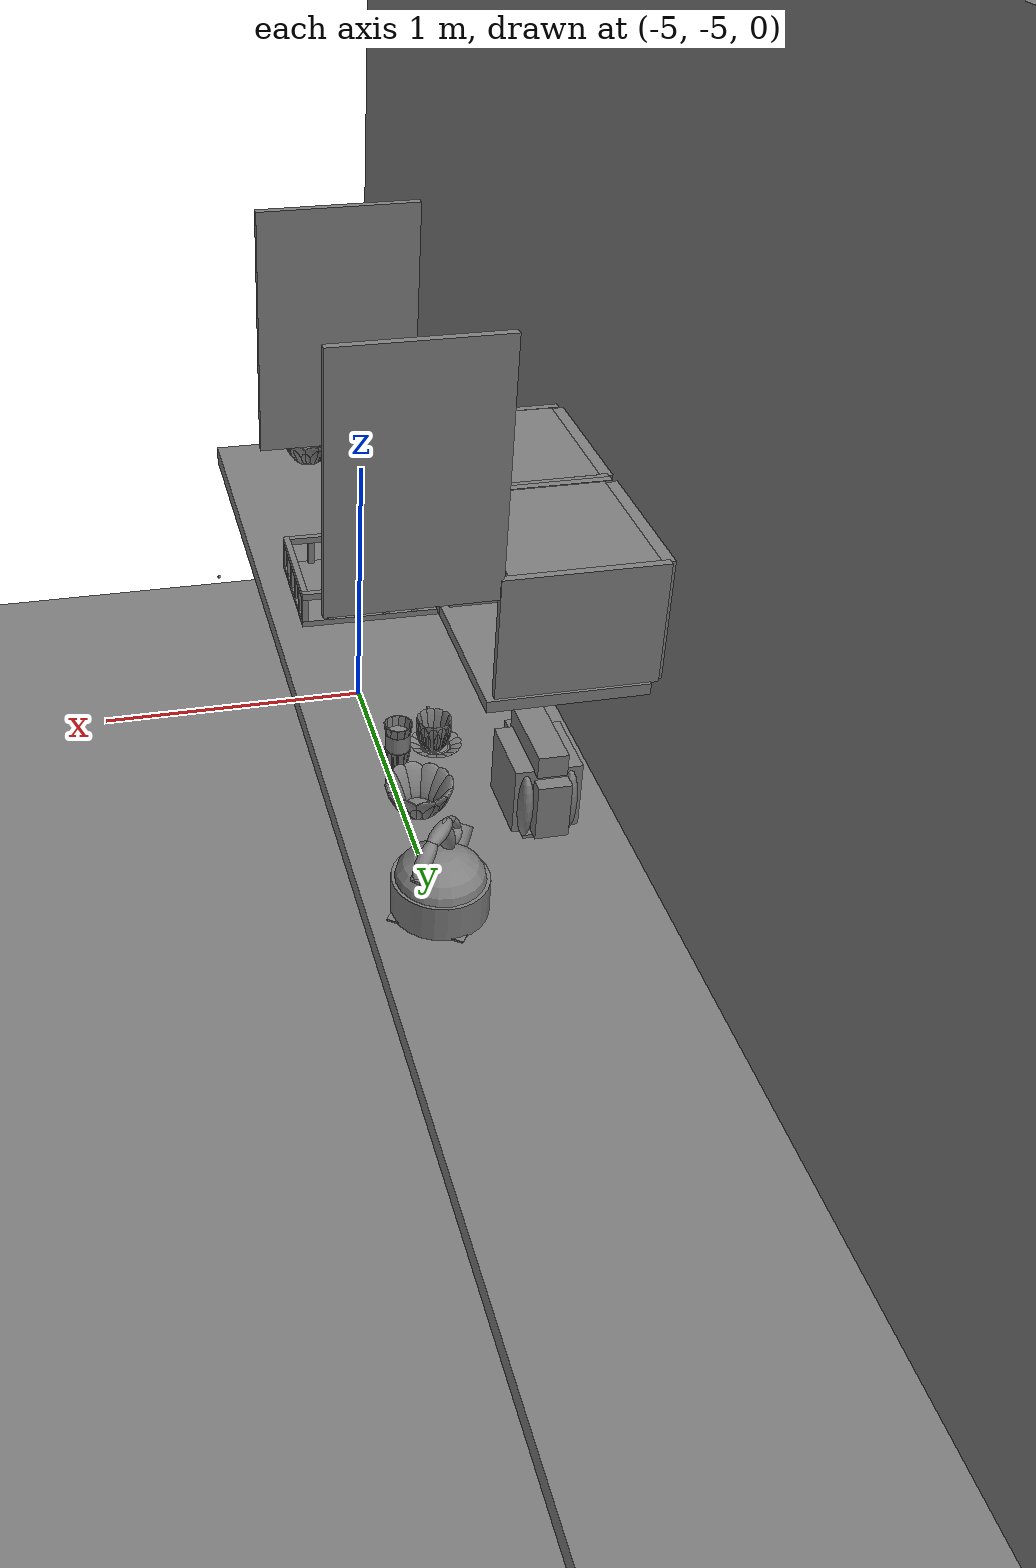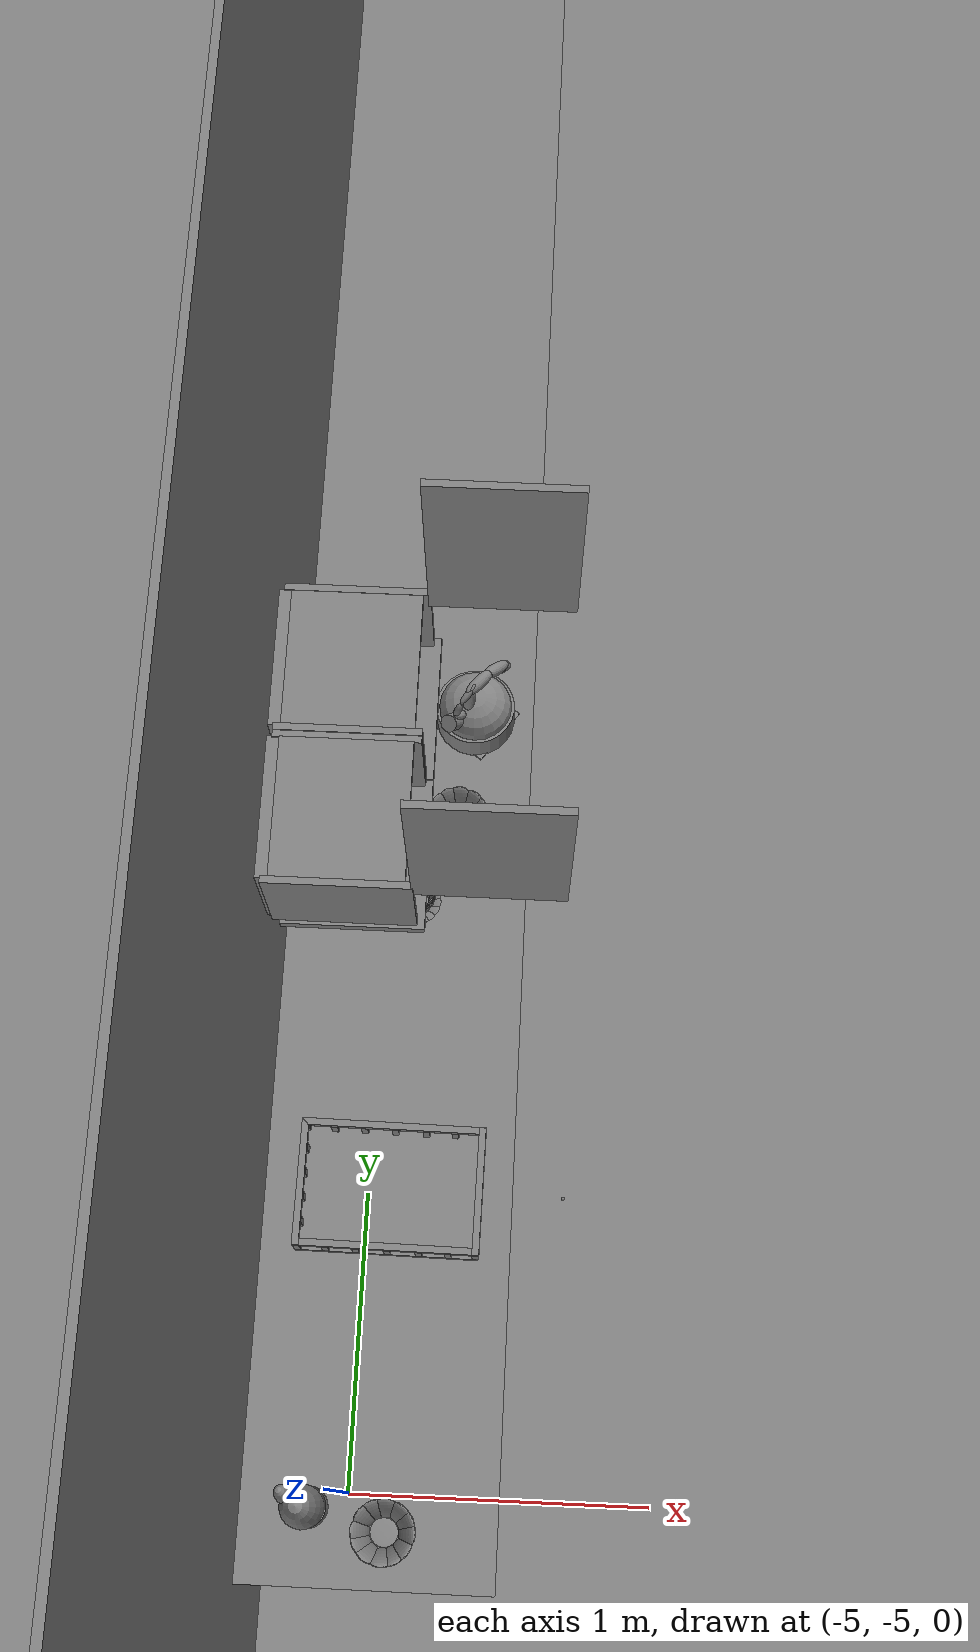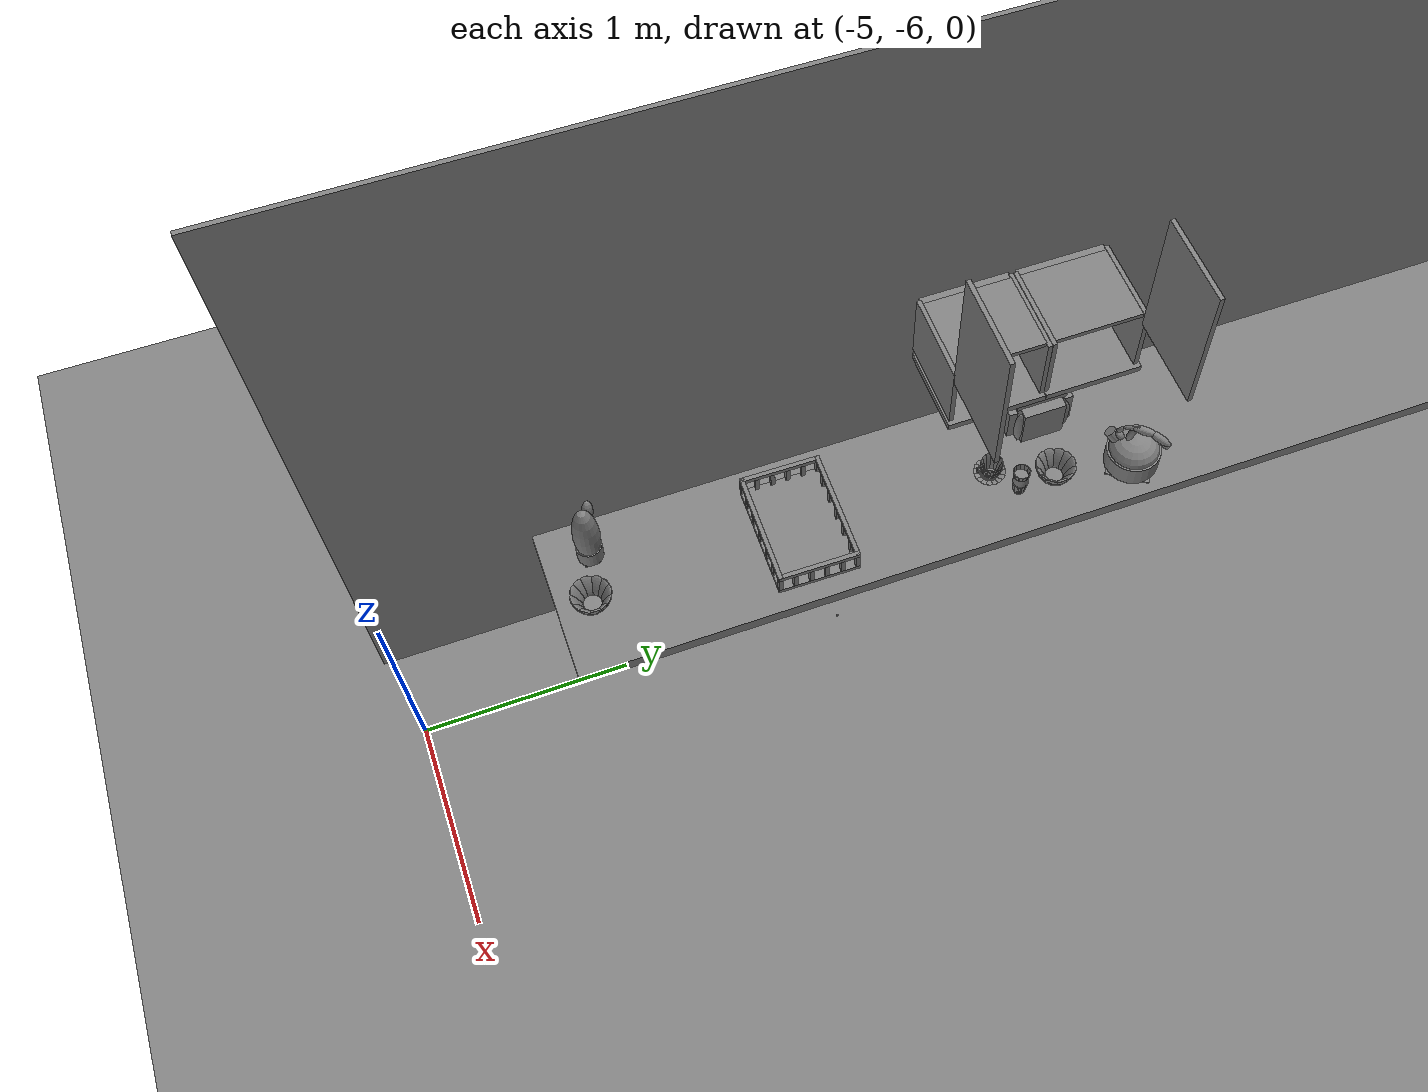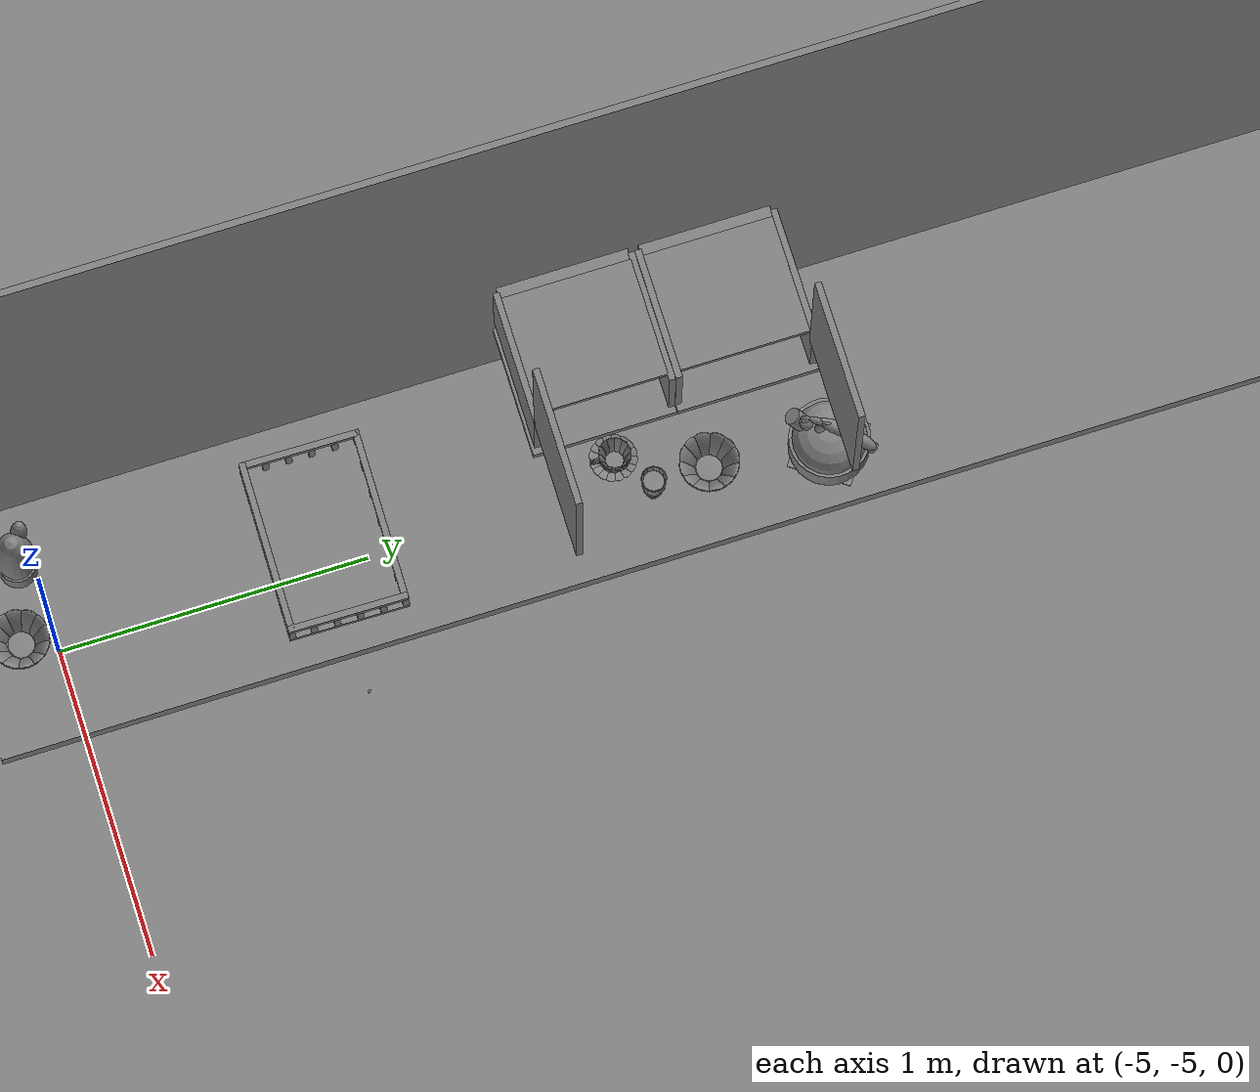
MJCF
<mujoco>
    <option gravity="0.000000000 0.000000000 -9.810000420" timestep="0.0049999999" integrator="implicitfast" density="9.8000002" viscosity="1.8000001e-05" noslip_iterations="10" iterations="100" sdf_iterations="50">
        <flag multiccd="disable"/>
    </option>
    <size memory="1000M"/>
    <compiler coordinate="local"/>
    <worldbody>
        <light cutoff="30" pos="0 1 1" dir="0 -1 -2"/>
        <light cutoff="30" pos="0 -1 1" dir="0 1 -2"/>
        <body pos="0.000000000 0.000000000 0.000000000" euler="0.000000000 0.000000000 0.000000000" name="Static Objcets_Static Objcets">
            <geom contype="1" conaffinity="1" density="1000" type="box" material="" rgba="0.500000000 0.500000000 0.500000000 1.000000000" solimp="0.899999976 0.949999988 0.001000000" friction="1.000000000 0.005000000 0.000100000" solref="0.020000000 1.000000000" margin="0" condim="3" group="0" pos="-5.189302921 -3.293644905 1.760152459" quat="0.707107067 0.707106471 0.000000000 0.000000000" size="0.025000000 0.159999996 0.200000003" name="Static Objcets_geom_A54B7916_A272_475A_9568_F497E96ADE62"/>
            <geom contype="1" conaffinity="1" density="1000" type="box" material="" rgba="0.500000000 0.500000000 0.500000000 1.000000000" solimp="0.899999976 0.949999988 0.001000000" friction="1.000000000 0.005000000 0.000100000" solref="0.020000000 1.000000000" margin="0" condim="3" group="0" pos="-4.999745846 -3.497932911 1.764780521" quat="0.707107067 0.707106471 0.000000000 0.000000000" size="0.200000003 0.159999996 0.010000000" name="Static Objcets_geom_3EB330BB_8139_4B88_838C_464873CB5BF0"/>
            <geom contype="1" conaffinity="1" density="1000" type="box" material="" rgba="0.500000000 0.500000000 0.500000000 1.000000000" solimp="0.899999976 0.949999988 0.001000000" friction="1.000000000 0.005000000 0.000100000" solref="0.020000000 1.000000000" margin="0" condim="3" group="0" pos="-4.979488373 -3.297635794 1.591412544" quat="0.707106829 0.707106709 0.000000000 0.000000000" size="0.200000003 0.015000000 0.219999999" name="Static Objcets_geom_AE1C7EA9_C478_4D06_A125_34CD56ADD675"/>
            <geom contype="1" conaffinity="1" density="1000" type="box" material="" rgba="0.500000000 0.500000000 0.500000000 1.000000000" solimp="0.899999976 0.949999988 0.001000000" friction="1.000000000 0.005000000 0.000100000" solref="0.020000000 1.000000000" margin="0" condim="3" group="0" pos="-4.999745846 -3.087441683 1.763863802" quat="0.707107067 0.707106471 0.000000000 0.000000000" size="0.200000003 0.159999996 0.010000000" name="Static Objcets_geom_0D1A0B3A_1BD4_4897_BDEB_2CCE57B0B32E"/>
            <geom contype="1" conaffinity="1" density="1000" type="box" material="" rgba="0.500000000 0.500000000 0.500000000 1.000000000" solimp="0.899999976 0.949999988 0.001000000" friction="1.000000000 0.005000000 0.000100000" solref="0.020000000 1.000000000" margin="0" condim="3" group="0" pos="-5.000125408 -3.294431210 1.913951039" quat="0.707107067 0.707106471 0.000000000 0.000000000" size="0.180000007 0.010000000 0.200000003" name="Static Objcets_geom_9B594264_A0B8_49C2_8157_DAB5680F7ABB"/>
            <geom contype="1" conaffinity="1" density="1000" type="box" material="" rgba="0.500000000 0.500000000 0.500000000 1.000000000" solimp="0.899999976 0.949999988 0.001000000" friction="1.000000000 0.005000000 0.000100000" solref="0.020000000 1.000000000" margin="0" condim="3" group="0" pos="-4.873187065 -2.461376429 0.977675021" quat="0.707107067 0.707106471 0.000000000 0.000000000" size="0.370000005 0.029999999 2.799999952" name="Static Objcets_geom_FC9BB7FC_9522_4035_B7C8_9D87EC3FAA2D"/>
            <geom contype="1" conaffinity="1" density="1000" type="box" material="" rgba="0.500000000 0.500000000 0.500000000 1.000000000" solimp="0.899999976 0.949999988 0.001000000" friction="1.000000000 0.005000000 0.000100000" solref="0.020000000 1.000000000" margin="0" condim="3" group="0" pos="-5.244853973 -2.375543594 1.820221663" quat="0.707107008 0.707106531 0.000000000 0.000000000" size="0.010000000 1.500000000 3.700000048" name="Static Objcets_geom_1E2C15DE_EDEA_41D1_B494_38443EB5445A"/>
            <geom contype="1" conaffinity="1" density="1000" type="box" material="" rgba="0.500000000 0.500000000 0.500000000 1.000000000" solimp="0.899999976 0.949999988 0.001000000" friction="1.000000000 0.005000000 0.000100000" solref="0.020000000 1.000000000" margin="0" condim="3" group="0" pos="-0.720102787 0.222944975 -1.102830648" quat="0.000000954 1.000000000 0.000000000 0.000000000" size="8.000000000 8.000000000 0.010000000" name="Static Objcets_geom_BB0AA1E5_1444_4F4E_B238_3F179797E22F"/>
            <geom contype="1" conaffinity="1" density="1000" type="box" material="" rgba="0.500000000 0.500000000 0.500000000 1.000000000" solimp="0.899999976 0.949999988 0.001000000" friction="1.000000000 0.005000000 0.000100000" solref="0.020000000 1.000000000" margin="0" condim="3" group="0" pos="-4.999745846 -2.653569937 1.764779806" quat="0.707107067 0.707106471 0.000000000 0.000000000" size="0.200000003 0.159999996 0.010000000" name="Static Objcets_geom_4B0AB05D_2913_4EA4_AC26_BEA6BBD8E76B"/>
            <geom contype="1" conaffinity="1" density="1000" type="box" material="" rgba="0.500000000 0.500000000 0.500000000 1.000000000" solimp="0.899999976 0.949999988 0.001000000" friction="1.000000000 0.005000000 0.000100000" solref="0.020000000 1.000000000" margin="0" condim="3" group="0" pos="-5.000125408 -2.861802340 1.913950682" quat="0.707107067 0.707106471 0.000000000 0.000000000" size="0.180000007 0.010000000 0.200000003" name="Static Objcets_geom_07C63BD7_ED53_44E8_97AC_E2D2C03AED17"/>
            <geom contype="1" conaffinity="1" density="1000" type="box" material="" rgba="0.500000000 0.500000000 0.500000000 1.000000000" solimp="0.899999976 0.949999988 0.001000000" friction="1.000000000 0.005000000 0.000100000" solref="0.020000000 1.000000000" margin="0" condim="3" group="0" pos="-5.189302921 -2.861564636 1.760152102" quat="0.707107067 0.707106471 0.000000000 0.000000000" size="0.025000000 0.159999996 0.200000003" name="Static Objcets_geom_CA028915_95E1_4C60_88A8_BE26AD64CFA4"/>
            <geom contype="1" conaffinity="1" density="1000" type="box" material="" rgba="0.500000000 0.500000000 0.500000000 1.000000000" solimp="0.899999976 0.949999988 0.001000000" friction="1.000000000 0.005000000 0.000100000" solref="0.020000000 1.000000000" margin="0" condim="3" group="0" pos="-4.979488373 -2.855390549 1.591412187" quat="0.707106709 0.707106769 0.000000000 0.000000000" size="0.200000003 0.015000000 0.219999999" name="Static Objcets_geom_75DAA159_E68C_4EA8_BF6C_9E65F9CDFAF3"/>
            <geom contype="1" conaffinity="1" density="1000" type="box" material="" rgba="0.500000000 0.500000000 0.500000000 1.000000000" solimp="0.899999976 0.949999988 0.001000000" friction="1.000000000 0.005000000 0.000100000" solref="0.020000000 1.000000000" margin="0" condim="3" group="0" pos="-4.999745846 -3.066934109 1.765979409" quat="0.707107067 0.707106471 0.000000000 0.000000000" size="0.200000003 0.159999996 0.010000000" name="Static Objcets_geom_520E4A93_189C_4B01_990C_2C81F125F810"/>
        </body>
        <body pos="1000.000000000 1000.000000000 1.000000000" euler="0.000000000 0.000000000 0.000000000" name="openloong_gripper_2f85_fix_base_usda_jar_01">
            <geom contype="1" conaffinity="1" density="1000" type="box" material="" rgba="0.500000000 0.500000000 0.500000000 1.000000000" solimp="0.899999976 0.949999988 0.001000000" friction="1.000000000 0.005000000 0.000100000" solref="0.020000000 1.000000000" margin="0" condim="3" group="0" pos="0.000000000 0.000000000 0.006158113" quat="1.000000000 0.000000000 0.000000000 0.000000000" size="0.020000000 0.020000000 0.005000000" name="openloong_gripper_2f85_fix_base_usda_geom_E14F5E32_6DC7_4679_9751_BC80ECCB41FB"/>
            <geom contype="1" conaffinity="1" density="1000" type="cylinder" material="" rgba="0.500000000 0.500000000 0.500000000 1.000000000" solimp="0.899999976 0.949999988 0.001000000" friction="1.000000000 0.005000000 0.000100000" solref="0.020000000 1.000000000" margin="0" condim="3" group="0" pos="0.000000000 0.000000000 0.062744498" quat="1.000000000 0.000000000 0.000000000 0.000000000" size="0.041000001 0.052999999 1.000000000" name="openloong_gripper_2f85_fix_base_usda_geom_01168BEB_EBD6_4C58_9993_3AD231952393"/>
            <geom contype="1" conaffinity="1" density="1000" type="ellipsoid" material="" rgba="0.500000000 0.500000000 0.500000000 1.000000000" solimp="0.899999976 0.949999988 0.001000000" friction="1.000000000 0.005000000 0.000100000" solref="0.020000000 1.000000000" margin="0" condim="3" group="0" pos="0.000000000 0.000000000 0.122252703" quat="1.000000000 0.000000000 0.000000000 0.000000000" size="0.035999998 0.035999998 0.010000000" name="openloong_gripper_2f85_fix_base_usda_geom_C8054C1C_585D_4077_AED5_6D96832E9CD0"/>
            <geom contype="1" conaffinity="1" density="1000" type="cylinder" material="" rgba="0.500000000 0.500000000 0.500000000 1.000000000" solimp="0.899999976 0.949999988 0.001000000" friction="1.000000000 0.005000000 0.000100000" solref="0.020000000 1.000000000" margin="0" condim="3" group="0" pos="0.000000000 0.000000000 0.015747190" quat="1.000000000 0.000000000 0.000000000 0.000000000" size="0.035000000 0.010000000 1.000000000" name="openloong_gripper_2f85_fix_base_usda_geom_1D7B69B0_5E0D_465B_8EB5_18D9155DCCE0"/>
            <geom contype="1" conaffinity="1" density="1000" type="ellipsoid" material="" rgba="0.500000000 0.500000000 0.500000000 1.000000000" solimp="0.899999976 0.949999988 0.001000000" friction="1.000000000 0.005000000 0.000100000" solref="0.020000000 1.000000000" margin="0" condim="3" group="0" pos="0.000000000 0.000000000 0.115815401" quat="1.000000000 0.000000000 0.000000000 0.000000000" size="0.039999999 0.039999999 0.010000000" name="openloong_gripper_2f85_fix_base_usda_geom_445FA758_6EC5_42D0_B3BB_91CED7349756"/>
            <geom contype="1" conaffinity="1" density="1000" type="cylinder" material="" rgba="0.500000000 0.500000000 0.500000000 1.000000000" solimp="0.899999976 0.949999988 0.001000000" friction="1.000000000 0.005000000 0.000100000" solref="0.020000000 1.000000000" margin="0" condim="3" group="0" pos="0.000000000 0.000000000 0.133183479" quat="1.000000000 0.000000000 0.000000000 0.000000000" size="0.037999999 0.006500000 1.000000000" name="openloong_gripper_2f85_fix_base_usda_geom_EBB05067_3469_4751_BEDF_25E06DB0AA6F"/>
            <freejoint name="openloong_gripper_2f85_fix_base_usda_jar_01_joint"/>
            <site size="0.005000000 0.005000000 0.005000000" rgba="0.500000000 0.500000000 0.500000000 1.000000000" pos="0.000000000 0.000000000 0.000000000" quat="1.000000000 0.000000000 0.000000000 0.000000000" group="0" type="sphere" name="openloong_gripper_2f85_fix_base_usda_jar_01site"/>
        </body>
        <body pos="1000.000000000 1000.000000000 1.000000000" euler="0.000000000 0.000000000 0.000000000" name="openloong_gripper_2f85_fix_base_usda_bow_yellow_kps">
            <geom contype="1" conaffinity="1" density="1000" type="ellipsoid" material="" rgba="0.500000000 0.500000000 0.500000000 1.000000000" solimp="0.899999976 0.949999988 0.001000000" friction="1.000000000 0.005000000 0.000100000" solref="0.020000000 1.000000000" margin="0" condim="3" group="0" pos="-0.052185059 0.040283203 0.044118762" quat="0.919264615 -0.076883033 -0.225593656 -0.313287765" size="0.010000000 0.039999999 0.052000001" name="openloong_gripper_2f85_fix_base_usda_geom_05C12F0A_51EB_48EA_A180_E21C0A5C219A"/>
            <geom contype="1" conaffinity="1" density="1000" type="ellipsoid" material="" rgba="0.500000000 0.500000000 0.500000000 1.000000000" solimp="0.899999976 0.949999988 0.001000000" friction="1.000000000 0.005000000 0.000100000" solref="0.020000000 1.000000000" margin="0" condim="3" group="0" pos="-0.000061035 0.065979004 0.044118762" quat="0.687598765 -0.168314874 -0.168741167 -0.685860336" size="0.010000000 0.039999999 0.052000001" name="openloong_gripper_2f85_fix_base_usda_geom_526381A0_8992_4545_B133_3667BE4BB6EC"/>
            <geom contype="1" conaffinity="1" density="1000" type="box" material="" rgba="0.500000000 0.500000000 0.500000000 1.000000000" solimp="0.899999976 0.949999988 0.001000000" friction="1.000000000 0.005000000 0.000100000" solref="0.020000000 1.000000000" margin="0" condim="3" group="0" pos="0.000061035 0.000000000 -0.002001643" quat="1.000000000 0.000000000 0.000000000 0.000000000" size="0.029999999 0.029999999 0.002000000" name="openloong_gripper_2f85_fix_base_usda_geom_4B36DCD6_1081_41F8_8B5F_C35CFE114FDF"/>
            <geom contype="1" conaffinity="1" density="1000" type="ellipsoid" material="" rgba="0.500000000 0.500000000 0.500000000 1.000000000" solimp="0.899999976 0.949999988 0.001000000" friction="1.000000000 0.005000000 0.000100000" solref="0.020000000 1.000000000" margin="0" condim="3" group="0" pos="0.029418945 -0.059082031 0.044118762" quat="0.825555861 0.125530601 0.202597082 -0.511521280" size="0.010000000 0.039999999 0.052000001" name="openloong_gripper_2f85_fix_base_usda_geom_97EA4422_FDBB_493B_9041_029EA4E7990F"/>
            <geom contype="1" conaffinity="1" density="1000" type="ellipsoid" material="" rgba="0.500000000 0.500000000 0.500000000 1.000000000" solimp="0.899999976 0.949999988 0.001000000" friction="1.000000000 0.005000000 0.000100000" solref="0.020000000 1.000000000" margin="0" condim="3" group="0" pos="0.000244141 -0.065979004 0.044118762" quat="0.687598765 0.168314651 0.168741375 -0.685860336" size="0.010000000 0.039999999 0.052000001" name="openloong_gripper_2f85_fix_base_usda_geom_DCEF3E2C_C645_4B82_A856_3DC26BEB38F9"/>
            <geom contype="1" conaffinity="1" density="1000" type="ellipsoid" material="" rgba="0.500000000 0.500000000 0.500000000 1.000000000" solimp="0.899999976 0.949999988 0.001000000" friction="1.000000000 0.005000000 0.000100000" solref="0.020000000 1.000000000" margin="0" condim="3" group="0" pos="0.000061035 0.000000000 0.000446677" quat="1.000000000 0.000000000 0.000000000 0.000000000" size="0.039999999 0.039999999 0.002000000" name="openloong_gripper_2f85_fix_base_usda_geom_A759C5C5_F087_484C_BF68_121A2FE9FD18"/>
            <geom contype="1" conaffinity="1" density="1000" type="ellipsoid" material="" rgba="0.500000000 0.500000000 0.500000000 1.000000000" solimp="0.899999976 0.949999988 0.001000000" friction="1.000000000 0.005000000 0.000100000" solref="0.020000000 1.000000000" margin="0" condim="3" group="0" pos="0.059082031 0.029541016 0.044118762" quat="0.223252773 -0.231952220 -0.054787423 -0.945174456" size="0.010000000 0.039999999 0.052000001" name="openloong_gripper_2f85_fix_base_usda_geom_87389982_B088_47FE_BED2_B436C35E86BD"/>
            <geom contype="1" conaffinity="1" density="1000" type="ellipsoid" material="" rgba="0.500000000 0.500000000 0.500000000 1.000000000" solimp="0.899999976 0.949999988 0.001000000" friction="1.000000000 0.005000000 0.000100000" solref="0.020000000 1.000000000" margin="0" condim="3" group="0" pos="0.000061035 0.000000000 0.007335305" quat="1.000000000 0.000000000 0.000000000 0.000000000" size="0.039999999 0.039999999 0.002000000" name="openloong_gripper_2f85_fix_base_usda_geom_92771B81_91F0_4C20_9551_2C585B8A8613"/>
            <geom contype="1" conaffinity="1" density="1000" type="ellipsoid" material="" rgba="0.500000000 0.500000000 0.500000000 1.000000000" solimp="0.899999976 0.949999988 0.001000000" friction="1.000000000 0.005000000 0.000100000" solref="0.020000000 1.000000000" margin="0" condim="3" group="0" pos="-0.029296875 0.059082031 0.044118762" quat="0.825555861 -0.125530809 -0.202596918 -0.511521280" size="0.010000000 0.039999999 0.052000001" name="openloong_gripper_2f85_fix_base_usda_geom_7DB01D38_2BE6_4301_A413_82CCAE5BBB60"/>
            <geom contype="1" conaffinity="1" density="1000" type="ellipsoid" material="" rgba="0.500000000 0.500000000 0.500000000 1.000000000" solimp="0.899999976 0.949999988 0.001000000" friction="1.000000000 0.005000000 0.000100000" solref="0.020000000 1.000000000" margin="0" condim="3" group="0" pos="0.040222168 0.052368164 0.044118762" quat="0.429593176 -0.213750049 -0.105424821 -0.871002972" size="0.010000000 0.039999999 0.052000001" name="openloong_gripper_2f85_fix_base_usda_geom_9CCB5960_C935_4FD0_96EA_7CA3C7F21BF2"/>
            <geom contype="1" conaffinity="1" density="1000" type="ellipsoid" material="" rgba="0.500000000 0.500000000 0.500000000 1.000000000" solimp="0.899999976 0.949999988 0.001000000" friction="1.000000000 0.005000000 0.000100000" solref="0.020000000 1.000000000" margin="0" condim="3" group="0" pos="0.066040039 0.000000000 0.044118762" quat="0.971183062 -0.000000156 0.238334835 0.000000030" size="0.010000000 0.039999999 0.052000001" name="openloong_gripper_2f85_fix_base_usda_geom_C5EBF7A6_4C13_4798_905D_FDA992E3B646"/>
            <geom contype="1" conaffinity="1" density="1000" type="ellipsoid" material="" rgba="0.500000000 0.500000000 0.500000000 1.000000000" solimp="0.899999976 0.949999988 0.001000000" friction="1.000000000 0.005000000 0.000100000" solref="0.020000000 1.000000000" margin="0" condim="3" group="0" pos="0.052307129 -0.040283203 0.044118762" quat="0.919264674 0.076882750 0.225593731 -0.313287705" size="0.010000000 0.039999999 0.052000001" name="openloong_gripper_2f85_fix_base_usda_geom_DB9EF2C4_5B52_4215_B599_CBDD1FCFDE7F"/>
            <geom contype="1" conaffinity="1" density="1000" type="ellipsoid" material="" rgba="0.500000000 0.500000000 0.500000000 1.000000000" solimp="0.899999976 0.949999988 0.001000000" friction="1.000000000 0.005000000 0.000100000" solref="0.020000000 1.000000000" margin="0" condim="3" group="0" pos="-0.065917969 0.000000000 0.044118762" quat="0.971183062 -0.000000142 -0.238334835 0.000000030" size="0.010000000 0.039999999 0.052000001" name="openloong_gripper_2f85_fix_base_usda_geom_32784CB5_5CF0_42C3_A9AE_8DF43EC19A32"/>
            <geom contype="1" conaffinity="1" density="1000" type="ellipsoid" material="" rgba="0.500000000 0.500000000 0.500000000 1.000000000" solimp="0.899999976 0.949999988 0.001000000" friction="1.000000000 0.005000000 0.000100000" solref="0.020000000 1.000000000" margin="0" condim="3" group="0" pos="-0.058898926 -0.029541016 0.044118762" quat="0.223252758 0.231952101 0.054787733 -0.945174575" size="0.010000000 0.039999999 0.052000001" name="openloong_gripper_2f85_fix_base_usda_geom_D83CEF51_AB03_48D3_8E5E_80C2D5516BAC"/>
            <geom contype="1" conaffinity="1" density="1000" type="ellipsoid" material="" rgba="0.500000000 0.500000000 0.500000000 1.000000000" solimp="0.899999976 0.949999988 0.001000000" friction="1.000000000 0.005000000 0.000100000" solref="0.020000000 1.000000000" margin="0" condim="3" group="0" pos="-0.040100098 -0.052368164 0.044118762" quat="0.429593235 0.213749886 0.105425082 -0.871003032" size="0.010000000 0.039999999 0.052000001" name="openloong_gripper_2f85_fix_base_usda_geom_0992BDB8_589E_4F3C_8AE6_B834652B18AA"/>
            <freejoint name="openloong_gripper_2f85_fix_base_usda_bow_yellow_kps_joint"/>
            <site size="0.005000000 0.005000000 0.005000000" rgba="0.500000000 0.500000000 0.500000000 1.000000000" pos="0.000000000 0.000000000 0.000000000" quat="0.999961913 0.008726534 0.000000000 0.000000000" group="0" type="sphere" name="openloong_gripper_2f85_fix_base_usda_bow_yellow_kps"/>
        </body>
        <body pos="-3.939419270 -3.705270529 1.873453379" euler="121.296028137 -32.489299774 143.656799316" mocap="true" name="spotlight3_SpotLight"/>
        <body pos="-4.008253574 -4.594954014 1.895772338" euler="-89.216766357 61.236316681 22.811485291" mocap="true" name="spotlight1_SpotLight"/>
        <body pos="-4.269662857 -3.981222391 1.830739260" euler="-27.286203384 -50.640724182 86.215232849" mocap="true" name="spotlight6_SpotLight"/>
        <body pos="1000.000000000 1000.000000000 1.000000000" euler="0.000000000 0.000000000 0.000000000" name="openloong_gripper_2f85_fix_base_usda_salt">
            <geom contype="1" conaffinity="1" density="1000" type="box" material="" rgba="0.500000000 0.500000000 0.500000000 1.000000000" solimp="0.899999976 0.949999988 0.001000000" friction="1.000000000 0.005000000 0.000100000" solref="0.020000000 1.000000000" margin="0" condim="3" group="0" pos="0.000305176 0.000000000 0.084862232" quat="1.000000000 0.000000000 0.000000000 0.000000000" size="0.048999999 0.018999999 0.005000000" name="openloong_gripper_2f85_fix_base_usda_geom_82CA095C_8772_447B_8187_9DCDDF36DCEC"/>
            <geom contype="1" conaffinity="1" density="1000" type="box" material="" rgba="0.500000000 0.500000000 0.500000000 1.000000000" solimp="0.899999976 0.949999988 0.001000000" friction="1.000000000 0.005000000 0.000100000" solref="0.020000000 1.000000000" margin="0" condim="3" group="0" pos="0.000305176 0.000000000 0.104564309" quat="1.000000000 0.000000000 0.000000000 0.000000000" size="0.052000001 0.014000000 0.005000000" name="openloong_gripper_2f85_fix_base_usda_geom_64EA2044_5B33_423C_988F_5FEB1ECF8503"/>
            <geom contype="1" conaffinity="1" density="1000" type="box" material="" rgba="0.500000000 0.500000000 0.500000000 1.000000000" solimp="0.899999976 0.949999988 0.001000000" friction="1.000000000 0.005000000 0.000100000" solref="0.020000000 1.000000000" margin="0" condim="3" group="0" pos="0.000305176 0.000000000 0.114487171" quat="1.000000000 0.000000000 0.000000000 0.000000000" size="0.054000001 0.011500000 0.005000000" name="openloong_gripper_2f85_fix_base_usda_geom_66734945_8AC0_46BD_B4DE_1B42460B1118"/>
            <geom contype="1" conaffinity="1" density="1000" type="box" material="" rgba="0.500000000 0.500000000 0.500000000 1.000000000" solimp="0.899999976 0.949999988 0.001000000" friction="1.000000000 0.005000000 0.000100000" solref="0.020000000 1.000000000" margin="0" condim="3" group="0" pos="0.000305176 0.000000000 0.075103164" quat="1.000000000 0.000000000 0.000000000 0.000000000" size="0.048000000 0.020000000 0.005000000" name="openloong_gripper_2f85_fix_base_usda_geom_29E1D122_9456_4DD1_93E8_3A4CFA9D1F03"/>
            <geom contype="1" conaffinity="1" density="1000" type="box" material="" rgba="0.500000000 0.500000000 0.500000000 1.000000000" solimp="0.899999976 0.949999988 0.001000000" friction="1.000000000 0.005000000 0.000100000" solref="0.020000000 1.000000000" margin="0" condim="3" group="0" pos="0.000305176 0.000000000 0.134892464" quat="1.000000000 0.000000000 0.000000000 0.000000000" size="0.057000000 0.007000000 0.005000000" name="openloong_gripper_2f85_fix_base_usda_geom_A1792BBD_9FCD_4506_8E07_4E18FA9F135A"/>
            <geom contype="1" conaffinity="1" density="1000" type="box" material="" rgba="0.500000000 0.500000000 0.500000000 1.000000000" solimp="0.899999976 0.949999988 0.001000000" friction="1.000000000 0.005000000 0.000100000" solref="0.020000000 1.000000000" margin="0" condim="3" group="0" pos="0.000305176 0.000000000 0.094920278" quat="1.000000000 0.000000000 0.000000000 0.000000000" size="0.050000001 0.017000001 0.005000000" name="openloong_gripper_2f85_fix_base_usda_geom_3AEA1C55_0CDA_4EBF_9977_7F20B6457A0E"/>
            <geom contype="1" conaffinity="1" density="1000" type="box" material="" rgba="0.500000000 0.500000000 0.500000000 1.000000000" solimp="0.899999976 0.949999988 0.001000000" friction="1.000000000 0.005000000 0.000100000" solref="0.020000000 1.000000000" margin="0" condim="3" group="0" pos="0.000305176 0.000000000 0.065204859" quat="1.000000000 0.000000000 0.000000000 0.000000000" size="0.045000002 0.021000000 0.005000000" name="openloong_gripper_2f85_fix_base_usda_geom_E4FAA9DA_E7F4_4DB8_A5B1_DD93CA33C2B4"/>
            <geom contype="1" conaffinity="1" density="1000" type="box" material="" rgba="0.500000000 0.500000000 0.500000000 1.000000000" solimp="0.899999976 0.949999988 0.001000000" friction="1.000000000 0.005000000 0.000100000" solref="0.020000000 1.000000000" margin="0" condim="3" group="0" pos="0.000305176 0.000000000 0.144135714" quat="1.000000000 0.000000000 0.000000000 0.000000000" size="0.059000000 0.005000000 0.004000000" name="openloong_gripper_2f85_fix_base_usda_geom_3420BF28_1032_4660_80B6_01F537C56CC6"/>
            <geom contype="1" conaffinity="1" density="1000" type="box" material="" rgba="0.500000000 0.500000000 0.500000000 1.000000000" solimp="0.899999976 0.949999988 0.001000000" friction="1.000000000 0.005000000 0.000100000" solref="0.020000000 1.000000000" margin="0" condim="3" group="0" pos="0.000000000 0.000000000 0.031593561" quat="1.000000000 0.000000000 0.000000000 0.000000000" size="0.041999999 0.024000000 0.029999999" name="openloong_gripper_2f85_fix_base_usda_geom_132DD5F2_6B4C_4B6F_A8A4_497339F37AB9"/>
            <geom contype="1" conaffinity="1" density="1000" type="box" material="" rgba="0.500000000 0.500000000 0.500000000 1.000000000" solimp="0.899999976 0.949999988 0.001000000" friction="1.000000000 0.005000000 0.000100000" solref="0.020000000 1.000000000" margin="0" condim="3" group="0" pos="0.000305176 0.000000000 0.124608755" quat="1.000000000 0.000000000 0.000000000 0.000000000" size="0.055000000 0.008000000 0.005000000" name="openloong_gripper_2f85_fix_base_usda_geom_C5B1CCD6_8198_4541_8018_7AA2B9399389"/>
            <freejoint name="openloong_gripper_2f85_fix_base_usda_salt_joint"/>
            <site size="0.005000000 0.005000000 0.005000000" rgba="0.500000000 0.500000000 0.500000000 1.000000000" pos="0.000000000 0.000000000 0.000000000" quat="1.000000000 0.000000000 0.000000000 0.000000000" group="0" type="sphere" name="openloong_gripper_2f85_fix_base_usda_saltsite"/>
        </body>
        <body pos="1000.000000000 1000.000000000 1.000000000" euler="0.000000000 0.000000000 0.000000000" name="openloong_gripper_2f85_fix_base_usda_coffeecup_white_kps">
            <geom contype="1" conaffinity="1" density="1000" type="capsule" material="" rgba="0.500000000 0.500000000 0.500000000 1.000000000" solimp="0.899999976 0.949999988 0.001000000" friction="1.000000000 0.005000000 0.000100000" solref="0.020000000 1.000000000" margin="0" condim="3" group="0" pos="-0.000854492 -0.065795898 0.050029993" quat="0.343559504 -0.613204718 0.626912475 0.336047262" size="0.004000000 0.005000000 1.000000000" name="openloong_gripper_2f85_fix_base_usda_geom_9A74446C_D941_41B1_9600_7693FD62F3AA"/>
            <geom contype="1" conaffinity="1" density="1000" type="ellipsoid" material="" rgba="0.500000000 0.500000000 0.500000000 1.000000000" solimp="0.899999976 0.949999988 0.001000000" friction="1.000000000 0.005000000 0.000100000" solref="0.020000000 1.000000000" margin="0" condim="3" group="0" pos="-0.000793457 -0.038452148 0.048040152" quat="0.711656272 0.066323131 -0.067805752 0.696095467" size="0.005000000 0.029999999 0.048999999" name="openloong_gripper_2f85_fix_base_usda_geom_9642BBE0_B18D_418B_ABAB_7C0119A52CFD"/>
            <geom contype="1" conaffinity="1" density="1000" type="ellipsoid" material="" rgba="0.500000000 0.500000000 0.500000000 1.000000000" solimp="0.899999976 0.949999988 0.001000000" friction="1.000000000 0.005000000 0.000100000" solref="0.020000000 1.000000000" margin="0" condim="3" group="0" pos="0.037719727 -0.001892090 0.048040152" quat="0.995387912 0.001371633 0.094835162 -0.014391154" size="0.005000000 0.029999999 0.048999999" name="openloong_gripper_2f85_fix_base_usda_geom_E3177075_45A3_48E6_A20D_811A43A13C09"/>
            <geom contype="1" conaffinity="1" density="1000" type="ellipsoid" material="" rgba="0.500000000 0.500000000 0.500000000 1.000000000" solimp="0.899999976 0.949999988 0.001000000" friction="1.000000000 0.005000000 0.000100000" solref="0.020000000 1.000000000" margin="0" condim="3" group="0" pos="0.033996582 0.015502930 0.048040152" quat="0.970659733 -0.021051638 0.092478797 0.220962167" size="0.005000000 0.029999999 0.048999999" name="openloong_gripper_2f85_fix_base_usda_geom_2673D3E6_C590_48EA_9D86_BEA3C416178B"/>
            <geom contype="1" conaffinity="1" density="1000" type="box" material="" rgba="0.500000000 0.500000000 0.500000000 1.000000000" solimp="0.899999976 0.949999988 0.001000000" friction="1.000000000 0.005000000 0.000100000" solref="0.020000000 1.000000000" margin="0" condim="3" group="0" pos="0.000793457 -0.000183105 0.000156164" quat="0.714879215 0.000000000 0.000000000 0.699247897" size="0.020000000 0.020000000 0.002000000" name="openloong_gripper_2f85_fix_base_usda_geom_28BD51EB_67D9_4844_88E3_49E61131D446"/>
            <geom contype="1" conaffinity="1" density="1000" type="ellipsoid" material="" rgba="0.500000000 0.500000000 0.500000000 1.000000000" solimp="0.899999976 0.949999988 0.001000000" friction="1.000000000 0.005000000 0.000100000" solref="0.020000000 1.000000000" margin="0" condim="3" group="0" pos="-0.019409180 -0.033081055 0.048040152" quat="0.866879702 0.046630561 -0.082595348 0.489411235" size="0.005000000 0.029999999 0.048999999" name="openloong_gripper_2f85_fix_base_usda_geom_134E88F4_63A0_475B_81ED_9DCDC327EE32"/>
            <geom contype="1" conaffinity="1" density="1000" type="ellipsoid" material="" rgba="0.500000000 0.500000000 0.500000000 1.000000000" solimp="0.899999976 0.949999988 0.001000000" friction="1.000000000 0.005000000 0.000100000" solref="0.020000000 1.000000000" margin="0" condim="3" group="0" pos="-0.016052246 0.033264160 0.048040152" quat="0.840792537 -0.050782297 -0.080109790 -0.532983541" size="0.005000000 0.029999999 0.048999999" name="openloong_gripper_2f85_fix_base_usda_geom_F1BA142B_C480_4372_AE3C_C919AAE3307D"/>
            <geom contype="1" conaffinity="1" density="1000" type="capsule" material="" rgba="0.500000000 0.500000000 0.500000000 1.000000000" solimp="0.899999976 0.949999988 0.001000000" friction="1.000000000 0.005000000 0.000100000" solref="0.020000000 1.000000000" margin="0" condim="3" group="0" pos="-0.000549316 -0.053527832 0.046825886" quat="0.505496025 -0.494442940 0.505495846 0.494442940" size="0.004000000 0.005000000 1.000000000" name="openloong_gripper_2f85_fix_base_usda_geom_B6B79D2C_5384_428C_992D_5EB349991ED6"/>
            <geom contype="1" conaffinity="1" density="1000" type="ellipsoid" material="" rgba="0.500000000 0.500000000 0.500000000 1.000000000" solimp="0.899999976 0.949999988 0.001000000" friction="1.000000000 0.005000000 0.000100000" solref="0.020000000 1.000000000" margin="0" condim="3" group="0" pos="-0.032104492 0.018920898 0.048040152" quat="0.958129764 -0.025742561 -0.091288343 -0.270168930" size="0.005000000 0.029999999 0.048999999" name="openloong_gripper_2f85_fix_base_usda_geom_2236531F_7A32_4BA8_8DB5_767E98E30601"/>
            <geom contype="1" conaffinity="1" density="1000" type="ellipsoid" material="" rgba="0.500000000 0.500000000 0.500000000 1.000000000" solimp="0.899999976 0.949999988 0.001000000" friction="1.000000000 0.005000000 0.000100000" solref="0.020000000 1.000000000" margin="0" condim="3" group="0" pos="-0.037597656 0.000305176 0.048040152" quat="0.995387554 -0.001371440 -0.094839431 -0.014389008" size="0.005000000 0.029999999 0.048999999" name="openloong_gripper_2f85_fix_base_usda_geom_6EB6AF7E_A196_4836_B94A_55B85CC5F94F"/>
            <geom contype="1" conaffinity="1" density="1000" type="capsule" material="" rgba="0.500000000 0.500000000 0.500000000 1.000000000" solimp="0.899999976 0.949999988 0.001000000" friction="1.000000000 0.005000000 0.000100000" solref="0.020000000 1.000000000" margin="0" condim="3" group="0" pos="-0.000366211 -0.043762207 0.044118762" quat="0.260488123 -0.651174724 0.665731549 0.254792154" size="0.004000000 0.003000000 1.000000000" name="openloong_gripper_2f85_fix_base_usda_geom_B51F4E3B_3F23_4BB5_B8E9_208CE8A7426D"/>
            <geom contype="1" conaffinity="1" density="1000" type="capsule" material="" rgba="0.500000000 0.500000000 0.500000000 1.000000000" solimp="0.899999976 0.949999988 0.001000000" friction="1.000000000 0.005000000 0.000100000" solref="0.020000000 1.000000000" margin="0" condim="3" group="0" pos="-0.000915527 -0.068542480 0.082936406" quat="0.624995589 -0.339446366 0.347034454 0.611329615" size="0.004000000 0.004000000 1.000000000" name="openloong_gripper_2f85_fix_base_usda_geom_B1F1648F_8012_4D35_BF83_A682D7B4D1B4"/>
            <geom contype="1" conaffinity="1" density="1000" type="ellipsoid" material="" rgba="0.500000000 0.500000000 0.500000000 1.000000000" solimp="0.899999976 0.949999988 0.001000000" friction="1.000000000 0.005000000 0.000100000" solref="0.020000000 1.000000000" margin="0" condim="3" group="0" pos="0.016113281 -0.034851074 0.048040152" quat="0.840793252 0.050779939 0.080106191 -0.532983422" size="0.005000000 0.029999999 0.048999999" name="openloong_gripper_2f85_fix_base_usda_geom_16F499D1_C2F1_40AB_B5C4_698CD0D40C94"/>
            <geom contype="1" conaffinity="1" density="1000" type="ellipsoid" material="" rgba="0.500000000 0.500000000 0.500000000 1.000000000" solimp="0.899999976 0.949999988 0.001000000" friction="1.000000000 0.005000000 0.000100000" solref="0.020000000 1.000000000" margin="0" condim="3" group="0" pos="0.000854492 0.036865234 0.048040152" quat="0.711656570 -0.066320375 0.067802906 0.696095705" size="0.005000000 0.029999999 0.048999999" name="openloong_gripper_2f85_fix_base_usda_geom_9EE1CE56_FD0D_4D53_961B_8EA304C41200"/>
            <geom contype="1" conaffinity="1" density="1000" type="ellipsoid" material="" rgba="0.500000000 0.500000000 0.500000000 1.000000000" solimp="0.899999976 0.949999988 0.001000000" friction="1.000000000 0.005000000 0.000100000" solref="0.020000000 1.000000000" margin="0" condim="3" group="0" pos="-0.033935547 -0.017089844 0.048040152" quat="0.970659137 0.021052625 -0.092483103 0.220962465" size="0.005000000 0.029999999 0.048999999" name="openloong_gripper_2f85_fix_base_usda_geom_8F8CEB44_657A_43C8_AD1F_86729D0C703F"/>
            <geom contype="1" conaffinity="1" density="1000" type="ellipsoid" material="" rgba="0.500000000 0.500000000 0.500000000 1.000000000" solimp="0.899999976 0.949999988 0.001000000" friction="1.000000000 0.005000000 0.000100000" solref="0.020000000 1.000000000" margin="0" condim="3" group="0" pos="0.019531250 0.031494141 0.048040152" quat="0.866880119 -0.046628602 0.082591817 0.489411235" size="0.005000000 0.029999999 0.048999999" name="openloong_gripper_2f85_fix_base_usda_geom_12E3C283_F9BC_4F66_9B61_054B11E83C8D"/>
            <geom contype="1" conaffinity="1" density="1000" type="ellipsoid" material="" rgba="0.500000000 0.500000000 0.500000000 1.000000000" solimp="0.899999976 0.949999988 0.001000000" friction="1.000000000 0.005000000 0.000100000" solref="0.020000000 1.000000000" margin="0" condim="3" group="0" pos="0.032165527 -0.020507812 0.048040152" quat="0.958128154 0.025740955 0.091285400 -0.270175666" size="0.005000000 0.029999999 0.048999999" name="openloong_gripper_2f85_fix_base_usda_geom_1935B572_6C21_4635_93C0_C568CA409F3A"/>
            <geom contype="1" conaffinity="1" density="1000" type="capsule" material="" rgba="0.500000000 0.500000000 0.500000000 1.000000000" solimp="0.899999976 0.949999988 0.001000000" friction="1.000000000 0.005000000 0.000100000" solref="0.020000000 1.000000000" margin="0" condim="3" group="0" pos="-0.000610352 -0.056823730 0.083572865" quat="0.452654332 -0.541215360 0.553313971 0.442756712" size="0.004000000 0.009000000 1.000000000" name="openloong_gripper_2f85_fix_base_usda_geom_74E7418D_FACA_47F2_A591_2B9AFB330CF7"/>
            <geom contype="1" conaffinity="1" density="1000" type="ellipsoid" material="" rgba="0.500000000 0.500000000 0.500000000 1.000000000" solimp="0.899999976 0.949999988 0.001000000" friction="1.000000000 0.005000000 0.000100000" solref="0.020000000 1.000000000" margin="0" condim="3" group="0" pos="0.000061035 -0.000183105 0.001848221" quat="0.714879215 0.000000000 0.000000000 0.699247897" size="0.029999999 0.029999999 0.001000000" name="openloong_gripper_2f85_fix_base_usda_geom_97953044_2E81_4475_A094_C1D6D9B371EE"/>
            <geom contype="1" conaffinity="1" density="1000" type="capsule" material="" rgba="0.500000000 0.500000000 0.500000000 1.000000000" solimp="0.899999976 0.949999988 0.001000000" friction="1.000000000 0.005000000 0.000100000" solref="0.020000000 1.000000000" margin="0" condim="3" group="0" pos="-0.000976562 -0.071838379 0.066101432" quat="0.031849027 -0.698553741 0.714169443 0.031152546" size="0.004000000 0.012000000 1.000000000" name="openloong_gripper_2f85_fix_base_usda_geom_54769A9B_FFC3_4DFC_9623_2AD086B3794F"/>
            <freejoint name="openloong_gripper_2f85_fix_base_usda_coffeecup_white_kps_joint"/>
            <site size="0.005000000 0.005000000 0.005000000" rgba="0.500000000 0.500000000 0.500000000 1.000000000" pos="0.000000000 0.000000000 0.000000000" quat="0.999961913 0.008726534 0.000000000 0.000000000" group="0" type="sphere" name="openloong_gripper_2f85_fix_base_usda_coffeecup_white_kps"/>
        </body>
        <body pos="1000.000000000 1000.000000000 1.000000000" euler="0.000000000 0.000000000 0.000000000" name="openloong_gripper_2f85_fix_base_usda_bottle_red">
            <geom contype="1" conaffinity="1" density="1000" type="ellipsoid" material="" rgba="0.500000000 0.500000000 0.500000000 1.000000000" solimp="0.899999976 0.949999988 0.001000000" friction="1.000000000 0.005000000 0.000100000" solref="0.020000000 1.000000000" margin="0" condim="3" group="0" pos="0.000000000 0.000000000 0.144284487" quat="1.000000000 0.000000000 0.000000000 0.000000000" size="0.021000000 0.021000000 0.079999998" name="openloong_gripper_2f85_fix_base_usda_geom_A0E390C8_A438_41A9_A15D_BEEAD5094D7E"/>
            <geom contype="1" conaffinity="1" density="1000" type="cylinder" material="" rgba="0.500000000 0.500000000 0.500000000 1.000000000" solimp="0.899999976 0.949999988 0.001000000" friction="1.000000000 0.005000000 0.000100000" solref="0.020000000 1.000000000" margin="0" condim="3" group="0" pos="0.000000000 0.000000000 0.220618963" quat="1.000000000 0.000000000 0.000000000 0.000000000" size="0.016000001 0.010000000 1.000000000" name="openloong_gripper_2f85_fix_base_usda_geom_9D76D4BB_7210_4AAC_88AC_E6A02BF12FF3"/>
            <geom contype="1" conaffinity="1" density="1000" type="ellipsoid" material="" rgba="0.500000000 0.500000000 0.500000000 1.000000000" solimp="0.899999976 0.949999988 0.001000000" friction="1.000000000 0.005000000 0.000100000" solref="0.020000000 1.000000000" margin="0" condim="3" group="0" pos="0.000000000 0.000000000 0.118945479" quat="1.000000000 0.000000000 0.000000000 0.000000000" size="0.030999999 0.030999999 0.029999999" name="openloong_gripper_2f85_fix_base_usda_geom_33353614_0EC3_4C88_964F_58A527CDA146"/>
            <geom contype="1" conaffinity="1" density="1000" type="box" material="" rgba="0.500000000 0.500000000 0.500000000 1.000000000" solimp="0.899999976 0.949999988 0.001000000" friction="1.000000000 0.005000000 0.000100000" solref="0.020000000 1.000000000" margin="0" condim="3" group="0" pos="0.000000000 0.000000000 0.002189159" quat="1.000000000 0.000000000 0.000000000 0.000000000" size="0.020000000 0.020000000 0.003000000" name="openloong_gripper_2f85_fix_base_usda_geom_ED17BFCB_F0C9_40C3_AE86_01E2D521658A"/>
            <geom contype="1" conaffinity="1" density="1000" type="cylinder" material="" rgba="0.500000000 0.500000000 0.500000000 1.000000000" solimp="0.899999976 0.949999988 0.001000000" friction="1.000000000 0.005000000 0.000100000" solref="0.020000000 1.000000000" margin="0" condim="3" group="0" pos="0.000000000 -0.000366211 0.060884237" quat="1.000000000 0.000000000 0.000000000 0.000000000" size="0.030999999 0.057999998 1.000000000" name="openloong_gripper_2f85_fix_base_usda_geom_8AC68FA4_8250_4881_8098_8F4F8A33F46F"/>
            <freejoint name="openloong_gripper_2f85_fix_base_usda_bottle_red_joint"/>
            <site size="0.005000000 0.005000000 0.005000000" rgba="0.500000000 0.500000000 0.500000000 1.000000000" pos="0.000000000 0.000000000 0.000000000" quat="0.999961913 0.008726535 0.000000000 0.000000000" group="0" type="sphere" name="openloong_gripper_2f85_fix_base_usda_bottle_redsite"/>
        </body>
        <body pos="-4.860558510 -4.149443150 1.004824519" euler="0.000000000 0.000000000 -90.691101074" name="openloong_gripper_2f85_fix_base_usda_Basket_Kitchen_01">
            <geom contype="1" conaffinity="1" density="1000" type="box" material="" rgba="0.500000000 0.500000000 0.500000000 1.000000000" solimp="0.899999976 0.949999988 0.001000000" friction="1.000000000 0.005000000 0.000100000" solref="0.020000000 1.000000000" margin="0" condim="3" group="0" pos="-0.175679624 -0.000001907 0.109079957" quat="0.707106948 0.000000000 0.000000000 0.707106292" size="0.268999994 0.010000000 0.010500000" name="openloong_gripper_2f85_fix_base_usda_geom_397E45EF_9113_4DDE_A249_E66A1D395897"/>
            <geom contype="1" conaffinity="1" density="1000" type="box" material="" rgba="0.500000000 0.500000000 0.500000000 1.000000000" solimp="0.899999976 0.949999988 0.001000000" friction="1.000000000 0.005000000 0.000100000" solref="0.020000000 1.000000000" margin="0" condim="3" group="0" pos="-0.176020086 0.002991676 0.059861541" quat="0.707106948 0.000000000 0.000000000 0.707106292" size="0.009500000 0.009500000 0.039999999" name="openloong_gripper_2f85_fix_base_usda_geom_99FB6AAD_1BD9_4766_9C15_8508A88AC5F9"/>
            <geom contype="1" conaffinity="1" density="1000" type="box" material="" rgba="0.500000000 0.500000000 0.500000000 1.000000000" solimp="0.899999976 0.949999988 0.001000000" friction="1.000000000 0.005000000 0.000100000" solref="0.020000000 1.000000000" margin="0" condim="3" group="0" pos="0.176000476 0.002991199 0.059860587" quat="0.707106948 0.000000000 0.000000000 0.707106292" size="0.009500000 0.009500000 0.039999999" name="openloong_gripper_2f85_fix_base_usda_geom_68F726FB_AAC6_4D81_B0D1_833108B0816E"/>
            <geom contype="1" conaffinity="1" density="1000" type="box" material="" rgba="0.500000000 0.500000000 0.500000000 1.000000000" solimp="0.899999976 0.949999988 0.001000000" friction="1.000000000 0.005000000 0.000100000" solref="0.020000000 1.000000000" margin="0" condim="3" group="0" pos="0.176003337 0.259475470 0.059859991" quat="0.707106948 0.000000000 0.000000000 0.707106292" size="0.009500000 0.009500000 0.039999999" name="openloong_gripper_2f85_fix_base_usda_geom_D0AB7B97_8BEF_46EC_94F4_B2D4C6BDE000"/>
            <geom contype="1" conaffinity="1" density="1000" type="box" material="" rgba="0.500000000 0.500000000 0.500000000 1.000000000" solimp="0.899999976 0.949999988 0.001000000" friction="1.000000000 0.005000000 0.000100000" solref="0.020000000 1.000000000" margin="0" condim="3" group="0" pos="-0.176020086 -0.088696003 0.059861422" quat="0.707106948 0.000000000 0.000000000 0.707106292" size="0.009500000 0.009500000 0.039999999" name="openloong_gripper_2f85_fix_base_usda_geom_BFAE48C4_A372_40C1_A183_A51260F5170D"/>
            <geom contype="1" conaffinity="1" density="1000" type="box" material="" rgba="0.500000000 0.500000000 0.500000000 1.000000000" solimp="0.899999976 0.949999988 0.001000000" friction="1.000000000 0.005000000 0.000100000" solref="0.020000000 1.000000000" margin="0" condim="3" group="0" pos="0.000000000 0.259647608 0.109079957" quat="0.707106948 0.000000000 0.000000000 0.707106292" size="0.010000000 0.185000002 0.010500000" name="openloong_gripper_2f85_fix_base_usda_geom_5AE485B3_B9F3_45CE_A01D_CE04C0DB25FD"/>
            <geom contype="1" conaffinity="1" density="1000" type="box" material="" rgba="0.500000000 0.500000000 0.500000000 1.000000000" solimp="0.899999976 0.949999988 0.001000000" friction="1.000000000 0.005000000 0.000100000" solref="0.020000000 1.000000000" margin="0" condim="3" group="0" pos="0.176001906 -0.259545803 0.059860349" quat="0.707106948 0.000000000 0.000000000 0.707106292" size="0.009500000 0.009500000 0.039999999" name="openloong_gripper_2f85_fix_base_usda_geom_8C5383D4_4679_4E90_BF90_4C76F0A465A7"/>
            <geom contype="1" conaffinity="1" density="1000" type="box" material="" rgba="0.500000000 0.500000000 0.500000000 1.000000000" solimp="0.899999976 0.949999988 0.001000000" friction="1.000000000 0.005000000 0.000100000" solref="0.020000000 1.000000000" margin="0" condim="3" group="0" pos="0.036305428 -0.259545326 0.059860587" quat="0.707106948 0.000000000 0.000000000 0.707106292" size="0.009500000 0.009500000 0.039999999" name="openloong_gripper_2f85_fix_base_usda_geom_E5D90EF9_914C_419A_AC9A_C9B93DDEAAA9"/>
            <geom contype="1" conaffinity="1" density="1000" type="box" material="" rgba="0.500000000 0.500000000 0.500000000 1.000000000" solimp="0.899999976 0.949999988 0.001000000" friction="1.000000000 0.005000000 0.000100000" solref="0.020000000 1.000000000" margin="0" condim="3" group="0" pos="0.000000119 -0.259647369 0.109079957" quat="0.707106948 0.000000000 0.000000000 0.707106292" size="0.010000000 0.185000002 0.010500000" name="openloong_gripper_2f85_fix_base_usda_geom_FB5060C5_3245_410B_9392_8A24BBD3DD42"/>
            <geom contype="1" conaffinity="1" density="1000" type="box" material="" rgba="0.500000000 0.500000000 0.500000000 1.000000000" solimp="0.899999976 0.949999988 0.001000000" friction="1.000000000 0.005000000 0.000100000" solref="0.020000000 1.000000000" margin="0" condim="3" group="0" pos="-0.034950614 -0.259546280 0.059860826" quat="0.707106948 0.000000000 0.000000000 0.707106292" size="0.009500000 0.009500000 0.039999999" name="openloong_gripper_2f85_fix_base_usda_geom_80239EB1_5B03_4C9F_AF2B_68FDA927690D"/>
            <geom contype="1" conaffinity="1" density="1000" type="box" material="" rgba="0.500000000 0.500000000 0.500000000 1.000000000" solimp="0.899999976 0.949999988 0.001000000" friction="1.000000000 0.005000000 0.000100000" solref="0.020000000 1.000000000" margin="0" condim="3" group="0" pos="0.108178139 0.259475708 0.059860229" quat="0.707106948 0.000000000 0.000000000 0.707106292" size="0.009500000 0.009500000 0.039999999" name="openloong_gripper_2f85_fix_base_usda_geom_29FE8349_2A42_4470_84C7_01BE721B800E"/>
            <geom contype="1" conaffinity="1" density="1000" type="box" material="" rgba="0.500000000 0.500000000 0.500000000 1.000000000" solimp="0.899999976 0.949999988 0.001000000" friction="1.000000000 0.005000000 0.000100000" solref="0.020000000 1.000000000" margin="0" condim="3" group="0" pos="-0.106845737 0.259474993 0.059860826" quat="0.707106948 0.000000000 0.000000000 0.707106292" size="0.009500000 0.009500000 0.039999999" name="openloong_gripper_2f85_fix_base_usda_geom_F8ECD122_4A97_4ADC_B3BB_6ADBA574A6B5"/>
            <geom contype="1" conaffinity="1" density="1000" type="box" material="" rgba="0.500000000 0.500000000 0.500000000 1.000000000" solimp="0.899999976 0.949999988 0.001000000" friction="1.000000000 0.005000000 0.000100000" solref="0.020000000 1.000000000" margin="0" condim="3" group="0" pos="-0.176020563 0.179505825 0.059861779" quat="0.707106948 0.000000000 0.000000000 0.707106292" size="0.009500000 0.009500000 0.039999999" name="openloong_gripper_2f85_fix_base_usda_geom_03EF490E_940E_43E9_A09F_0F444942F860"/>
            <geom contype="1" conaffinity="1" density="1000" type="box" material="" rgba="0.500000000 0.500000000 0.500000000 1.000000000" solimp="0.899999976 0.949999988 0.001000000" friction="1.000000000 0.005000000 0.000100000" solref="0.020000000 1.000000000" margin="0" condim="3" group="0" pos="-0.034949303 0.259475708 0.059860587" quat="0.707106948 0.000000000 0.000000000 0.707106292" size="0.009500000 0.009500000 0.039999999" name="openloong_gripper_2f85_fix_base_usda_geom_923B332F_55BC_451F_A716_821A806EEB1B"/>
            <geom contype="1" conaffinity="1" density="1000" type="box" material="" rgba="0.500000000 0.500000000 0.500000000 1.000000000" solimp="0.899999976 0.949999988 0.001000000" friction="1.000000000 0.005000000 0.000100000" solref="0.020000000 1.000000000" margin="0" condim="3" group="0" pos="0.175792098 -0.000002384 0.109079838" quat="0.707106948 0.000000000 0.000000000 0.707106292" size="0.268999994 0.010000000 0.010500000" name="openloong_gripper_2f85_fix_base_usda_geom_18F1A057_F156_44F5_8A90_578D670E185D"/>
            <geom contype="1" conaffinity="1" density="1000" type="box" material="" rgba="0.500000000 0.500000000 0.500000000 1.000000000" solimp="0.899999976 0.949999988 0.001000000" friction="1.000000000 0.005000000 0.000100000" solref="0.020000000 1.000000000" margin="0" condim="3" group="0" pos="-0.000015259 0.000000000 0.010667920" quat="0.707106948 0.000000000 0.000000000 0.707106292" size="0.268999994 0.186000004 0.010500000" name="openloong_gripper_2f85_fix_base_usda_geom_5AE05A2E_30D2_450E_A60A_B1F0114AADDE"/>
            <geom contype="1" conaffinity="1" density="1000" type="box" material="" rgba="0.500000000 0.500000000 0.500000000 1.000000000" solimp="0.899999976 0.949999988 0.001000000" friction="1.000000000 0.005000000 0.000100000" solref="0.020000000 1.000000000" margin="0" condim="3" group="0" pos="-0.176020026 0.094224930 0.059861660" quat="0.707106948 0.000000000 0.000000000 0.707106292" size="0.009500000 0.009500000 0.039999999" name="openloong_gripper_2f85_fix_base_usda_geom_8361D451_84BC_449E_A938_2484AA34F346"/>
            <geom contype="1" conaffinity="1" density="1000" type="box" material="" rgba="0.500000000 0.500000000 0.500000000 1.000000000" solimp="0.899999976 0.949999988 0.001000000" friction="1.000000000 0.005000000 0.000100000" solref="0.020000000 1.000000000" margin="0" condim="3" group="0" pos="0.108177185 -0.259545326 0.059860349" quat="0.707106948 0.000000000 0.000000000 0.707106292" size="0.009500000 0.009500000 0.039999999" name="openloong_gripper_2f85_fix_base_usda_geom_2B547751_0CA8_4D97_8B6F_E02F0C82664C"/>
            <geom contype="1" conaffinity="1" density="1000" type="box" material="" rgba="0.500000000 0.500000000 0.500000000 1.000000000" solimp="0.899999976 0.949999988 0.001000000" friction="1.000000000 0.005000000 0.000100000" solref="0.020000000 1.000000000" margin="0" condim="3" group="0" pos="-0.176020026 -0.177031994 0.059861183" quat="0.707106948 0.000000000 0.000000000 0.707106292" size="0.009500000 0.009500000 0.039999999" name="openloong_gripper_2f85_fix_base_usda_geom_8FE385A8_3081_42FF_A74D_38FDE71920C0"/>
            <geom contype="1" conaffinity="1" density="1000" type="box" material="" rgba="0.500000000 0.500000000 0.500000000 1.000000000" solimp="0.899999976 0.949999988 0.001000000" friction="1.000000000 0.005000000 0.000100000" solref="0.020000000 1.000000000" margin="0" condim="3" group="0" pos="-0.176020086 -0.259545803 0.059861183" quat="0.707106948 0.000000000 0.000000000 0.707106292" size="0.009500000 0.009500000 0.039999999" name="openloong_gripper_2f85_fix_base_usda_geom_FEB29DE7_DAD0_4AB2_B45C_E8DBBEBEAFC9"/>
            <geom contype="1" conaffinity="1" density="1000" type="box" material="" rgba="0.500000000 0.500000000 0.500000000 1.000000000" solimp="0.899999976 0.949999988 0.001000000" friction="1.000000000 0.005000000 0.000100000" solref="0.020000000 1.000000000" margin="0" condim="3" group="0" pos="-0.106846333 -0.259545803 0.059861064" quat="0.707106948 0.000000000 0.000000000 0.707106292" size="0.009500000 0.009500000 0.039999999" name="openloong_gripper_2f85_fix_base_usda_geom_38AC187B_4FBF_423C_9E6A_63376EEBDCCF"/>
            <geom contype="1" conaffinity="1" density="1000" type="box" material="" rgba="0.500000000 0.500000000 0.500000000 1.000000000" solimp="0.899999976 0.949999988 0.001000000" friction="1.000000000 0.005000000 0.000100000" solref="0.020000000 1.000000000" margin="0" condim="3" group="0" pos="0.176000595 0.094224453 0.059860826" quat="0.707106948 0.000000000 0.000000000 0.707106292" size="0.009500000 0.009500000 0.039999999" name="openloong_gripper_2f85_fix_base_usda_geom_79248AA8_3B97_4E2F_814A_762901473E60"/>
            <geom contype="1" conaffinity="1" density="1000" type="box" material="" rgba="0.500000000 0.500000000 0.500000000 1.000000000" solimp="0.899999976 0.949999988 0.001000000" friction="1.000000000 0.005000000 0.000100000" solref="0.020000000 1.000000000" margin="0" condim="3" group="0" pos="0.176001072 -0.088696480 0.059860587" quat="0.707106948 0.000000000 0.000000000 0.707106292" size="0.009500000 0.009500000 0.039999999" name="openloong_gripper_2f85_fix_base_usda_geom_2E6E4353_0AFA_4796_9090_E80F7EAE1ECB"/>
            <geom contype="1" conaffinity="1" density="1000" type="box" material="" rgba="0.500000000 0.500000000 0.500000000 1.000000000" solimp="0.899999976 0.949999988 0.001000000" friction="1.000000000 0.005000000 0.000100000" solref="0.020000000 1.000000000" margin="0" condim="3" group="0" pos="0.036306858 0.259475946 0.059860349" quat="0.707106948 0.000000000 0.000000000 0.707106292" size="0.009500000 0.009500000 0.039999999" name="openloong_gripper_2f85_fix_base_usda_geom_48E090C7_7BC5_4EAD_9D07_05ACA2D78877"/>
            <geom contype="1" conaffinity="1" density="1000" type="box" material="" rgba="0.500000000 0.500000000 0.500000000 1.000000000" solimp="0.899999976 0.949999988 0.001000000" friction="1.000000000 0.005000000 0.000100000" solref="0.020000000 1.000000000" margin="0" condim="3" group="0" pos="0.176001430 -0.177032471 0.059860349" quat="0.707106948 0.000000000 0.000000000 0.707106292" size="0.009500000 0.009500000 0.039999999" name="openloong_gripper_2f85_fix_base_usda_geom_08583D4A_7D94_4F65_BCFA_5752C9C0E037"/>
            <geom contype="1" conaffinity="1" density="1000" type="box" material="" rgba="0.500000000 0.500000000 0.500000000 1.000000000" solimp="0.899999976 0.949999988 0.001000000" friction="1.000000000 0.005000000 0.000100000" solref="0.020000000 1.000000000" margin="0" condim="3" group="0" pos="0.175999999 0.179504871 0.059860945" quat="0.707106948 0.000000000 0.000000000 0.707106292" size="0.009500000 0.009500000 0.039999999" name="openloong_gripper_2f85_fix_base_usda_geom_37011EFD_8978_4D6D_BA15_40A8AAE0491E"/>
            <geom contype="1" conaffinity="1" density="1000" type="box" material="" rgba="0.500000000 0.500000000 0.500000000 1.000000000" solimp="0.899999976 0.949999988 0.001000000" friction="1.000000000 0.005000000 0.000100000" solref="0.020000000 1.000000000" margin="0" condim="3" group="0" pos="-0.176020026 0.259474516 0.059860945" quat="0.707106948 0.000000000 0.000000000 0.707106292" size="0.009500000 0.009500000 0.039999999" name="openloong_gripper_2f85_fix_base_usda_geom_F57FD597_AC15_4A14_BCD1_3AE292275D52"/>
            <freejoint name="openloong_gripper_2f85_fix_base_usda_Basket_Kitchen_01_joint"/>
        </body>
        <body pos="-4.705342293 -3.169416904 1.103703976" euler="0.000000000 0.000000000 0.000000000" name="Interactive Objcets_cup_02">
            <geom contype="1" conaffinity="1" density="1000" type="box" material="" rgba="0.500000000 0.500000000 0.500000000 1.000000000" solimp="0.899999976 0.949999988 0.001000000" friction="1.000000000 0.005000000 0.000100000" solref="0.020000000 1.000000000" margin="0" condim="3" group="0" pos="0.022285938 0.016949892 -0.037281752" quat="0.893179297 -0.070051625 0.034732576 -0.442851186" size="0.010000000 0.001000000 0.035000000" name="Interactive Objcets_geom_5EFA38DC_8E3C_4A79_9FB3_B5089BDD49C2"/>
            <geom contype="1" conaffinity="1" density="1000" type="box" material="" rgba="0.500000000 0.500000000 0.500000000 1.000000000" solimp="0.899999976 0.949999988 0.001000000" friction="1.000000000 0.005000000 0.000100000" solref="0.020000000 1.000000000" margin="0" condim="3" group="0" pos="0.034549713 0.000000000 0.062637210" quat="0.704941988 -0.055288255 0.055288251 -0.704942048" size="0.010000000 0.001000000 0.015000000" name="Interactive Objcets_geom_2F867C63_0A2E_4870_AA41_079DD933A783"/>
            <geom contype="1" conaffinity="1" density="1000" type="box" material="" rgba="0.500000000 0.500000000 0.500000000 1.000000000" solimp="0.899999976 0.949999988 0.001000000" friction="1.000000000 0.005000000 0.000100000" solref="0.020000000 1.000000000" margin="0" condim="3" group="0" pos="0.029378891 -0.018181801 0.062637210" quat="0.870895982 0.068302706 0.038053915 0.485208035" size="0.010000000 0.001000000 0.015000000" name="Interactive Objcets_geom_A0A528C3_747C_4DEC_8AF8_134B6DDE4591"/>
            <geom contype="1" conaffinity="1" density="1000" type="box" material="" rgba="0.500000000 0.500000000 0.500000000 1.000000000" solimp="0.899999976 0.949999988 0.001000000" friction="1.000000000 0.005000000 0.000100000" solref="0.020000000 1.000000000" margin="0" condim="3" group="0" pos="0.000000000 -0.034549713 0.062637210" quat="0.996938646 0.078187965 0.000000000 0.000000000" size="0.010000000 0.001000000 0.015000000" name="Interactive Objcets_geom_F30C86A1_4199_401B_A4F1_994D319B44A6"/>
            <geom contype="1" conaffinity="1" density="1000" type="cylinder" material="" rgba="0.500000000 0.500000000 0.500000000 1.000000000" solimp="0.899999976 0.949999988 0.001000000" friction="1.000000000 0.005000000 0.000100000" solref="0.020000000 1.000000000" margin="0" condim="3" group="0" pos="0.000000000 0.000000000 0.022491097" quat="1.000000000 0.000000030 0.000000000 0.000000000" size="0.033000000 0.025000000 1.000000000" name="Interactive Objcets_geom_793F012D_5060_42C4_B8EA_CE0D80114487"/>
            <geom contype="1" conaffinity="1" density="1000" type="box" material="" rgba="0.500000000 0.500000000 0.500000000 1.000000000" solimp="0.899999976 0.949999988 0.001000000" friction="1.000000000 0.005000000 0.000100000" solref="0.020000000 1.000000000" margin="0" condim="3" group="0" pos="0.000000000 0.034549713 0.062637210" quat="0.996938646 -0.078187965 0.000000000 0.000000000" size="0.010000000 0.001000000 0.015000000" name="Interactive Objcets_geom_37F6B392_C37C_4A7B_98FC_64D9AEB99E6A"/>
            <geom contype="1" conaffinity="1" density="1000" type="box" material="" rgba="0.500000000 0.500000000 0.500000000 1.000000000" solimp="0.899999976 0.949999988 0.001000000" friction="1.000000000 0.005000000 0.000100000" solref="0.020000000 1.000000000" margin="0" condim="3" group="0" pos="0.011943817 0.025323629 -0.037281752" quat="0.972834349 -0.076298930 0.017089661 -0.217898533" size="0.010000000 0.001000000 0.035000000" name="Interactive Objcets_geom_778952A2_855E_45D2_A226_9B69C1D376BE"/>
            <geom contype="1" conaffinity="1" density="1000" type="box" material="" rgba="0.500000000 0.500000000 0.500000000 1.000000000" solimp="0.899999976 0.949999988 0.001000000" friction="1.000000000 0.005000000 0.000100000" solref="0.020000000 1.000000000" margin="0" condim="3" group="0" pos="0.025214195 -0.011892319 -0.037281752" quat="0.841975451 0.066034243 0.041866414 0.533820212" size="0.010000000 0.001000000 0.035000000" name="Interactive Objcets_geom_B6546EC9_B5F1_4FC4_8A1E_49358579163F"/>
            <geom contype="1" conaffinity="1" density="1000" type="box" material="" rgba="0.500000000 0.500000000 0.500000000 1.000000000" solimp="0.899999976 0.949999988 0.001000000" friction="1.000000000 0.005000000 0.000100000" solref="0.020000000 1.000000000" margin="0" condim="3" group="0" pos="-0.027999878 0.000000000 -0.037281752" quat="0.704941988 0.055288255 -0.055288251 -0.704942048" size="0.010000000 0.001000000 0.035000000" name="Interactive Objcets_geom_53D387AB_5B62_4364_85D7_3FCCE9CC6A1E"/>
            <geom contype="1" conaffinity="1" density="1000" type="box" material="" rgba="0.500000000 0.500000000 0.500000000 1.000000000" solimp="0.899999976 0.949999988 0.001000000" friction="1.000000000 0.005000000 0.000100000" solref="0.020000000 1.000000000" margin="0" condim="3" group="0" pos="0.017436981 -0.029826880 0.062637210" quat="0.962265730 0.075468659 0.020441191 0.260636479" size="0.010000000 0.001000000 0.015000000" name="Interactive Objcets_geom_80525E76_1A7A_429A_8ECF_8C24986DD135"/>
            <geom contype="1" conaffinity="1" density="1000" type="box" material="" rgba="0.500000000 0.500000000 0.500000000 1.000000000" solimp="0.899999976 0.949999988 0.001000000" friction="1.000000000 0.005000000 0.000100000" solref="0.020000000 1.000000000" margin="0" condim="3" group="0" pos="0.029827118 0.017437220 0.062637210" quat="0.864722252 -0.067819774 0.038910985 -0.496126890" size="0.010000000 0.001000000 0.015000000" name="Interactive Objcets_geom_8C580E76_6368_4695_9F11_70445E2F09F6"/>
            <geom contype="1" conaffinity="1" density="1000" type="box" material="" rgba="0.500000000 0.500000000 0.500000000 1.000000000" solimp="0.899999976 0.949999988 0.001000000" friction="1.000000000 0.005000000 0.000100000" solref="0.020000000 1.000000000" margin="0" condim="3" group="0" pos="0.000000000 0.027877331 -0.037281752" quat="0.996938646 -0.078187965 0.000000000 0.000000000" size="0.010000000 0.001000000 0.035000000" name="Interactive Objcets_geom_C9460ABB_8E99_426A_B8BB_A463868FD3C6"/>
            <geom contype="1" conaffinity="1" density="1000" type="box" material="" rgba="0.500000000 0.500000000 0.500000000 1.000000000" solimp="0.899999976 0.949999988 0.001000000" friction="1.000000000 0.005000000 0.000100000" solref="0.020000000 1.000000000" margin="0" condim="3" group="0" pos="-0.025214195 0.011891127 -0.037281752" quat="0.841975451 -0.066034243 -0.041866414 0.533820212" size="0.010000000 0.001000000 0.035000000" name="Interactive Objcets_geom_389BAF51_2506_4693_B093_B0293B815E69"/>
            <geom contype="1" conaffinity="1" density="1000" type="box" material="" rgba="0.500000000 0.500000000 0.500000000 1.000000000" solimp="0.899999976 0.949999988 0.001000000" friction="1.000000000 0.005000000 0.000100000" solref="0.020000000 1.000000000" margin="0" condim="3" group="0" pos="-0.022286415 -0.016949654 -0.037281752" quat="0.893179297 0.070051625 -0.034732576 -0.442851186" size="0.010000000 0.001000000 0.035000000" name="Interactive Objcets_geom_F12FF09A_05AC_4B99_ADEF_36606877D81C"/>
            <geom contype="1" conaffinity="1" density="1000" type="box" material="" rgba="0.500000000 0.500000000 0.500000000 1.000000000" solimp="0.899999976 0.949999988 0.001000000" friction="1.000000000 0.005000000 0.000100000" solref="0.020000000 1.000000000" margin="0" condim="3" group="0" pos="-0.016875744 0.022189617 -0.037281752" quat="0.944716334 -0.074092269 -0.024973858 0.318430305" size="0.010000000 0.001000000 0.035000000" name="Interactive Objcets_geom_56D10BF9_7483_4A24_A0D2_4083ADFCD0D4"/>
            <geom contype="1" conaffinity="1" density="1000" type="box" material="" rgba="0.500000000 0.500000000 0.500000000 1.000000000" solimp="0.899999976 0.949999988 0.001000000" friction="1.000000000 0.005000000 0.000100000" solref="0.020000000 1.000000000" margin="0" condim="3" group="0" pos="0.018182278 0.029379368 0.062637210" quat="0.958910167 -0.075206861 0.021389510 -0.272722572" size="0.010000000 0.001000000 0.015000000" name="Interactive Objcets_geom_5C4BFE60_A16C_4302_AC48_95914A1A8ED6"/>
            <geom contype="1" conaffinity="1" density="1000" type="box" material="" rgba="0.500000000 0.500000000 0.500000000 1.000000000" solimp="0.899999976 0.949999988 0.001000000" friction="1.000000000 0.005000000 0.000100000" solref="0.020000000 1.000000000" margin="0" condim="3" group="0" pos="0.000000000 0.000000000 -0.075536966" quat="1.000000000 0.000000000 0.000000000 0.000000000" size="0.015000000 0.015000000 0.002000000" name="Interactive Objcets_geom_9B116098_18C0_494F_B4B7_33A207CD11C9"/>
            <geom contype="1" conaffinity="1" density="1000" type="box" material="" rgba="0.500000000 0.500000000 0.500000000 1.000000000" solimp="0.899999976 0.949999988 0.001000000" friction="1.000000000 0.005000000 0.000100000" solref="0.020000000 1.000000000" margin="0" condim="3" group="0" pos="-0.018181324 -0.029377937 0.062637210" quat="0.958910167 0.075206861 -0.021389510 -0.272722572" size="0.010000000 0.001000000 0.015000000" name="Interactive Objcets_geom_F2BE98AE_DE77_4D1A_A1BA_BBAAD956AAEF"/>
            <geom contype="1" conaffinity="1" density="1000" type="box" material="" rgba="0.500000000 0.500000000 0.500000000 1.000000000" solimp="0.899999976 0.949999988 0.001000000" friction="1.000000000 0.005000000 0.000100000" solref="0.020000000 1.000000000" margin="0" condim="3" group="0" pos="0.027999878 0.000000000 -0.037281752" quat="0.704941988 -0.055288255 0.055288251 -0.704942048" size="0.010000000 0.001000000 0.035000000" name="Interactive Objcets_geom_5F4E6C60_50F1_4161_B17D_A978CC9D981C"/>
            <geom contype="1" conaffinity="1" density="1000" type="box" material="" rgba="0.500000000 0.500000000 0.500000000 1.000000000" solimp="0.899999976 0.949999988 0.001000000" friction="1.000000000 0.005000000 0.000100000" solref="0.020000000 1.000000000" margin="0" condim="3" group="0" pos="0.016875744 -0.022189379 -0.037281752" quat="0.944716334 0.074092269 0.024973858 0.318430305" size="0.010000000 0.001000000 0.035000000" name="Interactive Objcets_geom_513E4D6F_939F_46F3_9423_952CF76E5DE7"/>
            <geom contype="1" conaffinity="1" density="1000" type="box" material="" rgba="0.500000000 0.500000000 0.500000000 1.000000000" solimp="0.899999976 0.949999988 0.001000000" friction="1.000000000 0.005000000 0.000100000" solref="0.020000000 1.000000000" margin="0" condim="3" group="0" pos="-0.029377937 0.018182278 0.062637210" quat="0.870895982 -0.068302706 -0.038053915 0.485208035" size="0.010000000 0.001000000 0.015000000" name="Interactive Objcets_geom_39C6A4C1_31C4_4D7F_9907_A16AE195E09B"/>
            <geom contype="1" conaffinity="1" density="1000" type="box" material="" rgba="0.500000000 0.500000000 0.500000000 1.000000000" solimp="0.899999976 0.949999988 0.001000000" friction="1.000000000 0.005000000 0.000100000" solref="0.020000000 1.000000000" margin="0" condim="3" group="0" pos="-0.017436504 0.029826880 0.062637210" quat="0.962265730 -0.075468659 -0.020441191 0.260636479" size="0.010000000 0.001000000 0.015000000" name="Interactive Objcets_geom_75DCB893_99CA_41AA_B3FE_CE56046FB6F4"/>
            <geom contype="1" conaffinity="1" density="1000" type="box" material="" rgba="0.500000000 0.500000000 0.500000000 1.000000000" solimp="0.899999976 0.949999988 0.001000000" friction="1.000000000 0.005000000 0.000100000" solref="0.020000000 1.000000000" margin="0" condim="3" group="0" pos="-0.034549713 0.000000000 0.062637210" quat="0.704941988 0.055288255 -0.055288251 -0.704942048" size="0.010000000 0.001000000 0.015000000" name="Interactive Objcets_geom_AF60457A_5604_4BE2_B529_BBEA4E8ADFC5"/>
            <geom contype="1" conaffinity="1" density="1000" type="box" material="" rgba="0.500000000 0.500000000 0.500000000 1.000000000" solimp="0.899999976 0.949999988 0.001000000" friction="1.000000000 0.005000000 0.000100000" solref="0.020000000 1.000000000" margin="0" condim="3" group="0" pos="-0.029826641 -0.017436504 0.062637210" quat="0.864722252 0.067819774 -0.038910985 -0.496126890" size="0.010000000 0.001000000 0.015000000" name="Interactive Objcets_geom_C2920529_B735_4BE1_98BB_FFA35B005FEB"/>
            <geom contype="1" conaffinity="1" density="1000" type="box" material="" rgba="0.500000000 0.500000000 0.500000000 1.000000000" solimp="0.899999976 0.949999988 0.001000000" friction="1.000000000 0.005000000 0.000100000" solref="0.020000000 1.000000000" margin="0" condim="3" group="0" pos="0.000000000 -0.027877331 -0.037281752" quat="0.996938646 0.078187965 0.000000000 0.000000000" size="0.010000000 0.001000000 0.035000000" name="Interactive Objcets_geom_13B66D3B_761E_406C_843C_B2814095649E"/>
            <freejoint name="Interactive Objcets_cup_02"/>
        </body>
        <body pos="-5.046103477 -5.051773071 1.001502514" euler="0.000000000 0.000000000 0.000000000" name="Interactive Objcets_huapen">
            <geom contype="1" conaffinity="1" density="1000" type="ellipsoid" material="" rgba="0.500000000 0.500000000 0.500000000 1.000000000" solimp="0.899999976 0.949999988 0.001000000" friction="1.000000000 0.005000000 0.000100000" solref="0.020000000 1.000000000" margin="0" condim="3" group="0" pos="0.008062840 0.004346371 0.205056787" quat="1.000000000 0.000000000 0.000000000 0.000000000" size="0.059999999 0.059999999 0.180000007" name="Interactive Objcets_huapen_hua_4552CED1_DF79_4212_A486_1F5A0AF0A0CC"/>
            <geom contype="1" conaffinity="1" density="1000" type="ellipsoid" material="" rgba="0.500000000 0.500000000 0.500000000 1.000000000" solimp="0.899999976 0.949999988 0.001000000" friction="1.000000000 0.005000000 0.000100000" solref="0.020000000 1.000000000" margin="0" condim="3" group="0" pos="-0.029900074 0.033599377 0.321917295" quat="0.992658079 -0.083605267 -0.087364964 0.002748166" size="0.025000000 0.025000000 0.059999999" name="Interactive Objcets_huapen_hua_D8BE358B_8A5E_4A44_8CF1_BA174F88EF55"/>
            <geom contype="1" conaffinity="1" density="1000" type="box" material="" rgba="0.500000000 0.500000000 0.500000000 1.000000000" solimp="0.899999976 0.949999988 0.001000000" friction="1.000000000 0.005000000 0.000100000" solref="0.020000000 1.000000000" margin="0" condim="3" group="0" pos="0.008062840 0.003952503 0.020566106" quat="1.000000000 0.000000000 0.000000000 0.000000000" size="0.035000000 0.035000000 0.020000000" name="Interactive Objcets_huapen_hua_858A996E_3173_4D6E_8823_323EF6F2BC49"/>
            <geom contype="1" conaffinity="1" density="1000" type="cylinder" material="" rgba="0.500000000 0.500000000 0.500000000 1.000000000" solimp="0.899999976 0.949999988 0.001000000" friction="1.000000000 0.005000000 0.000100000" solref="0.020000000 1.000000000" margin="0" condim="3" group="0" pos="0.008062840 0.003952026 0.080107450" quat="1.000000000 0.000000000 0.000000000 0.000000000" size="0.057999998 0.039999999 1.000000000" name="Interactive Objcets_huapen_hua_903CD735_8B74_461E_9C9D_9DC515E120F9"/>
            <freejoint name="Interactive Objcets_huapen"/>
        </body>
        <body pos="-4.721817970 -2.990536690 1.027358174" euler="0.000000000 0.000000000 89.999946594" name="Interactive Objcets_bow_02">
            <geom contype="1" conaffinity="1" density="1000" type="ellipsoid" material="" rgba="0.500000000 0.500000000 0.500000000 1.000000000" solimp="0.899999976 0.949999988 0.001000000" friction="1.000000000 0.005000000 0.000100000" solref="0.020000000 1.000000000" margin="0" condim="3" group="0" pos="0.052321676 -0.040297508 0.044118762" quat="0.919264674 0.076882742 0.225593731 -0.313287675" size="0.010000000 0.039999999 0.052000001" name="Interactive Objcets_geom_399C4E22_88F1_484A_974D_DEE8D4A5D7F7"/>
            <geom contype="1" conaffinity="1" density="1000" type="ellipsoid" material="" rgba="0.500000000 0.500000000 0.500000000 1.000000000" solimp="0.899999976 0.949999988 0.001000000" friction="1.000000000 0.005000000 0.000100000" solref="0.020000000 1.000000000" margin="0" condim="3" group="0" pos="0.040234569 0.052338600 0.044118762" quat="0.429593176 -0.213750035 -0.105424814 -0.871002913" size="0.010000000 0.039999999 0.052000001" name="Interactive Objcets_geom_1D43B0D3_2FA2_42AF_897F_C3689CD6AEAE"/>
            <geom contype="1" conaffinity="1" density="1000" type="ellipsoid" material="" rgba="0.500000000 0.500000000 0.500000000 1.000000000" solimp="0.899999976 0.949999988 0.001000000" friction="1.000000000 0.005000000 0.000100000" solref="0.020000000 1.000000000" margin="0" condim="3" group="0" pos="0.029448029 -0.059084892 0.044118762" quat="0.825555801 0.125530601 0.202597082 -0.511521280" size="0.010000000 0.039999999 0.052000001" name="Interactive Objcets_geom_63B9E63E_7D4C_4DE4_B306_9B409A805C74"/>
            <geom contype="1" conaffinity="1" density="1000" type="ellipsoid" material="" rgba="0.500000000 0.500000000 0.500000000 1.000000000" solimp="0.899999976 0.949999988 0.001000000" friction="1.000000000 0.005000000 0.000100000" solref="0.020000000 1.000000000" margin="0" condim="3" group="0" pos="-0.058925860 -0.029528141 0.044118762" quat="0.223252773 0.231952101 0.054787740 -0.945174515" size="0.010000000 0.039999999 0.052000001" name="Interactive Objcets_geom_F752F102_3463_403F_8296_38DA2BF2BF55"/>
            <geom contype="1" conaffinity="1" density="1000" type="ellipsoid" material="" rgba="0.500000000 0.500000000 0.500000000 1.000000000" solimp="0.899999976 0.949999988 0.001000000" friction="1.000000000 0.005000000 0.000100000" solref="0.020000000 1.000000000" margin="0" condim="3" group="0" pos="-0.040080305 -0.052354336 0.044118762" quat="0.429593205 0.213749886 0.105425082 -0.871003032" size="0.010000000 0.039999999 0.052000001" name="Interactive Objcets_geom_A2FD8A5C_5BE2_4611_AA27_D40AD1EDC42D"/>
            <geom contype="1" conaffinity="1" density="1000" type="ellipsoid" material="" rgba="0.500000000 0.500000000 0.500000000 1.000000000" solimp="0.899999976 0.949999988 0.001000000" friction="1.000000000 0.005000000 0.000100000" solref="0.020000000 1.000000000" margin="0" condim="3" group="0" pos="0.000082973 0.000000000 0.005656481" quat="1.000000000 0.000000000 0.000000000 0.000000000" size="0.039999999 0.039999999 0.002000000" name="Interactive Objcets_geom_5D1EE218_D279_4BCE_BC3E_2E0BDDCA8D62"/>
            <geom contype="1" conaffinity="1" density="1000" type="ellipsoid" material="" rgba="0.500000000 0.500000000 0.500000000 1.000000000" solimp="0.899999976 0.949999988 0.001000000" friction="1.000000000 0.005000000 0.000100000" solref="0.020000000 1.000000000" margin="0" condim="3" group="0" pos="-0.065898418 -0.000007629 0.044118762" quat="0.971183062 -0.000000142 -0.238334835 0.000000030" size="0.010000000 0.039999999 0.052000001" name="Interactive Objcets_geom_6EF6A53B_5D17_4E50_995D_C5A99AF3965B"/>
            <geom contype="1" conaffinity="1" density="1000" type="ellipsoid" material="" rgba="0.500000000 0.500000000 0.500000000 1.000000000" solimp="0.899999976 0.949999988 0.001000000" friction="1.000000000 0.005000000 0.000100000" solref="0.020000000 1.000000000" margin="0" condim="3" group="0" pos="-0.000090118 0.065967560 0.044118762" quat="0.687598705 -0.168314859 -0.168741152 -0.685860336" size="0.010000000 0.039999999 0.052000001" name="Interactive Objcets_geom_45226E95_15CF_4E1D_8109_BF6180876F75"/>
            <geom contype="1" conaffinity="1" density="1000" type="ellipsoid" material="" rgba="0.500000000 0.500000000 0.500000000 1.000000000" solimp="0.899999976 0.949999988 0.001000000" friction="1.000000000 0.005000000 0.000100000" solref="0.020000000 1.000000000" margin="0" condim="3" group="0" pos="-0.052167647 0.040282249 0.044118762" quat="0.919264615 -0.076883025 -0.225593641 -0.313287735" size="0.010000000 0.039999999 0.052000001" name="Interactive Objcets_geom_B6A84D0F_1E39_4B2A_B62B_AF4EBD23A7EB"/>
            <geom contype="1" conaffinity="1" density="1000" type="ellipsoid" material="" rgba="0.500000000 0.500000000 0.500000000 1.000000000" solimp="0.899999976 0.949999988 0.001000000" friction="1.000000000 0.005000000 0.000100000" solref="0.020000000 1.000000000" margin="0" condim="3" group="0" pos="0.059080135 0.029512405 0.044118762" quat="0.223252743 -0.231952220 -0.054787420 -0.945174456" size="0.010000000 0.039999999 0.052000001" name="Interactive Objcets_geom_B21EA131_07FB_4785_A842_F2F430C4C9AD"/>
            <geom contype="1" conaffinity="1" density="1000" type="ellipsoid" material="" rgba="0.500000000 0.500000000 0.500000000 1.000000000" solimp="0.899999976 0.949999988 0.001000000" friction="1.000000000 0.005000000 0.000100000" solref="0.020000000 1.000000000" margin="0" condim="3" group="0" pos="0.000243668 -0.065982819 0.044118762" quat="0.687598705 0.168314636 0.168741375 -0.685860336" size="0.010000000 0.039999999 0.052000001" name="Interactive Objcets_geom_E532876B_9D3D_4D4A_8F33_3A440C34BAE4"/>
            <geom contype="1" conaffinity="1" density="1000" type="ellipsoid" material="" rgba="0.500000000 0.500000000 0.500000000 1.000000000" solimp="0.899999976 0.949999988 0.001000000" friction="1.000000000 0.005000000 0.000100000" solref="0.020000000 1.000000000" margin="0" condim="3" group="0" pos="0.066052437 -0.000007629 0.044118762" quat="0.971183062 -0.000000156 0.238334835 0.000000030" size="0.010000000 0.039999999 0.052000001" name="Interactive Objcets_geom_17CB03C9_F844_4D31_ABDE_48CBA5E0EBC4"/>
            <geom contype="1" conaffinity="1" density="1000" type="ellipsoid" material="" rgba="0.500000000 0.500000000 0.500000000 1.000000000" solimp="0.899999976 0.949999988 0.001000000" friction="1.000000000 0.005000000 0.000100000" solref="0.020000000 1.000000000" margin="0" condim="3" group="0" pos="0.000082973 0.000000000 0.000446677" quat="1.000000000 0.000000000 0.000000000 0.000000000" size="0.039999999 0.039999999 0.002000000" name="Interactive Objcets_geom_E7BF5CA0_C36A_4A28_83B2_E9646092BAF4"/>
            <geom contype="1" conaffinity="1" density="1000" type="ellipsoid" material="" rgba="0.500000000 0.500000000 0.500000000 1.000000000" solimp="0.899999976 0.949999988 0.001000000" friction="1.000000000 0.005000000 0.000100000" solref="0.020000000 1.000000000" margin="0" condim="3" group="0" pos="-0.029293532 0.059069633 0.044118762" quat="0.825555801 -0.125530809 -0.202596903 -0.511521280" size="0.010000000 0.039999999 0.052000001" name="Interactive Objcets_geom_63F72F2C_649B_467D_8C60_CE09FE7BFCF2"/>
            <freejoint name="Interactive Objcets_bow_02"/>
        </body>
        <body pos="-4.835184574 -3.254794121 1.033557892" euler="0.000000000 0.000000000 0.000000000" name="Interactive Objcets_cupplate_01">
            <geom contype="1" conaffinity="1" density="1000" type="ellipsoid" material="" rgba="0.500000000 0.500000000 0.500000000 1.000000000" solimp="0.899999976 0.949999988 0.001000000" friction="1.000000000 0.005000000 0.000100000" solref="0.020000000 1.000000000" margin="0" condim="3" group="0" pos="0.022432804 0.052464008 0.000154614" quat="0.455865860 -0.467545629 -0.308059722 -0.691871881" size="0.002000000 0.020000000 0.017000001" name="Interactive Objcets_geom_126E8FEB_B8F7_4A34_8AB6_2D81D5C4FD9D"/>
            <geom contype="1" conaffinity="1" density="1000" type="ellipsoid" material="" rgba="0.500000000 0.500000000 0.500000000 1.000000000" solimp="0.899999976 0.949999988 0.001000000" friction="1.000000000 0.005000000 0.000100000" solref="0.020000000 1.000000000" margin="0" condim="3" group="0" pos="-0.052522659 0.022613287 0.000154614" quat="0.811438143 -0.113215551 -0.548344791 -0.167535841" size="0.002000000 0.020000000 0.017000001" name="Interactive Objcets_geom_E8D57DFC_7D0C_442B_90B5_1F2CCEDB7379"/>
            <geom contype="1" conaffinity="1" density="1000" type="ellipsoid" material="" rgba="0.500000000 0.500000000 0.500000000 1.000000000" solimp="0.899999976 0.949999988 0.001000000" friction="1.000000000 0.005000000 0.000100000" solref="0.020000000 1.000000000" margin="0" condim="3" group="0" pos="0.052457333 0.022318602 0.000154614" quat="0.165263638 -0.548659503 -0.111679509 -0.811904132" size="0.002000000 0.020000000 0.017000001" name="Interactive Objcets_geom_8A794918_D1C0_47C9_885B_A57A0D8665A9"/>
            <geom contype="1" conaffinity="1" density="1000" type="ellipsoid" material="" rgba="0.500000000 0.500000000 0.500000000 1.000000000" solimp="0.899999976 0.949999988 0.001000000" friction="1.000000000 0.005000000 0.000100000" solref="0.020000000 1.000000000" margin="0" condim="3" group="0" pos="0.057000160 0.000000477 0.000000000" quat="0.828553081 0.000000000 0.559910476 0.000000000" size="0.002000000 0.020000000 0.017000001" name="Interactive Objcets_geom_6D225A81_00CD_4E94_85CA_22A2D7F0D5B2"/>
            <geom contype="1" conaffinity="1" density="1000" type="ellipsoid" material="" rgba="0.500000000 0.500000000 0.500000000 1.000000000" solimp="0.899999976 0.949999988 0.001000000" friction="1.000000000 0.005000000 0.000100000" solref="0.020000000 1.000000000" margin="0" condim="3" group="0" pos="-0.000003815 -0.057095528 0.000000000" quat="0.586347640 0.395597160 0.396235406 -0.585402966" size="0.002000000 0.020000000 0.017000001" name="Interactive Objcets_geom_39B2D640_3316_490E_A77D_64010136144A"/>
            <geom contype="1" conaffinity="1" density="1000" type="ellipsoid" material="" rgba="0.500000000 0.500000000 0.500000000 1.000000000" solimp="0.899999976 0.949999988 0.001000000" friction="1.000000000 0.005000000 0.000100000" solref="0.020000000 1.000000000" margin="0" condim="3" group="0" pos="-0.041719437 -0.039082766 0.000000000" quat="0.304989874 0.520597219 0.206102297 -0.770377457" size="0.002000000 0.020000000 0.017000001" name="Interactive Objcets_geom_2192826C_88E8_4556_807C_B4AC9E30E0B6"/>
            <geom contype="1" conaffinity="1" density="1000" type="ellipsoid" material="" rgba="0.500000000 0.500000000 0.500000000 1.000000000" solimp="0.899999976 0.949999988 0.001000000" friction="1.000000000 0.005000000 0.000100000" solref="0.020000000 1.000000000" margin="0" condim="3" group="0" pos="0.041527748 0.039082766 0.000154614" quat="0.304989874 -0.520597219 -0.206102297 -0.770377457" size="0.002000000 0.020000000 0.017000001" name="Interactive Objcets_geom_417A0C37_E8E0_400E_BD60_C396A48C12FA"/>
            <geom contype="1" conaffinity="1" density="1000" type="ellipsoid" material="" rgba="0.500000000 0.500000000 0.500000000 1.000000000" solimp="0.899999976 0.949999988 0.001000000" friction="1.000000000 0.005000000 0.000100000" solref="0.020000000 1.000000000" margin="0" condim="3" group="0" pos="-0.057191849 0.000000477 0.000154614" quat="0.828553081 0.000000000 -0.559910476 0.000000000" size="0.002000000 0.020000000 0.017000001" name="Interactive Objcets_geom_A3FF3A95_5F83_49A6_8385_16EDB1605863"/>
            <geom contype="1" conaffinity="1" density="1000" type="ellipsoid" material="" rgba="0.500000000 0.500000000 0.500000000 1.000000000" solimp="0.899999976 0.949999988 0.001000000" friction="1.000000000 0.005000000 0.000100000" solref="0.020000000 1.000000000" margin="0" condim="3" group="0" pos="0.000000000 0.000000000 -0.007192612" quat="1.000000000 0.000000000 0.000000000 0.000000000" size="0.039999999 0.039999999 0.001000000" name="Interactive Objcets_geom_3B5A9B0B_FA7E_4608_9509_B98E62B1A7B0"/>
            <geom contype="1" conaffinity="1" density="1000" type="ellipsoid" material="" rgba="0.500000000 0.500000000 0.500000000 1.000000000" solimp="0.899999976 0.949999988 0.001000000" friction="1.000000000 0.005000000 0.000100000" solref="0.020000000 1.000000000" margin="0" condim="3" group="0" pos="0.022139072 -0.052588940 0.000000119" quat="0.690592766 0.309367865 0.466681093 -0.457801163" size="0.002000000 0.020000000 0.017000001" name="Interactive Objcets_geom_6B613A0C_12BD_49BD_B89C_3CE46CC05BAF"/>
            <geom contype="1" conaffinity="1" density="1000" type="ellipsoid" material="" rgba="0.500000000 0.500000000 0.500000000 1.000000000" solimp="0.899999976 0.949999988 0.001000000" friction="1.000000000 0.005000000 0.000100000" solref="0.020000000 1.000000000" margin="0" condim="3" group="0" pos="-0.052649021 -0.022319317 0.000000119" quat="0.165263638 0.548659503 0.111679509 -0.811904132" size="0.002000000 0.020000000 0.017000001" name="Interactive Objcets_geom_BAAE2CD2_0D20_4AF2_893C_E925BC34B754"/>
            <geom contype="1" conaffinity="1" density="1000" type="ellipsoid" material="" rgba="0.500000000 0.500000000 0.500000000 1.000000000" solimp="0.899999976 0.949999988 0.001000000" friction="1.000000000 0.005000000 0.000100000" solref="0.020000000 1.000000000" margin="0" condim="3" group="0" pos="0.052331448 -0.022612572 0.000000000" quat="0.811438143 0.113215551 0.548344791 -0.167535841" size="0.002000000 0.020000000 0.017000001" name="Interactive Objcets_geom_31CEE158_FA57_41F7_A848_CB8AE3EB6D9F"/>
            <geom contype="1" conaffinity="1" density="1000" type="ellipsoid" material="" rgba="0.500000000 0.500000000 0.500000000 1.000000000" solimp="0.899999976 0.949999988 0.001000000" friction="1.000000000 0.005000000 0.000100000" solref="0.020000000 1.000000000" margin="0" condim="3" group="0" pos="-0.000187874 0.057096481 0.000154614" quat="0.586347640 -0.395597160 -0.396235406 -0.585402966" size="0.002000000 0.020000000 0.017000001" name="Interactive Objcets_geom_A594A0E8_6BC2_4A9F_BB32_2BE3C7DFC245"/>
            <geom contype="1" conaffinity="1" density="1000" type="ellipsoid" material="" rgba="0.500000000 0.500000000 0.500000000 1.000000000" solimp="0.899999976 0.949999988 0.001000000" friction="1.000000000 0.005000000 0.000100000" solref="0.020000000 1.000000000" margin="0" condim="3" group="0" pos="-0.039110661 0.041686535 0.000154614" quat="0.760133922 -0.222795680 -0.513674736 -0.329691947" size="0.002000000 0.020000000 0.017000001" name="Interactive Objcets_geom_DCB310B1_D799_4555_A20B_55BBC62D94A5"/>
            <geom contype="1" conaffinity="1" density="1000" type="ellipsoid" material="" rgba="0.500000000 0.500000000 0.500000000 1.000000000" solimp="0.899999976 0.949999988 0.001000000" friction="1.000000000 0.005000000 0.000100000" solref="0.020000000 1.000000000" margin="0" condim="3" group="0" pos="-0.022624493 -0.052463770 0.000000000" quat="0.455865860 0.467545629 0.308059722 -0.691871881" size="0.002000000 0.020000000 0.017000001" name="Interactive Objcets_geom_9D8AA69D_E3CF_43D8_ACCE_9D6BC9DF83DF"/>
            <geom contype="1" conaffinity="1" density="1000" type="ellipsoid" material="" rgba="0.500000000 0.500000000 0.500000000 1.000000000" solimp="0.899999976 0.949999988 0.001000000" friction="1.000000000 0.005000000 0.000100000" solref="0.020000000 1.000000000" margin="0" condim="3" group="0" pos="0.000000000 0.000000000 -0.006308794" quat="1.000000000 0.000000000 0.000000000 0.000000000" size="0.035000000 0.035000000 0.001000000" name="Interactive Objcets_geom_F50D396B_3F13_4785_A270_D32CD5BDCC90"/>
            <geom contype="1" conaffinity="1" density="1000" type="ellipsoid" material="" rgba="0.500000000 0.500000000 0.500000000 1.000000000" solimp="0.899999976 0.949999988 0.001000000" friction="1.000000000 0.005000000 0.000100000" solref="0.020000000 1.000000000" margin="0" condim="3" group="0" pos="-0.022329807 0.052588463 0.000154614" quat="0.690592766 -0.309367865 -0.466681093 -0.457801163" size="0.002000000 0.020000000 0.017000001" name="Interactive Objcets_geom_FE23FC97_1A3E_4CE7_A95C_C910380F7C0D"/>
            <geom contype="1" conaffinity="1" density="1000" type="ellipsoid" material="" rgba="0.500000000 0.500000000 0.500000000 1.000000000" solimp="0.899999976 0.949999988 0.001000000" friction="1.000000000 0.005000000 0.000100000" solref="0.020000000 1.000000000" margin="0" condim="3" group="0" pos="0.038919926 -0.041685820 0.000000000" quat="0.760133922 0.222795680 0.513674736 -0.329691947" size="0.002000000 0.020000000 0.017000001" name="Interactive Objcets_geom_1EB1B0DF_EC8C_4047_A1AD_16C622F2CE80"/>
            <freejoint name="Interactive Objcets_cupplate_01"/>
        </body>
        <body pos="-4.685121059 -2.618872881 1.139834642" euler="-89.999885559 -75.046211243 -179.999633789" name="Interactive Objcets_shuihu">
            <geom contype="1" conaffinity="1" density="1000" type="ellipsoid" material="" rgba="0.500000000 0.500000000 0.500000000 1.000000000" solimp="0.899999976 0.949999988 0.001000000" friction="1.000000000 0.005000000 0.000100000" solref="0.020000000 1.000000000" margin="0" condim="3" group="0" pos="0.076839805 0.041928887 0.028444767" quat="0.777403057 0.260122687 0.543099582 -0.181723833" size="0.020000000 0.029999999 0.015000000" name="Interactive Objcets_geom_2DA26155_AA9F_4DD9_9304_5880BAF31C63"/>
            <geom contype="1" conaffinity="1" density="1000" type="cylinder" material="" rgba="0.500000000 0.500000000 0.500000000 1.000000000" solimp="0.899999976 0.949999988 0.001000000" friction="1.000000000 0.005000000 0.000100000" solref="0.020000000 1.000000000" margin="0" condim="3" group="0" pos="0.006719470 -0.083229184 -0.000185013" quat="0.579664290 -0.579662681 0.404957741 0.404956520" size="0.123000003 0.050000001 1.000000000" name="Interactive Objcets_geom_F9B80FB3_2FB8_48D4_B991_83CB65110C6D"/>
            <geom contype="1" conaffinity="1" density="1000" type="cylinder" material="" rgba="0.500000000 0.500000000 0.500000000 1.000000000" solimp="0.899999976 0.949999988 0.001000000" friction="1.000000000 0.005000000 0.000100000" solref="0.020000000 1.000000000" margin="0" condim="3" group="0" pos="0.097564876 0.019223809 0.042538166" quat="0.757945418 -0.330064029 0.507527351 0.242883876" size="0.027000001 0.032499999 1.000000000" name="Interactive Objcets_geom_7D3FA478_A0BF_417C_A7C5_BF1E8E01EAD8"/>
            <geom contype="1" conaffinity="1" density="1000" type="ellipsoid" material="" rgba="0.500000000 0.500000000 0.500000000 1.000000000" solimp="0.899999976 0.949999988 0.001000000" friction="1.000000000 0.005000000 0.000100000" solref="0.020000000 1.000000000" margin="0" condim="3" group="0" pos="0.006307602 -0.038442492 -0.000561237" quat="0.579664290 -0.579662681 0.404957741 0.404956520" size="0.115000002 0.115000002 0.079999998" name="Interactive Objcets_geom_23BB46F4_287E_452C_BD9D_D61C06BE35C7"/>
            <geom contype="1" conaffinity="1" density="1000" type="ellipsoid" material="" rgba="0.500000000 0.500000000 0.500000000 1.000000000" solimp="0.899999976 0.949999988 0.001000000" friction="1.000000000 0.005000000 0.000100000" solref="0.020000000 1.000000000" margin="0" condim="3" group="0" pos="0.079775751 0.074323297 0.032407284" quat="0.807211578 -0.212389767 0.536951303 0.122406662" size="0.011000000 0.029999999 0.010000000" name="Interactive Objcets_geom_151FDF07_7F97_468A_A783_B7E1EAB25B7F"/>
            <geom contype="1" conaffinity="1" density="1000" type="cylinder" material="" rgba="0.500000000 0.500000000 0.500000000 1.000000000" solimp="0.899999976 0.949999988 0.001000000" friction="1.000000000 0.005000000 0.000100000" solref="0.020000000 1.000000000" margin="0" condim="3" group="0" pos="-0.109747589 0.061178923 -0.054180622" quat="0.791120291 -0.252390862 0.522301614 0.193980843" size="0.017000001 0.015000000 1.000000000" name="Interactive Objcets_geom_872A999F_41B0_4940_AAB5_36772A0994D5"/>
            <geom contype="1" conaffinity="1" density="1000" type="box" material="" rgba="0.500000000 0.500000000 0.500000000 1.000000000" solimp="0.899999976 0.949999988 0.001000000" friction="1.000000000 0.005000000 0.000100000" solref="0.020000000 1.000000000" margin="0" condim="3" group="0" pos="0.006720424 -0.132364750 -0.000183582" quat="0.579664230 -0.579662681 0.404957652 0.404956520" size="0.100000001 0.100000001 0.005000000" name="Interactive Objcets_geom_F2FFBB91_BA7C_47D7_BBB7_4E15BFE3A7E9"/>
            <geom contype="1" conaffinity="1" density="1000" type="ellipsoid" material="" rgba="0.500000000 0.500000000 0.500000000 1.000000000" solimp="0.899999976 0.949999988 0.001000000" friction="1.000000000 0.005000000 0.000100000" solref="0.020000000 1.000000000" margin="0" condim="3" group="0" pos="-0.012925148 0.115441918 -0.008463383" quat="0.573223114 -0.617213011 0.363985062 0.397464871" size="0.020000000 0.059999999 0.017999999" name="Interactive Objcets_geom_23C4EE53_AB6A_4D72_BAFD_03ECBDA61A02"/>
            <geom contype="1" conaffinity="1" density="1000" type="ellipsoid" material="" rgba="0.500000000 0.500000000 0.500000000 1.000000000" solimp="0.899999976 0.949999988 0.001000000" friction="1.000000000 0.005000000 0.000100000" solref="0.020000000 1.000000000" margin="0" condim="3" group="0" pos="0.036164403 0.116219044 0.012343884" quat="0.691036344 -0.468154669 0.465933800 0.293608427" size="0.011000000 0.039999999 0.010000000" name="Interactive Objcets_geom_4E0EE746_8448_465D_A33D_A7783F2FC160"/>
            <geom contype="1" conaffinity="1" density="1000" type="ellipsoid" material="" rgba="0.500000000 0.500000000 0.500000000 1.000000000" solimp="0.899999976 0.949999988 0.001000000" friction="1.000000000 0.005000000 0.000100000" solref="0.020000000 1.000000000" margin="0" condim="3" group="0" pos="-0.081469536 0.090929627 -0.040654182" quat="0.423473954 -0.728255510 0.250199795 0.477193654" size="0.020000000 0.059999999 0.017999999" name="Interactive Objcets_geom_CA8BF20E_33B8_4D24_B4E0_7AD3CD7E5BD7"/>
            <geom contype="1" conaffinity="1" density="1000" type="ellipsoid" material="" rgba="0.500000000 0.500000000 0.500000000 1.000000000" solimp="0.899999976 0.949999988 0.001000000" friction="1.000000000 0.005000000 0.000100000" solref="0.020000000 1.000000000" margin="0" condim="3" group="0" pos="0.031587839 0.066336274 0.011863232" quat="0.813834965 -0.098448642 0.568551302 0.068776846" size="0.020000000 0.059999999 0.015000000" name="Interactive Objcets_geom_CFA11453_90B7_4345_8F35_524657817EF2"/>
            <freejoint name="Interactive Objcets_shuihu"/>
        </body>
        <body pos="-4.821335316 -5.105734825 1.007418752" euler="0.000000000 0.000000000 89.999946594" name="Interactive Objcets_bow_04">
            <geom contype="1" conaffinity="1" density="1000" type="ellipsoid" material="" rgba="0.500000000 0.500000000 0.500000000 1.000000000" solimp="0.899999976 0.949999988 0.001000000" friction="1.000000000 0.005000000 0.000100000" solref="0.020000000 1.000000000" margin="0" condim="3" group="0" pos="0.052321672 -0.040297985 0.044118762" quat="0.919264674 0.076882720 0.225593746 -0.313287675" size="0.010000000 0.039999999 0.052000001" name="Interactive Objcets_geom_FB9A706D_CC3B_4370_B025_D1B7263643ED"/>
            <geom contype="1" conaffinity="1" density="1000" type="ellipsoid" material="" rgba="0.500000000 0.500000000 0.500000000 1.000000000" solimp="0.899999976 0.949999988 0.001000000" friction="1.000000000 0.005000000 0.000100000" solref="0.020000000 1.000000000" margin="0" condim="3" group="0" pos="0.059080124 0.029511929 0.044118762" quat="0.223252952 -0.231952190 -0.054787360 -0.945174456" size="0.010000000 0.039999999 0.052000001" name="Interactive Objcets_geom_A6CAA397_4F52_4CBF_9D57_63FEABCEFC62"/>
            <geom contype="1" conaffinity="1" density="1000" type="ellipsoid" material="" rgba="0.500000000 0.500000000 0.500000000 1.000000000" solimp="0.899999976 0.949999988 0.001000000" friction="1.000000000 0.005000000 0.000100000" solref="0.020000000 1.000000000" margin="0" condim="3" group="0" pos="0.000082970 0.000000000 0.003118873" quat="1.000000000 0.000000000 0.000000000 0.000000000" size="0.039999999 0.039999999 0.002000000" name="Interactive Objcets_geom_EB477186_93F1_447D_BF52_7291B97AEF8A"/>
            <geom contype="1" conaffinity="1" density="1000" type="ellipsoid" material="" rgba="0.500000000 0.500000000 0.500000000 1.000000000" solimp="0.899999976 0.949999988 0.001000000" friction="1.000000000 0.005000000 0.000100000" solref="0.020000000 1.000000000" margin="0" condim="3" group="0" pos="-0.040080309 -0.052354813 0.044118762" quat="0.429593146 0.213749856 0.105425127 -0.871003032" size="0.010000000 0.039999999 0.052000001" name="Interactive Objcets_geom_94656600_5B44_4E7C_B8D1_B61899C62AA6"/>
            <geom contype="1" conaffinity="1" density="1000" type="ellipsoid" material="" rgba="0.500000000 0.500000000 0.500000000 1.000000000" solimp="0.899999976 0.949999988 0.001000000" friction="1.000000000 0.005000000 0.000100000" solref="0.020000000 1.000000000" margin="0" condim="3" group="0" pos="0.000243664 -0.065983295 0.044118762" quat="0.687598884 0.168314576 0.168741226 -0.685860336" size="0.010000000 0.039999999 0.052000001" name="Interactive Objcets_geom_AC92C1DC_CC6B_4013_8B80_DC3F39F86136"/>
            <geom contype="1" conaffinity="1" density="1000" type="ellipsoid" material="" rgba="0.500000000 0.500000000 0.500000000 1.000000000" solimp="0.899999976 0.949999988 0.001000000" friction="1.000000000 0.005000000 0.000100000" solref="0.020000000 1.000000000" margin="0" condim="3" group="0" pos="-0.065898657 -0.000007629 0.044118762" quat="0.971183062 -0.000000142 -0.238334835 0.000000030" size="0.010000000 0.039999999 0.052000001" name="Interactive Objcets_geom_C50C55EE_2C94_4905_84FF_0EC67776F221"/>
            <geom contype="1" conaffinity="1" density="1000" type="ellipsoid" material="" rgba="0.500000000 0.500000000 0.500000000 1.000000000" solimp="0.899999976 0.949999988 0.001000000" friction="1.000000000 0.005000000 0.000100000" solref="0.020000000 1.000000000" margin="0" condim="3" group="0" pos="-0.052167892 0.040281773 0.044118762" quat="0.919264615 -0.076883025 -0.225593626 -0.313287735" size="0.010000000 0.039999999 0.052000001" name="Interactive Objcets_geom_CB1537C8_B941_4DFD_993E_D1031E92FF1C"/>
            <geom contype="1" conaffinity="1" density="1000" type="ellipsoid" material="" rgba="0.500000000 0.500000000 0.500000000 1.000000000" solimp="0.899999976 0.949999988 0.001000000" friction="1.000000000 0.005000000 0.000100000" solref="0.020000000 1.000000000" margin="0" condim="3" group="0" pos="-0.029293537 0.059069157 0.044118762" quat="0.825556040 -0.125530839 -0.202596709 -0.511521041" size="0.010000000 0.039999999 0.052000001" name="Interactive Objcets_geom_2F982F5E_3781_4A50_9F2F_CE71C08831F3"/>
            <geom contype="1" conaffinity="1" density="1000" type="ellipsoid" material="" rgba="0.500000000 0.500000000 0.500000000 1.000000000" solimp="0.899999976 0.949999988 0.001000000" friction="1.000000000 0.005000000 0.000100000" solref="0.020000000 1.000000000" margin="0" condim="3" group="0" pos="0.000082970 0.000000000 0.000446677" quat="1.000000000 0.000000000 0.000000000 0.000000000" size="0.039999999 0.039999999 0.002000000" name="Interactive Objcets_geom_032D86F8_B1B9_440D_9313_6EF0E550F779"/>
            <geom contype="1" conaffinity="1" density="1000" type="ellipsoid" material="" rgba="0.500000000 0.500000000 0.500000000 1.000000000" solimp="0.899999976 0.949999988 0.001000000" friction="1.000000000 0.005000000 0.000100000" solref="0.020000000 1.000000000" margin="0" condim="3" group="0" pos="0.029448032 -0.059085369 0.044118762" quat="0.825555801 0.125530601 0.202597082 -0.511521280" size="0.010000000 0.039999999 0.052000001" name="Interactive Objcets_geom_0548B089_653C_44D0_93D2_A111AC9C30D3"/>
            <geom contype="1" conaffinity="1" density="1000" type="ellipsoid" material="" rgba="0.500000000 0.500000000 0.500000000 1.000000000" solimp="0.899999976 0.949999988 0.001000000" friction="1.000000000 0.005000000 0.000100000" solref="0.020000000 1.000000000" margin="0" condim="3" group="0" pos="0.066051960 -0.000007629 0.044118762" quat="0.971183062 -0.000000156 0.238334835 0.000000030" size="0.010000000 0.039999999 0.052000001" name="Interactive Objcets_geom_E86B4FF7_DB72_4100_B77D_EB336C68A1E4"/>
            <geom contype="1" conaffinity="1" density="1000" type="ellipsoid" material="" rgba="0.500000000 0.500000000 0.500000000 1.000000000" solimp="0.899999976 0.949999988 0.001000000" friction="1.000000000 0.005000000 0.000100000" solref="0.020000000 1.000000000" margin="0" condim="3" group="0" pos="-0.058925867 -0.029528618 0.044118762" quat="0.223252863 0.231952116 0.054787725 -0.945174456" size="0.010000000 0.039999999 0.052000001" name="Interactive Objcets_geom_1262FED8_CA53_42A1_9457_B4A474F2AF60"/>
            <geom contype="1" conaffinity="1" density="1000" type="ellipsoid" material="" rgba="0.500000000 0.500000000 0.500000000 1.000000000" solimp="0.899999976 0.949999988 0.001000000" friction="1.000000000 0.005000000 0.000100000" solref="0.020000000 1.000000000" margin="0" condim="3" group="0" pos="0.040234327 0.052339077 0.044118762" quat="0.429593533 -0.213750005 -0.105424747 -0.871002972" size="0.010000000 0.039999999 0.052000001" name="Interactive Objcets_geom_9A163153_77DB_478C_9E7E_0539510C2C2C"/>
            <geom contype="1" conaffinity="1" density="1000" type="ellipsoid" material="" rgba="0.500000000 0.500000000 0.500000000 1.000000000" solimp="0.899999976 0.949999988 0.001000000" friction="1.000000000 0.005000000 0.000100000" solref="0.020000000 1.000000000" margin="0" condim="3" group="0" pos="-0.000090122 0.065967083 0.044118762" quat="0.687598825 -0.168314755 -0.168741047 -0.685860395" size="0.010000000 0.039999999 0.052000001" name="Interactive Objcets_geom_8732108B_AEB6_4240_B65B_AA0EE126EA0A"/>
            <freejoint name="Interactive Objcets_bow_04"/>
        </body>
        <body pos="-5.020127296 -2.953741550 1.135127425" euler="89.999946594 0.000000000 0.000000000" name="Interactive Objcets_Bread">
            <geom contype="1" conaffinity="1" density="1000" type="box" material="" rgba="0.500000000 0.500000000 0.500000000 1.000000000" solimp="0.899999976 0.949999988 0.001000000" friction="1.000000000 0.005000000 0.000100000" solref="0.020000000 1.000000000" margin="0" condim="3" group="0" pos="-0.008702755 -0.017670274 -0.135069147" quat="0.707107067 -0.707106471 0.000000021 -0.000000021" size="0.045000002 0.020000000 0.079999998" name="Interactive Objcets_geom_C0532227_FC11_4A28_9882_80486716B10E"/>
            <geom contype="1" conaffinity="1" density="1000" type="box" material="" rgba="0.500000000 0.500000000 0.500000000 1.000000000" solimp="0.899999976 0.949999988 0.001000000" friction="1.000000000 0.005000000 0.000100000" solref="0.020000000 1.000000000" margin="0" condim="3" group="0" pos="0.033925056 -0.123201847 0.086778767" quat="0.707107067 -0.707106471 0.000000021 -0.000000021" size="0.020000000 0.020000000 0.005000000" name="Interactive Objcets_geom_DB983CC4_E1F8_4F23_99D4_FBA7A2897C82"/>
            <geom contype="1" conaffinity="1" density="1000" type="box" material="" rgba="0.500000000 0.500000000 0.500000000 1.000000000" solimp="0.899999976 0.949999988 0.001000000" friction="1.000000000 0.005000000 0.000100000" solref="0.020000000 1.000000000" margin="0" condim="3" group="0" pos="-0.008702755 -0.016588926 0.000174277" quat="0.707107067 -0.707106471 0.000000021 -0.000000021" size="0.090000004 0.100000001 0.094999999" name="Interactive Objcets_geom_FF69D2A6_9206_4C34_AD75_AAEADF697CCF"/>
            <geom contype="1" conaffinity="1" density="1000" type="ellipsoid" material="" rgba="0.500000000 0.500000000 0.500000000 1.000000000" solimp="0.899999976 0.949999988 0.001000000" friction="1.000000000 0.005000000 0.000100000" solref="0.020000000 1.000000000" margin="0" condim="3" group="0" pos="-0.067312241 -0.026057482 -0.101716787" quat="0.707107067 -0.707106471 0.000000021 -0.000000021" size="0.020000000 0.029999999 0.094999999" name="Interactive Objcets_geom_4F063917_4AF3_4D7C_BA77_AF23F9B5A357"/>
            <geom contype="1" conaffinity="1" density="1000" type="ellipsoid" material="" rgba="0.500000000 0.500000000 0.500000000 1.000000000" solimp="0.899999976 0.949999988 0.001000000" friction="1.000000000 0.005000000 0.000100000" solref="0.020000000 1.000000000" margin="0" condim="3" group="0" pos="0.052222252 -0.026057363 0.101459242" quat="0.707107067 -0.707106471 0.000000021 -0.000000021" size="0.020000000 0.029999999 0.094999999" name="Interactive Objcets_geom_A4B5E0BD_2A25_4607_B4CC_46172E1E2E76"/>
            <geom contype="1" conaffinity="1" density="1000" type="box" material="" rgba="0.500000000 0.500000000 0.500000000 1.000000000" solimp="0.899999976 0.949999988 0.001000000" friction="1.000000000 0.005000000 0.000100000" solref="0.020000000 1.000000000" margin="0" condim="3" group="0" pos="-0.050020695 -0.123201847 0.086778767" quat="0.707107067 -0.707106471 0.000000021 -0.000000021" size="0.020000000 0.020000000 0.005000000" name="Interactive Objcets_geom_E4C7A065_63B5_4C1F_A46B_DCB314ACAFD0"/>
            <geom contype="1" conaffinity="1" density="1000" type="box" material="" rgba="0.500000000 0.500000000 0.500000000 1.000000000" solimp="0.899999976 0.949999988 0.001000000" friction="1.000000000 0.005000000 0.000100000" solref="0.020000000 1.000000000" margin="0" condim="3" group="0" pos="0.033925056 -0.123201728 -0.092369899" quat="0.707107067 -0.707106471 0.000000021 -0.000000021" size="0.020000000 0.020000000 0.005000000" name="Interactive Objcets_geom_4D63F38B_3DE4_405A_BF5C_5DC28EB30E77"/>
            <geom contype="1" conaffinity="1" density="1000" type="ellipsoid" material="" rgba="0.500000000 0.500000000 0.500000000 1.000000000" solimp="0.899999976 0.949999988 0.001000000" friction="1.000000000 0.005000000 0.000100000" solref="0.020000000 1.000000000" margin="0" condim="3" group="0" pos="-0.069190502 -0.026057363 0.101458766" quat="0.707107067 -0.707106471 0.000000021 -0.000000021" size="0.020000000 0.029999999 0.094999999" name="Interactive Objcets_geom_4AC46CEB_D2F7_4207_B639_13EA7C4EDA7C"/>
            <geom contype="1" conaffinity="1" density="1000" type="box" material="" rgba="0.500000000 0.500000000 0.500000000 1.000000000" solimp="0.899999976 0.949999988 0.001000000" friction="1.000000000 0.005000000 0.000100000" solref="0.020000000 1.000000000" margin="0" condim="3" group="0" pos="-0.008702755 -0.017670155 0.134585604" quat="0.707107067 -0.707106471 0.000000021 -0.000000021" size="0.045000002 0.020000000 0.079999998" name="Interactive Objcets_geom_F74D7B79_2E3F_4CAF_B319_183B6FFE7D09"/>
            <geom contype="1" conaffinity="1" density="1000" type="box" material="" rgba="0.500000000 0.500000000 0.500000000 1.000000000" solimp="0.899999976 0.949999988 0.001000000" friction="1.000000000 0.005000000 0.000100000" solref="0.020000000 1.000000000" margin="0" condim="3" group="0" pos="-0.050020695 -0.123201728 -0.092370376" quat="0.707107067 -0.707106471 0.000000021 -0.000000021" size="0.020000000 0.020000000 0.005000000" name="Interactive Objcets_geom_944EF781_5B2F_4414_9D0F_E6AD3568867F"/>
            <geom contype="1" conaffinity="1" density="1000" type="box" material="" rgba="0.500000000 0.500000000 0.500000000 1.000000000" solimp="0.899999976 0.949999988 0.001000000" friction="1.000000000 0.005000000 0.000100000" solref="0.020000000 1.000000000" margin="0" condim="3" group="0" pos="-0.008702755 0.104617000 -0.003706597" quat="0.707107067 -0.707106471 0.000000021 -0.000000021" size="0.039999999 0.119999997 0.030999999" name="Interactive Objcets_geom_DD0F0518_E705_4F85_A2B2_92087891CAA9"/>
            <geom contype="1" conaffinity="1" density="1000" type="ellipsoid" material="" rgba="0.500000000 0.500000000 0.500000000 1.000000000" solimp="0.899999976 0.949999988 0.001000000" friction="1.000000000 0.005000000 0.000100000" solref="0.020000000 1.000000000" margin="0" condim="3" group="0" pos="0.052222252 -0.026057243 -0.106481344" quat="0.707107067 -0.707106471 0.000000021 -0.000000021" size="0.020000000 0.029999999 0.094999999" name="Interactive Objcets_geom_E12BCA97_AE62_49C6_B5DE_F5889EFC0659"/>
            <freejoint name="Interactive Objcets_Bread"/>
        </body>
        <body pos="-4.827295780 -3.287638187 1.074643731" euler="0.000000000 0.000000000 89.999992371" name="Interactive Objcets_coffeecup_01">
            <geom contype="1" conaffinity="1" density="1000" type="ellipsoid" material="" rgba="0.500000000 0.500000000 0.500000000 1.000000000" solimp="0.899999976 0.949999988 0.001000000" friction="1.000000000 0.005000000 0.000100000" solref="0.020000000 1.000000000" margin="0" condim="3" group="0" pos="0.035336256 0.000558376 -0.043215394" quat="0.999999881 0.000000000 0.000000000 0.000000000" size="0.029999999 0.029999999 0.001000000" name="Interactive Objcets_geom_7855D0DE_8837_459B_A911_9754D44945BB"/>
            <geom contype="1" conaffinity="1" density="1000" type="ellipsoid" material="" rgba="0.500000000 0.500000000 0.500000000 1.000000000" solimp="0.899999976 0.949999988 0.001000000" friction="1.000000000 0.005000000 0.000100000" solref="0.020000000 1.000000000" margin="0" condim="3" group="0" pos="0.067416430 -0.018191338 0.002976775" quat="0.961934388 0.024418317 0.091648072 -0.256293803" size="0.005000000 0.029999999 0.048999999" name="Interactive Objcets_geom_F3E181B2_E9DF_428A_8819_38860C1E3953"/>
            <geom contype="1" conaffinity="1" density="1000" type="ellipsoid" material="" rgba="0.500000000 0.500000000 0.500000000 1.000000000" solimp="0.899999976 0.949999988 0.001000000" friction="1.000000000 0.005000000 0.000100000" solref="0.020000000 1.000000000" margin="0" condim="3" group="0" pos="0.034471050 -0.037125111 0.002976775" quat="0.701517045 0.067293778 0.066836871 -0.706313014" size="0.005000000 0.029999999 0.048999999" name="Interactive Objcets_geom_953D527C_3C07_4E53_9A01_16FC910E600E"/>
            <geom contype="1" conaffinity="1" density="1000" type="ellipsoid" material="" rgba="0.500000000 0.500000000 0.500000000 1.000000000" solimp="0.899999976 0.949999988 0.001000000" friction="1.000000000 0.005000000 0.000100000" solref="0.020000000 1.000000000" margin="0" condim="3" group="0" pos="0.035336256 0.000558376 -0.045152068" quat="0.999999881 0.000000000 0.000000000 0.000000000" size="0.029999999 0.029999999 0.001000000" name="Interactive Objcets_geom_A3A26B88_08AE_4472_AF87_5BFC30FFA390"/>
            <geom contype="1" conaffinity="1" density="1000" type="ellipsoid" material="" rgba="0.500000000 0.500000000 0.500000000 1.000000000" solimp="0.899999976 0.949999988 0.001000000" friction="1.000000000 0.005000000 0.000100000" solref="0.020000000 1.000000000" margin="0" condim="3" group="0" pos="0.001010895 -0.016271591 0.002976775" quat="0.228377163 0.092315644 0.021758538 -0.968941689" size="0.005000000 0.029999999 0.048999999" name="Interactive Objcets_geom_FE110291_33D4_4E76_B9DA_B1B500E9473F"/>
            <geom contype="1" conaffinity="1" density="1000" type="capsule" material="" rgba="0.500000000 0.500000000 0.500000000 1.000000000" solimp="0.899999976 0.949999988 0.001000000" friction="1.000000000 0.005000000 0.000100000" solref="0.020000000 1.000000000" margin="0" condim="3" group="0" pos="-0.021276474 0.000000000 0.038509369" quat="0.633189917 0.000000000 0.773996413 0.000000000" size="0.004000000 0.009000000 1.000000000" name="Interactive Objcets_geom_87C30555_307D_498B_A103_7483C13B36BE"/>
            <geom contype="1" conaffinity="1" density="1000" type="capsule" material="" rgba="0.500000000 0.500000000 0.500000000 1.000000000" solimp="0.899999976 0.949999988 0.001000000" friction="1.000000000 0.005000000 0.000100000" solref="0.020000000 1.000000000" margin="0" condim="3" group="0" pos="-0.018014431 0.000000000 0.001762271" quat="0.707106769 -0.000000004 0.707106709 -0.000000088" size="0.004000000 0.005000000 1.000000000" name="Interactive Objcets_geom_DB32BC15_D695_46ED_A1AC_5DEAE833B0B6"/>
            <geom contype="1" conaffinity="1" density="1000" type="ellipsoid" material="" rgba="0.500000000 0.500000000 0.500000000 1.000000000" solimp="0.899999976 0.949999988 0.001000000" friction="1.000000000 0.005000000 0.000100000" solref="0.020000000 1.000000000" margin="0" condim="3" group="0" pos="0.068445444 0.017385960 0.002976775" quat="0.228377223 -0.092319682 -0.021759447 -0.968941331" size="0.005000000 0.029999999 0.048999999" name="Interactive Objcets_geom_C1B3CAA0_5A93_47AC_A5FE_D80DE3C5891E"/>
            <geom contype="1" conaffinity="1" density="1000" type="ellipsoid" material="" rgba="0.500000000 0.500000000 0.500000000 1.000000000" solimp="0.899999976 0.949999988 0.001000000" friction="1.000000000 0.005000000 0.000100000" solref="0.020000000 1.000000000" margin="0" condim="3" group="0" pos="0.002039194 0.019308567 0.002976775" quat="0.961933970 -0.024419386 -0.091652036 -0.256293654" size="0.005000000 0.029999999 0.048999999" name="Interactive Objcets_geom_C3E67B1C_C25E_44E2_8CF8_E48B0CFABA22"/>
            <geom contype="1" conaffinity="1" density="1000" type="ellipsoid" material="" rgba="0.500000000 0.500000000 0.500000000 1.000000000" solimp="0.899999976 0.949999988 0.001000000" friction="1.000000000 0.005000000 0.000100000" solref="0.020000000 1.000000000" margin="0" condim="3" group="0" pos="0.034984604 0.038240910 0.002976775" quat="0.701516926 -0.067296736 -0.066839755 -0.706312656" size="0.005000000 0.029999999 0.048999999" name="Interactive Objcets_geom_E56B1EF4_3A79_4EDC_A30B_1B1E2B042374"/>
            <geom contype="1" conaffinity="1" density="1000" type="ellipsoid" material="" rgba="0.500000000 0.500000000 0.500000000 1.000000000" solimp="0.899999976 0.949999988 0.001000000" friction="1.000000000 0.005000000 0.000100000" solref="0.020000000 1.000000000" margin="0" condim="3" group="0" pos="0.017669693 0.034160614 0.002976775" quat="0.848410904 -0.049618516 -0.080835648 -0.520770907" size="0.005000000 0.029999999 0.048999999" name="Interactive Objcets_geom_EE2074D7_4C0A_41A4_BEC5_BF8CE2C77A82"/>
            <geom contype="1" conaffinity="1" density="1000" type="ellipsoid" material="" rgba="0.500000000 0.500000000 0.500000000 1.000000000" solimp="0.899999976 0.949999988 0.001000000" friction="1.000000000 0.005000000 0.000100000" solref="0.020000000 1.000000000" margin="0" condim="3" group="0" pos="-0.002956629 0.000558376 0.002976775" quat="0.995491505 0.000000004 -0.094849378 -0.000000089" size="0.005000000 0.029999999 0.048999999" name="Interactive Objcets_geom_BC4F8AC5_261A_4166_8BB5_946F420221C3"/>
            <geom contype="1" conaffinity="1" density="1000" type="ellipsoid" material="" rgba="0.500000000 0.500000000 0.500000000 1.000000000" solimp="0.899999976 0.949999988 0.001000000" friction="1.000000000 0.005000000 0.000100000" solref="0.020000000 1.000000000" margin="0" condim="3" group="0" pos="0.051787138 -0.033043861 0.002976775" quat="0.848411202 0.049616337 0.080832161 -0.520771146" size="0.005000000 0.029999999 0.048999999" name="Interactive Objcets_geom_E3A7924D_E8FB_4D57_8926_53E75BFF5F44"/>
            <geom contype="1" conaffinity="1" density="1000" type="capsule" material="" rgba="0.500000000 0.500000000 0.500000000 1.000000000" solimp="0.899999976 0.949999988 0.001000000" friction="1.000000000 0.005000000 0.000100000" solref="0.020000000 1.000000000" margin="0" condim="3" group="0" pos="-0.030251026 0.000000000 0.004966617" quat="0.480583906 -0.000000000 0.876948774 -0.000000126" size="0.004000000 0.005000000 1.000000000" name="Interactive Objcets_geom_59417E08_57C7_404A_BFE1_2034B6CF2C35"/>
            <geom contype="1" conaffinity="1" density="1000" type="capsule" material="" rgba="0.500000000 0.500000000 0.500000000 1.000000000" solimp="0.899999976 0.949999988 0.001000000" friction="1.000000000 0.005000000 0.000100000" solref="0.020000000 1.000000000" margin="0" condim="3" group="0" pos="-0.036300898 0.000000000 0.021037936" quat="0.044551343 -0.000000000 0.999007046 -0.000000126" size="0.004000000 0.012000000 1.000000000" name="Interactive Objcets_geom_678055A1_3622_48A7_A4A1_D8D4FBBB7A39"/>
            <geom contype="1" conaffinity="1" density="1000" type="capsule" material="" rgba="0.500000000 0.500000000 0.500000000 1.000000000" solimp="0.899999976 0.949999988 0.001000000" friction="1.000000000 0.005000000 0.000100000" solref="0.020000000 1.000000000" margin="0" condim="3" group="0" pos="-0.008219719 0.000000000 -0.000944734" quat="0.364379913 0.000000063 0.931250274 -0.000000063" size="0.004000000 0.003000000 1.000000000" name="Interactive Objcets_geom_DD638687_481A_4679_AB1A_B5DD0AD3FB59"/>
            <geom contype="1" conaffinity="1" density="1000" type="capsule" material="" rgba="0.500000000 0.500000000 0.500000000 1.000000000" solimp="0.899999976 0.949999988 0.001000000" friction="1.000000000 0.005000000 0.000100000" solref="0.020000000 1.000000000" margin="0" condim="3" group="0" pos="-0.033022881 0.000000000 0.037873149" quat="0.874267220 0.000000042 0.485444903 -0.000000084" size="0.004000000 0.004000000 1.000000000" name="Interactive Objcets_geom_F1EF9BCC_B15A_4FC3_AE00_AF3C350BFB63"/>
            <geom contype="1" conaffinity="1" density="1000" type="ellipsoid" material="" rgba="0.500000000 0.500000000 0.500000000 1.000000000" solimp="0.899999976 0.949999988 0.001000000" friction="1.000000000 0.005000000 0.000100000" solref="0.020000000 1.000000000" margin="0" condim="3" group="0" pos="0.015755907 -0.032001972 0.002976775" quat="0.496025920 0.082232773 0.047258731 -0.863112032" size="0.005000000 0.029999999 0.048999999" name="Interactive Objcets_geom_D2F0C71C_92A4_4889_AA89_422F85FEF249"/>
            <geom contype="1" conaffinity="1" density="1000" type="ellipsoid" material="" rgba="0.500000000 0.500000000 0.500000000 1.000000000" solimp="0.899999976 0.949999988 0.001000000" friction="1.000000000 0.005000000 0.000100000" solref="0.020000000 1.000000000" margin="0" condim="3" group="0" pos="0.072411790 0.000558376 0.002976775" quat="0.995491922 -0.000000019 0.094845265 -0.000000089" size="0.005000000 0.029999999 0.048999999" name="Interactive Objcets_geom_1D90F73A_6722_4A87_B1D7_3FF67A6BB362"/>
            <geom contype="1" conaffinity="1" density="1000" type="ellipsoid" material="" rgba="0.500000000 0.500000000 0.500000000 1.000000000" solimp="0.899999976 0.949999988 0.001000000" friction="1.000000000 0.005000000 0.000100000" solref="0.020000000 1.000000000" margin="0" condim="3" group="0" pos="0.053700209 0.033117294 0.002976775" quat="0.496025741 -0.082236379 -0.047260769 -0.863111615" size="0.005000000 0.029999999 0.048999999" name="Interactive Objcets_geom_AAA75C4A_4548_45AD_868D_6AF4B7277BBF"/>
            <freejoint name="Interactive Objcets_coffeecup_01"/>
        </body>
        <body pos="-4.805274963 -2.665403366 1.876015186" euler="89.999877930 89.999969482 0.000000000" name="Interactive Objcets_guimen_02">
            <geom contype="1" conaffinity="1" density="1000" type="box" material="" rgba="0.500000000 0.500000000 0.500000000 1.000000000" solimp="0.899999976 0.949999988 0.001000000" friction="1.000000000 0.005000000 0.000100000" solref="0.020000000 1.000000000" margin="0" condim="3" group="0" pos="0.006727815 0.314709663 0.203009367" quat="0.999999940 0.000000000 0.000000000 0.000000000" size="0.010000000 0.317999989 0.204999998" name="Interactive Objcets_geom_3D92FF56_F82D_4AEB_9D8D_71B805A7C7D1"/>
            <joint armature="0" stiffness="0" damping="1" axis="0.000000 1.000000 0.000000" type="hinge" name="Interactive Objcets_guimen_02"/>
        </body>
        <body pos="-4.802892208 -3.488179445 1.876015186" euler="89.999992371 -89.999946594 0.000000000" name="Interactive Objcets_guimen_01">
            <geom contype="1" conaffinity="1" density="1000" type="box" material="" rgba="0.500000000 0.500000000 0.500000000 1.000000000" solimp="0.899999976 0.949999988 0.001000000" friction="1.000000000 0.005000000 0.000100000" solref="0.020000000 1.000000000" margin="0" condim="3" group="0" pos="0.006727934 0.314709902 -0.203009605" quat="1.000000000 0.000000119 -0.000000119 0.000000000" size="0.010000000 0.317999989 0.204999998" name="Interactive Objcets_geom_B3CF8E4C_649E_4618_BB51_E4CF39DF7E2D"/>
            <joint armature="0" stiffness="0" damping="1" axis="0.000000 1.000000 0.000000" type="hinge" name="Interactive Objcets_guimen_01"/>
        </body>
        <body pos="-4.356668472 -4.161190033 -0.097664952" euler="0.000000000 0.000000000 180.000000000" mocap="true" name="openloong_gripper_2f85_fix_base_usda_leftHandMocap"/>
        <body pos="-4.356668472 -4.161190033 -0.097664952" euler="0.000000000 0.000000000 180.000000000" mocap="true" name="openloong_gripper_2f85_fix_base_usda_rightHandMocap"/>
        <body pos="-4.356668472 -4.161190033 1.102335095" euler="0.000000000 0.000000000 180.000000000" name="openloong_gripper_2f85_fix_base_usda_base_link">
            <geom contype="1" conaffinity="1" density="1000" type="mesh" material="" rgba="0.783999979 0.783999979 0.783999979 1.000000000" solimp="0.899999976 0.949999988 0.001000000" friction="1.000000000 0.005000000 0.000100000" solref="0.020000000 1.000000000" margin="0" condim="3" group="3" mesh="base_link" pos="0.000000000 0.000000000 0.000000000" quat="1.000000000 0.000000000 0.000000000 0.000000000" size="1.000000000 1.000000000 1.000000000" name="openloong_gripper_2f85_fix_base_usda__geom_7_2BF5B001_2DB1_4BA3_8DB6_C092826D8595"/>
            <site size="0.005000000 0.005000000 0.005000000" rgba="0.500000000 0.500000000 0.500000000 1.000000000" pos="0.000000000 0.000000000 0.000000000" quat="1.000000000 0.000000000 0.000000000 0.000000000" group="0" type="sphere" name="openloong_gripper_2f85_fix_base_usda_imu"/>
            <inertial mass="22.447001" pos="-0.005664100 -0.001336700 0.238289997" diaginertia="0.374352545 0.277180195 0.220617250" quat="0.999247074 0.035235517 -0.015086859 0.006023135"/>
            <body pos="0.000000000 0.000000000 0.300000072" euler="0.000000000 0.000000000 0.000000000" name="openloong_gripper_2f85_fix_base_usda_dummy_body">
                <geom contype="1" conaffinity="1" density="1000" type="sphere" material="" rgba="0.783999979 0.783999979 0.783999979 1.000000000" solimp="0.899999976 0.949999988 0.001000000" friction="1.000000000 0.005000000 0.000100000" solref="0.020000000 1.000000000" margin="0" condim="3" group="3" pos="0.000000000 0.000000000 0.000000000" quat="1.000000000 0.000000000 0.000000000 0.000000000" size="0.010000000 0.000000000 0.000000000" name="openloong_gripper_2f85_fix_base_usda__geom_8_23704AC3_2181_4449_923C_54B9747CD92D"/>
                <joint armature="0.0099999998" stiffness="0" damping="0.1" axis="0.000000 0.000000 1.000000" type="hinge" name="openloong_gripper_2f85_fix_base_usda_dummy_joint"/>
                <site size="0.010000000 0.005000000 0.005000000" rgba="0.500000000 0.500000000 0.500000000 1.000000000" pos="0.000000000 0.000000000 0.000000000" quat="1.000000000 0.000000000 0.000000000 0.000000000" group="3" type="sphere" name="openloong_gripper_2f85_fix_base_usda_dummy_site"/>
            </body>
            <body pos="0.009000063 0.000000000 0.406399965" euler="0.000000000 0.000000000 0.000000000" name="openloong_gripper_2f85_fix_base_usda_Link_head_yaw">
                <geom contype="1" conaffinity="1" density="1000" type="mesh" material="" rgba="0.783999979 0.783999979 0.783999979 1.000000000" solimp="0.899999976 0.949999988 0.001000000" friction="1.000000000 0.005000000 0.000100000" solref="0.020000000 1.000000000" margin="0" condim="3" group="3" mesh="Link_head_yaw" pos="0.000000000 0.000000000 0.000000000" quat="1.000000000 0.000000000 0.000000000 0.000000000" size="1.000000000 1.000000000 1.000000000" name="openloong_gripper_2f85_fix_base_usda__geom_10_2CC9A647_4ADF_4BDA_8B23_61FFD7512B3E"/>
                <inertial mass="0.84249002" pos="0.000000000 -0.002081400 0.044801001" diaginertia="0.000700588 0.000629000 0.000553812" quat="0.706933022 -0.015675601 0.015677100 0.706933022"/>
                <body pos="0.000000000 -0.034600019 0.048499942" euler="0.000000000 0.000000000 0.000000000" name="openloong_gripper_2f85_fix_base_usda_Link_head_pitch">
                    <geom contype="1" conaffinity="1" density="1000" type="mesh" material="" rgba="0.783999979 0.783999979 0.783999979 1.000000000" solimp="0.899999976 0.949999988 0.001000000" friction="1.000000000 0.005000000 0.000100000" solref="0.020000000 1.000000000" margin="0" condim="3" group="3" mesh="Link_head_pitch" pos="0.000000000 0.000000000 0.000000000" quat="1.000000000 0.000000000 0.000000000 0.000000000" size="1.000000000 1.000000000 1.000000000" name="openloong_gripper_2f85_fix_base_usda__geom_12_E5C0A036_A21E_4558_A94A_FD1AA7B37CE5"/>
                    <inertial mass="1.3943" pos="0.020569000 0.033004001 0.125000000" diaginertia="0.006381400 0.006289940 0.004481460" quat="0.973390222 0.008406822 0.228157058 0.019624906"/>
                    <body pos="0.000000000 0.029999971 0.000000000" euler="0.000000000 0.000000000 0.000000000" name="openloong_gripper_2f85_fix_base_usda_neck_center_body">
                        <site size="0.010000000 0.005000000 0.005000000" rgba="0.500000000 0.500000000 0.500000000 1.000000000" pos="0.000000000 0.000000000 0.000000000" quat="1.000000000 0.000000000 0.000000000 0.000000000" group="3" type="sphere" name="openloong_gripper_2f85_fix_base_usda_neck_center_site"/>
                        <body pos="0.019999981 0.000000000 0.149999976" euler="-0.000002229 39.998176575 -90.000205994" name="openloong_gripper_2f85_fix_base_usda_camera_head">
                            <site size="0.010000000 0.005000000 0.005000000" rgba="0.500000000 0.500000000 0.500000000 1.000000000" pos="0.000000000 0.000000000 0.000000000" quat="1.000000000 0.000000000 0.000000000 0.000000000" group="3" type="sphere" name="openloong_gripper_2f85_fix_base_usda_camera_head_site"/>
                        </body>
                    </body>
                </body>
            </body>
            <body pos="0.003999949 -0.161599994 0.392199993" euler="0.000000000 0.000000000 0.000000000" name="openloong_gripper_2f85_fix_base_usda_Link_arm_r_01">
                <geom contype="1" conaffinity="1" density="1000" type="mesh" material="" rgba="0.783999979 0.783999979 0.783999979 1.000000000" solimp="0.899999976 0.949999988 0.001000000" friction="1.000000000 0.005000000 0.000100000" solref="0.020000000 1.000000000" margin="0" condim="3" group="3" mesh="Link_arm_r_01" pos="0.000000000 0.000000000 0.000000000" quat="1.000000000 0.000000000 0.000000000 0.000000000" size="1.000000000 1.000000000 1.000000000" name="openloong_gripper_2f85_fix_base_usda__geom_14_4BE12E2D_227A_4EA5_A99C_388CE28EE9FB"/>
                <joint armature="0.0099999998" stiffness="0" damping="1" axis="0.000000 -1.000000 0.000000" limited="true" range="-170.000015259 170.000015259" type="hinge" name="openloong_gripper_2f85_fix_base_usda_J_arm_r_01"/>
                <inertial mass="0.75641" pos="0.004494600 -0.038293999 -0.000001874" diaginertia="0.000842990 0.000803050 0.000587120" quat="-0.000163502 0.707098067 0.000812463 0.707115054"/>
                <body pos="-0.042000055 -0.041000009 0.000000000" euler="0.000000000 0.000000000 0.000000000" name="openloong_gripper_2f85_fix_base_usda_Link_arm_r_02">
                    <geom contype="1" conaffinity="1" density="1000" type="mesh" material="" rgba="0.783999979 0.783999979 0.783999979 1.000000000" solimp="0.899999976 0.949999988 0.001000000" friction="1.000000000 0.005000000 0.000100000" solref="0.020000000 1.000000000" margin="0" condim="3" group="3" mesh="Link_arm_r_02" pos="0.000000000 0.000000000 0.000000000" quat="1.000000000 0.000000000 0.000000000 0.000000000" size="1.000000000 1.000000000 1.000000000" name="openloong_gripper_2f85_fix_base_usda__geom_16_19FC9CD0_7D7B_4C16_831C_6A5267A9DC29"/>
                    <joint armature="0.0099999998" stiffness="0" damping="1" axis="-1.000000 0.000000 0.000000" limited="true" range="-105.000244141 105.000244141" type="hinge" name="openloong_gripper_2f85_fix_base_usda_J_arm_r_02"/>
                    <inertial mass="0.98500001" pos="0.041999999 -0.067430697 0.000000000" diaginertia="0.002262690 0.001730990 0.001154020" quat="0.500000000 0.500000000 -0.500000000 0.500000000"/>
                    <body pos="0.042000055 -0.122600019 0.000000000" euler="0.000000000 0.000000000 0.000000000" name="openloong_gripper_2f85_fix_base_usda_Link_arm_r_03">
                        <geom contype="1" conaffinity="1" density="1000" type="mesh" material="" rgba="0.783999979 0.783999979 0.783999979 1.000000000" solimp="0.899999976 0.949999988 0.001000000" friction="1.000000000 0.005000000 0.000100000" solref="0.020000000 1.000000000" margin="0" condim="3" group="3" mesh="Link_arm_r_03" pos="0.000000000 0.000000000 0.000000000" quat="1.000000000 0.000000000 0.000000000 0.000000000" size="1.000000000 1.000000000 1.000000000" name="openloong_gripper_2f85_fix_base_usda__geom_18_B797D240_A3A8_4A5A_84E1_E6FBF1727CD7"/>
                        <joint armature="0.0099999998" stiffness="0" damping="1" axis="0.000000 -1.000000 0.000000" limited="true" range="-170.000015259 170.000015259" type="hinge" name="openloong_gripper_2f85_fix_base_usda_J_arm_r_03"/>
                        <inertial mass="0.95899999" pos="-0.001413580 -0.164663002 0.020757901" diaginertia="0.002101340 0.002064590 0.000754802" quat="0.560480952 0.454391927 -0.443732947 0.531497955"/>
                        <body pos="0.035300016 -0.177399993 0.024000049" euler="0.000000000 0.000000000 0.000000000" name="openloong_gripper_2f85_fix_base_usda_Link_arm_r_04">
                            <geom contype="1" conaffinity="1" density="1000" type="mesh" material="" rgba="0.783999979 0.783999979 0.783999979 1.000000000" solimp="0.899999976 0.949999988 0.001000000" friction="1.000000000 0.005000000 0.000100000" solref="0.020000000 1.000000000" margin="0" condim="3" group="3" mesh="Link_arm_r_04" pos="0.000000000 0.000000000 0.000000000" quat="1.000000000 0.000000000 0.000000000 0.000000000" size="1.000000000 1.000000000 1.000000000" name="openloong_gripper_2f85_fix_base_usda__geom_20_EB9E2DA0_EAF9_4F67_B7B3_EA0B65BC2101"/>
                            <joint armature="0.0099999998" stiffness="0" damping="1" axis="-1.000000 0.000000 0.000000" limited="true" range="0.000000000 170.000015259" type="hinge" name="openloong_gripper_2f85_fix_base_usda_J_arm_r_04"/>
                            <inertial mass="0.60000002" pos="-0.038727000 -0.060766999 -0.021003000" diaginertia="0.001092610 0.000712422 0.000645102" quat="0.327701002 0.632602990 -0.467366993 0.523443997"/>
                            <body pos="-0.035300016 -0.103500009 -0.024000049" euler="0.000000000 0.000000000 0.000000000" name="openloong_gripper_2f85_fix_base_usda_Link_arm_r_05">
                                <geom contype="1" conaffinity="1" density="1000" type="mesh" material="" rgba="0.783999979 0.783999979 0.783999979 1.000000000" solimp="0.899999976 0.949999988 0.001000000" friction="1.000000000 0.005000000 0.000100000" solref="0.020000000 1.000000000" margin="0" condim="3" group="3" mesh="Link_arm_r_05" pos="0.000000000 0.000000000 0.000000000" quat="1.000000000 0.000000000 0.000000000 0.000000000" size="1.000000000 1.000000000 1.000000000" name="openloong_gripper_2f85_fix_base_usda__geom_22_886ADEED_A2BC_42B3_B318_97696E8030F2"/>
                                <joint armature="0.0099999998" stiffness="0" damping="1" axis="0.000000 -1.000000 0.000000" limited="true" range="-170.000015259 170.000015259" type="hinge" name="openloong_gripper_2f85_fix_base_usda_J_arm_r_05"/>
                                <inertial mass="0.68976003" pos="0.000032712 -0.068658002 -0.000111780" diaginertia="0.002522510 0.002411100 0.000448695" quat="0.707660973 0.706543028 -0.002603360 0.002470550"/>
                                <body pos="-0.026499987 -0.196500003 0.000000000" euler="0.000000000 0.000000000 0.000000000" name="openloong_gripper_2f85_fix_base_usda_Link_arm_r_06">
                                    <geom contype="1" conaffinity="1" density="1000" type="mesh" material="" rgba="0.783999979 0.783999979 0.783999979 1.000000000" solimp="0.899999976 0.949999988 0.001000000" friction="1.000000000 0.005000000 0.000100000" solref="0.020000000 1.000000000" margin="0" condim="3" group="3" mesh="Link_arm_r_06" pos="0.000000000 0.000000000 0.000000000" quat="1.000000000 0.000000000 0.000000000 0.000000000" size="1.000000000 1.000000000 1.000000000" name="openloong_gripper_2f85_fix_base_usda__geom_24_64D62634_1D89_4601_94B1_FE378EE035BF"/>
                                    <joint armature="0.0099999998" stiffness="0" damping="1" axis="1.000000 0.000000 0.000000" limited="true" range="-105.000244141 105.000244141" type="hinge" name="openloong_gripper_2f85_fix_base_usda_J_arm_r_06"/>
                                    <inertial mass="0.28" pos="0.026078001 -0.000000896 0.001663700" diaginertia="0.000156930 0.000145601 0.000104979" quat="0.707080841 0.001851080 0.001883810 0.707127810"/>
                                    <body pos="0.026499987 0.000000000 0.031800032" euler="0.000000000 0.000000000 0.000000000" name="openloong_gripper_2f85_fix_base_usda_Link_arm_r_07">
                                        <geom contype="1" conaffinity="1" density="1000" type="mesh" material="" rgba="0.783999979 0.783999979 0.783999979 1.000000000" solimp="0.899999976 0.949999988 0.001000000" friction="1.000000000 0.005000000 0.000100000" solref="0.020000000 1.000000000" margin="0" condim="3" group="3" mesh="Link_arm_r_07" pos="0.000000000 0.000000000 0.000000000" quat="1.000000000 0.000000000 0.000000000 0.000000000" size="1.000000000 1.000000000 1.000000000" name="openloong_gripper_2f85_fix_base_usda__geom_26_FB81E6B6_6709_4172_AD87_5B6C54E4BD37"/>
                                        <joint armature="0.0099999998" stiffness="0" damping="1" axis="0.000000 0.000000 1.000000" limited="true" range="-60.000133514 60.000133514" type="hinge" name="openloong_gripper_2f85_fix_base_usda_J_arm_r_07"/>
                                        <inertial mass="0.61353999" pos="-0.007859000 -0.158170000 -0.027736001" diaginertia="0.003037610 0.002570910 0.000729379" quat="0.427542925 0.443532884 -0.553093910 0.560867906"/>
                                        <body pos="0.000000000 0.000000000 -0.149999976" euler="150.000350952 0.000000000 0.000000000" name="openloong_gripper_2f85_fix_base_usda_camera_wrist_r">
                                            <site size="0.010000000 0.005000000 0.005000000" rgba="0.500000000 0.500000000 0.500000000 1.000000000" pos="0.000000000 0.000000000 0.000000000" quat="1.000000000 0.000000000 0.000000000 0.000000000" group="3" type="sphere" name="openloong_gripper_2f85_fix_base_usda_camera_wrist_r_site"/>
                                        </body>
                                        <body pos="0.000000000 -0.219999999 -0.032999992" euler="0.000000000 0.000000000 179.999969482" name="openloong_gripper_2f85_fix_base_usda_ee_center_body_r">
                                            <site size="0.010000000 0.005000000 0.005000000" rgba="0.500000000 0.500000000 0.500000000 1.000000000" pos="0.000000000 0.000000000 0.000000000" quat="1.000000000 0.000000000 0.000000000 0.000000000" group="3" type="sphere" name="openloong_gripper_2f85_fix_base_usda_ee_center_site_r"/>
                                        </body>
                                        <body pos="0.000000000 -0.065999985 -0.031000018" euler="89.999984741 0.000000000 180.000000000" name="openloong_gripper_2f85_fix_base_usda_zbr_base_link">
                                            <geom contype="1" conaffinity="1" density="1000" type="mesh" material="" rgba="0.783999979 0.783999979 0.783999979 1.000000000" solimp="0.899999976 0.949999988 0.001000000" friction="1.000000000 0.005000000 0.000100000" solref="0.020000000 1.000000000" margin="0" condim="3" group="3" mesh="base" pos="0.000000238 0.000000000 0.000000000" quat="1.000000000 0.000000000 0.000000000 0.000000000" size="1.000000238 1.000000238 1.000000238" name="openloong_gripper_2f85_fix_base_usda__geom_30_BB21389B_5658_491C_ABD6_5AA336E649E7"/>
                                            <inertial mass="0.77744102" pos="0.000000000 -0.000027039 0.035467502" diaginertia="0.000260285 0.000225381 0.000152708" quat="0.999998808 -0.001528488 0.000000000 0.000000000"/>
                                            <body pos="-0.030600794 0.004750014 0.065704525" euler="-89.999977112 0.000000000 0.000000000" name="openloong_gripper_2f85_fix_base_usda_r_left_driver">
                                                <geom contype="1" conaffinity="1" density="1000" type="mesh" material="" rgba="0.783999979 0.783999979 0.783999979 1.000000000" solimp="0.899999976 0.949999988 0.001000000" friction="1.000000000 0.005000000 0.000100000" solref="0.020000000 1.000000000" margin="0" condim="3" group="3" mesh="driver" pos="0.030601032 0.054904506 -0.004699946" quat="0.707106709 0.707106590 0.000000000 0.000000000" size="1.000000238 1.000000238 1.000000238" name="openloong_gripper_2f85_fix_base_usda__geom_32_9B4FE97C_A18E_478B_974A_87AA0C044E31"/>
                                                <joint armature="0.0049999999" stiffness="0" damping="0.1" axis="0.000000 0.000000 1.000000" limited="true" range="0.000000000 51.566200256" type="hinge" name="openloong_gripper_2f85_fix_base_usda_r_left_driver_joint"/>
                                                <inertial mass="0.0089956298" pos="0.000000000 0.017754700 0.001073140" diaginertia="0.000001724 0.000001609 0.000000322" quat="0.681301236 0.732003212 0.000000000 0.000000000"/>
                                                <body pos="-0.031425007 0.004532234 -0.010199907" euler="0.000000000 0.000000000 180.000000000" name="openloong_gripper_2f85_fix_base_usda_r_left_coupler">
                                                    <geom contype="1" conaffinity="1" density="1000" type="mesh" material="" rgba="0.783999979 0.783999979 0.783999979 1.000000000" solimp="0.899999976 0.949999988 0.001000000" friction="1.000000000 0.005000000 0.000100000" solref="0.020000000 1.000000000" margin="0" condim="3" group="3" mesh="coupler" pos="-0.062026039 -0.050372269 0.005499841" quat="0.707106709 -0.707106590 0.000000000 0.000000000" size="1.000000238 1.000000238 1.000000238" name="openloong_gripper_2f85_fix_base_usda__geom_34_BEFC7FAE_6A4F_46D2_B123_9B0865390F45"/>
                                                    <inertial mass="0.0140974" pos="0.000000000 0.003012090 0.023217499" diaginertia="0.000004162 0.000003522 0.000000888" quat="0.705635548 -0.045590367 0.045590367 0.705635548"/>
                                                </body>
                                            </body>
                                            <body pos="-0.012699845 -0.011999848 0.072220027" euler="-89.999977112 0.000000000 0.000000000" name="openloong_gripper_2f85_fix_base_usda_r_left_spring_link">
                                                <geom contype="1" conaffinity="1" density="1000" type="mesh" material="" rgba="0.783999979 0.783999979 0.783999979 1.000000000" solimp="0.899999976 0.949999988 0.001000000" friction="1.000000000 0.005000000 0.000100000" solref="0.020000000 1.000000000" margin="0" condim="3" group="3" mesh="spring_link" pos="0.012700084 0.061420009 0.012049797" quat="0.707106709 0.707106590 0.000000000 0.000000000" size="1.000000238 1.000000238 1.000000238" name="openloong_gripper_2f85_fix_base_usda__geom_36_3279114D_136F_424A_B0FD_8496673632F1"/>
                                                <joint armature="0.001" stiffness="0.050000001" damping="0.00125" axis="0.000000 0.000000 1.000000" limited="true" range="-17.000000000 51.566200256" type="hinge" name="openloong_gripper_2f85_fix_base_usda_r_left_spring_link_joint"/>
                                                <inertial mass="0.0221642" pos="-0.000000009 0.018162400 0.021265799" diaginertia="0.000008969 0.000006717 0.000002639" quat="0.663403213 -0.244737089 0.244737089 0.663403213"/>
                                                <body pos="-0.038208015 -0.042500284 0.002949954" euler="180.000000000 0.000000000 -0.002179886" name="openloong_gripper_2f85_fix_base_usda_r_left_follower">
                                                    <geom contype="1" conaffinity="1" density="1000" type="mesh" material="" rgba="0.783999979 0.783999979 0.783999979 1.000000000" solimp="0.899999976 0.949999988 0.001000000" friction="1.000000000 0.005000000 0.000100000" solref="0.020000000 1.000000000" margin="0" condim="3" group="3" mesh="tongue" pos="0.050908100 -0.103919990 -0.009099843" quat="0.707106709 -0.707106590 0.000000000 -0.000000000" size="1.000000238 1.000000238 1.000000238" name="openloong_gripper_2f85_fix_base_usda__geom_40_6688C0B6_E671_430B_B5A1_801C2419DAEC"/>
                                                    <geom contype="1" conaffinity="1" density="1000" type="mesh" material="" rgba="0.783999979 0.783999979 0.783999979 1.000000000" solimp="0.899999976 0.949999988 0.001000000" friction="1.000000000 0.005000000 0.000100000" solref="0.020000000 1.000000000" margin="0" condim="3" group="3" mesh="follower" pos="0.050908100 -0.103919990 -0.009099843" quat="0.707106709 -0.707106590 0.000000000 -0.000000000" size="1.000000238 1.000000238 1.000000238" name="openloong_gripper_2f85_fix_base_usda__geom_39_2B7F17B2_96FC_4F1E_B84B_A9FBCDCB4FA7"/>
                                                    <joint armature="0.001" stiffness="0" damping="0.1" axis="0.000000 0.000000 1.000000" limited="true" range="-49.999961853 51.566200256" type="hinge" name="openloong_gripper_2f85_fix_base_usda_r_left_follower"/>
                                                    <inertial mass="0.0125222" pos="0.000000000 -0.011046000 0.012478600" diaginertia="0.000002674 0.000002456 0.000000602" quat="0.986436546 0.164143041 0.000000000 0.000000000"/>
                                                    <body pos="-0.037789591 -0.103915967 -0.009099843" euler="-89.999961853 0.000000000 -0.000000000" name="openloong_gripper_2f85_fix_base_usda_r_left_pad">
                                                        <geom contype="1" conaffinity="1" density="1000" type="box" material="" rgba="0.550000012 0.550000012 0.550000012 1.000000000" solimp="0.949999988 0.990000010 0.001000000" friction="0.699999988 0.005000000 0.000100000" solref="0.020000000 1.000000000" margin="0" condim="3" group="3" mass="1e-06" pos="0.043258440 0.000000000 0.120000005" quat="0.999999821 0.000000000 0.000000000 0.000000000" size="0.002000001 0.011000003 0.009375002" name="openloong_gripper_2f85_fix_base_usda_r_left_pad1_A9375F3B_56D7_45C6_946C_76B4C37DEDDB"/>
                                                        <geom contype="1" conaffinity="1" density="1000" type="box" material="" rgba="0.449999988 0.449999988 0.449999988 1.000000000" solimp="0.949999988 0.990000010 0.001000000" friction="0.600000024 0.005000000 0.000100000" solref="0.020000000 1.000000000" margin="0" condim="3" group="3" mass="1e-06" pos="0.043258201 0.000000000 0.138750002" quat="0.999999821 0.000000000 0.000000000 0.000000000" size="0.002000001 0.011000003 0.009375002" name="openloong_gripper_2f85_fix_base_usda_r_left_pad2_4E80D5B8_4B70_45B2_BCA7_008D4CE60B3F"/>
                                                    </body>
                                                </body>
                                            </body>
                                            <body pos="0.030601032 -0.004749895 0.065704525" euler="89.999984741 0.000000000 180.000000000" name="openloong_gripper_2f85_fix_base_usda_r_right_driver">
                                                <geom contype="1" conaffinity="1" density="1000" type="mesh" material="" rgba="0.783999979 0.783999979 0.783999979 1.000000000" solimp="0.899999976 0.949999988 0.001000000" friction="1.000000000 0.005000000 0.000100000" solref="0.020000000 1.000000000" margin="0" condim="3" group="3" mesh="driver" pos="0.030601032 0.054904506 -0.004699946" quat="0.707106829 0.707106709 0.000000000 0.000000000" size="1.000000238 1.000000238 1.000000238" name="openloong_gripper_2f85_fix_base_usda__geom_42_F709B042_7BB9_4B20_B512_7314AB4B0A26"/>
                                                <joint armature="0.0049999999" stiffness="0" damping="0.1" axis="0.000000 0.000000 1.000000" limited="true" range="0.000000000 51.566200256" type="hinge" name="openloong_gripper_2f85_fix_base_usda_r_right_driver_joint"/>
                                                <inertial mass="0.0089956298" pos="0.000000000 0.017754700 0.001073140" diaginertia="0.000001724 0.000001609 0.000000322" quat="0.681301236 0.732003212 0.000000000 0.000000000"/>
                                                <body pos="-0.031425007 0.004532234 -0.010200026" euler="0.000000000 0.000000000 180.000000000" name="openloong_gripper_2f85_fix_base_usda_r_right_coupler">
                                                    <geom contype="1" conaffinity="1" density="1000" type="mesh" material="" rgba="0.783999979 0.783999979 0.783999979 1.000000000" solimp="0.899999976 0.949999988 0.001000000" friction="1.000000000 0.005000000 0.000100000" solref="0.020000000 1.000000000" margin="0" condim="3" group="3" mesh="coupler" pos="-0.062026039 -0.050372299 0.005499960" quat="0.707106829 -0.707106709 0.000000000 0.000000000" size="1.000000238 1.000000238 1.000000238" name="openloong_gripper_2f85_fix_base_usda__geom_44_257777DC_1939_484C_B4FE_3382F6AEBD98"/>
                                                    <inertial mass="0.0140974" pos="0.000000000 0.003012090 0.023217499" diaginertia="0.000004162 0.000003522 0.000000888" quat="0.705635548 -0.045590367 0.045590367 0.705635548"/>
                                                </body>
                                            </body>
                                            <body pos="0.012700084 0.012000087 0.072220027" euler="89.999984741 0.000000000 180.000000000" name="openloong_gripper_2f85_fix_base_usda_r_right_spring_link">
                                                <geom contype="1" conaffinity="1" density="1000" type="mesh" material="" rgba="0.783999979 0.783999979 0.783999979 1.000000000" solimp="0.899999976 0.949999988 0.001000000" friction="1.000000000 0.005000000 0.000100000" solref="0.020000000 1.000000000" margin="0" condim="3" group="3" mesh="spring_link" pos="0.012700084 0.061420009 0.012050035" quat="0.707106829 0.707106709 0.000000000 0.000000000" size="1.000000238 1.000000238 1.000000238" name="openloong_gripper_2f85_fix_base_usda__geom_46_2A0C02F4_3894_445B_86F4_9AD11DC851AE"/>
                                                <joint armature="0.001" stiffness="0.050000001" damping="0.00125" axis="0.000000 0.000000 1.000000" limited="true" range="-17.000000000 51.566200256" type="hinge" name="openloong_gripper_2f85_fix_base_usda_r_right_spring_link_joint"/>
                                                <inertial mass="0.0221642" pos="-0.000000009 0.018162400 0.021265799" diaginertia="0.000008969 0.000006717 0.000002639" quat="0.663403213 -0.244737089 0.244737089 0.663403213"/>
                                                <body pos="-0.038208015 -0.042500298 0.002949954" euler="180.000000000 0.000000000 0.000000000" name="openloong_gripper_2f85_fix_base_usda_r_right_follower">
                                                    <geom contype="1" conaffinity="1" density="1000" type="mesh" material="" rgba="0.783999979 0.783999979 0.783999979 1.000000000" solimp="0.899999976 0.949999988 0.001000000" friction="1.000000000 0.005000000 0.000100000" solref="0.020000000 1.000000000" margin="0" condim="3" group="3" mesh="follower" pos="0.050907861 -0.103920005 -0.009099962" quat="0.707106829 -0.707106709 0.000000000 0.000000000" size="1.000000238 1.000000238 1.000000238" name="openloong_gripper_2f85_fix_base_usda__geom_50_6BCF5D3E_843A_4203_8391_460745754876"/>
                                                    <geom contype="1" conaffinity="1" density="1000" type="mesh" material="" rgba="0.783999979 0.783999979 0.783999979 1.000000000" solimp="0.899999976 0.949999988 0.001000000" friction="1.000000000 0.005000000 0.000100000" solref="0.020000000 1.000000000" margin="0" condim="3" group="3" mesh="tongue" pos="0.050907861 -0.103920005 -0.009099962" quat="0.707106829 -0.707106709 0.000000000 0.000000000" size="1.000000238 1.000000238 1.000000238" name="openloong_gripper_2f85_fix_base_usda__geom_49_A913AD0C_87DD_4295_8ED2_3D16C8BF3BD1"/>
                                                    <joint armature="0.001" stiffness="0" damping="0.1" axis="0.000000 0.000000 1.000000" limited="true" range="-49.999961853 51.566200256" type="hinge" name="openloong_gripper_2f85_fix_base_usda_r_right_follower_joint"/>
                                                    <inertial mass="0.0125222" pos="0.000000000 -0.011046000 0.012478600" diaginertia="0.000002674 0.000002456 0.000000602" quat="0.986436546 0.164143041 0.000000000 0.000000000"/>
                                                    <body pos="-0.037789829 -0.103916012 -0.009099962" euler="-89.999984741 0.000000000 0.000000000" name="openloong_gripper_2f85_fix_base_usda_r_right_pad">
                                                        <geom contype="1" conaffinity="1" density="1000" type="box" material="" rgba="0.550000012 0.550000012 0.550000012 1.000000000" solimp="0.949999988 0.990000010 0.001000000" friction="0.699999988 0.005000000 0.000100000" solref="0.020000000 1.000000000" margin="0" condim="3" group="3" mass="1e-06" pos="0.043257963 0.000000000 0.119999975" quat="1.000000000 0.000000000 0.000000000 0.000000000" size="0.002000001 0.011000003 0.009375002" name="openloong_gripper_2f85_fix_base_usda_r_right_pad1_80FEDC84_21AC_46BF_A464_25C36C9E001C"/>
                                                        <geom contype="1" conaffinity="1" density="1000" type="box" material="" rgba="0.449999988 0.449999988 0.449999988 1.000000000" solimp="0.949999988 0.990000010 0.001000000" friction="0.600000024 0.005000000 0.000100000" solref="0.020000000 1.000000000" margin="0" condim="3" group="3" mass="1e-06" pos="0.043257963 0.000000000 0.138750046" quat="1.000000000 0.000000000 0.000000000 0.000000000" size="0.002000001 0.011000003 0.009375002" name="openloong_gripper_2f85_fix_base_usda_r_right_pad2_AA7B0A2A_99EE_46C9_BA1B_B71185EDB1FD"/>
                                                    </body>
                                                </body>
                                            </body>
                                        </body>
                                    </body>
                                </body>
                            </body>
                        </body>
                    </body>
                </body>
            </body>
            <body pos="0.003999949 0.161599994 0.392199993" euler="0.000000000 0.000000000 0.000000000" name="openloong_gripper_2f85_fix_base_usda_Link_arm_l_01">
                <geom contype="1" conaffinity="1" density="1000" type="mesh" material="" rgba="0.783999979 0.783999979 0.783999979 1.000000000" solimp="0.899999976 0.949999988 0.001000000" friction="1.000000000 0.005000000 0.000100000" solref="0.020000000 1.000000000" margin="0" condim="3" group="3" mesh="Link_arm_l_01" pos="0.000000000 0.000000000 0.000000000" quat="1.000000000 0.000000000 0.000000000 0.000000000" size="1.000000000 1.000000000 1.000000000" name="openloong_gripper_2f85_fix_base_usda__geom_52_864EA9C2_4981_468C_9E6B_870B6683A2E1"/>
                <joint armature="0.0099999998" stiffness="0" damping="1" axis="0.000000 1.000000 0.000000" limited="true" range="-170.000015259 170.000015259" type="hinge" name="openloong_gripper_2f85_fix_base_usda_J_arm_l_01"/>
                <inertial mass="0.75640601" pos="-0.004494650 0.038294200 -0.000001874" diaginertia="0.000842986 0.000803053 0.000587115" quat="-0.000812496 0.707115054 0.000163424 0.707098067"/>
                <body pos="0.042000055 0.041000009 0.000000000" euler="0.000000000 0.000000000 0.000000000" name="openloong_gripper_2f85_fix_base_usda_Link_arm_l_02">
                    <geom contype="1" conaffinity="1" density="1000" type="mesh" material="" rgba="0.783999979 0.783999979 0.783999979 1.000000000" solimp="0.899999976 0.949999988 0.001000000" friction="1.000000000 0.005000000 0.000100000" solref="0.020000000 1.000000000" margin="0" condim="3" group="3" mesh="Link_arm_l_02" pos="0.000000000 0.000000000 0.000000000" quat="1.000000000 0.000000000 0.000000000 0.000000000" size="1.000000000 1.000000000 1.000000000" name="openloong_gripper_2f85_fix_base_usda__geom_54_33E25199_7C4E_4B9B_AA90_DF778B80CB02"/>
                    <joint armature="0.0099999998" stiffness="0" damping="1" axis="-1.000000 0.000000 0.000000" limited="true" range="-105.000244141 105.000244141" type="hinge" name="openloong_gripper_2f85_fix_base_usda_J_arm_l_02"/>
                    <inertial mass="0.98500001" pos="-0.041999999 0.067430697 0.000000000" diaginertia="0.002262690 0.001730990 0.001154020" quat="0.500000000 0.500000000 -0.500000000 0.500000000"/>
                    <body pos="-0.042000055 0.122599959 0.000000000" euler="0.000000000 0.000000000 0.000000000" name="openloong_gripper_2f85_fix_base_usda_Link_arm_l_03">
                        <geom contype="1" conaffinity="1" density="1000" type="mesh" material="" rgba="0.783999979 0.783999979 0.783999979 1.000000000" solimp="0.899999976 0.949999988 0.001000000" friction="1.000000000 0.005000000 0.000100000" solref="0.020000000 1.000000000" margin="0" condim="3" group="3" mesh="Link_arm_l_03" pos="0.000000000 0.000000000 0.000000000" quat="1.000000000 0.000000000 0.000000000 0.000000000" size="1.000000000 1.000000000 1.000000000" name="openloong_gripper_2f85_fix_base_usda__geom_56_A90571AA_40C2_45D3_99D9_5A0692E93AB6"/>
                        <joint armature="0.0099999998" stiffness="0" damping="1" axis="0.000000 1.000000 0.000000" limited="true" range="-170.000015259 170.000015259" type="hinge" name="openloong_gripper_2f85_fix_base_usda_J_arm_l_03"/>
                        <inertial mass="0.95899999" pos="0.001413580 0.164663002 0.020757901" diaginertia="0.002101340 0.002064590 0.000754802" quat="0.443732947 0.531497955 -0.560480952 0.454391927"/>
                        <body pos="-0.035300016 0.177399993 0.024000049" euler="0.000000000 0.000000000 0.000000000" name="openloong_gripper_2f85_fix_base_usda_Link_arm_l_04">
                            <geom contype="1" conaffinity="1" density="1000" type="mesh" material="" rgba="0.783999979 0.783999979 0.783999979 1.000000000" solimp="0.899999976 0.949999988 0.001000000" friction="1.000000000 0.005000000 0.000100000" solref="0.020000000 1.000000000" margin="0" condim="3" group="3" mesh="Link_arm_l_04" pos="0.000000000 0.000000000 0.000000000" quat="1.000000000 0.000000000 0.000000000 0.000000000" size="1.000000000 1.000000000 1.000000000" name="openloong_gripper_2f85_fix_base_usda__geom_58_C6987AFB_BAB8_4891_89F0_6D421682FC93"/>
                            <joint armature="0.0099999998" stiffness="0" damping="1" axis="1.000000 0.000000 0.000000" limited="true" range="0.000000000 170.000015259" type="hinge" name="openloong_gripper_2f85_fix_base_usda_J_arm_l_04"/>
                            <inertial mass="0.60000002" pos="0.038727000 0.060767200 -0.021003200" diaginertia="0.001092570 0.000712419 0.000645098" quat="0.467370987 0.523440003 -0.327692002 0.632607996"/>
                            <body pos="0.035300016 0.103500009 -0.024000049" euler="0.000000000 0.000000000 0.000000000" name="openloong_gripper_2f85_fix_base_usda_Link_arm_l_05">
                                <geom contype="1" conaffinity="1" density="1000" type="mesh" material="" rgba="0.783999979 0.783999979 0.783999979 1.000000000" solimp="0.899999976 0.949999988 0.001000000" friction="1.000000000 0.005000000 0.000100000" solref="0.020000000 1.000000000" margin="0" condim="3" group="3" mesh="Link_arm_l_05" pos="0.000000000 0.000000000 0.000000000" quat="1.000000000 0.000000000 0.000000000 0.000000000" size="1.000000000 1.000000000 1.000000000" name="openloong_gripper_2f85_fix_base_usda__geom_60_8B2F2AC2_24A4_411D_9546_9DBCCF416222"/>
                                <joint armature="0.0099999998" stiffness="0" damping="1" axis="0.000000 1.000000 0.000000" limited="true" range="-170.000015259 170.000015259" type="hinge" name="openloong_gripper_2f85_fix_base_usda_J_arm_l_05"/>
                                <inertial mass="0.68976003" pos="-0.000032712 0.068658002 -0.000111780" diaginertia="0.002522510 0.002411100 0.000448695" quat="0.706543028 0.707660973 0.002470550 -0.002603360"/>
                                <body pos="0.026499987 0.196499944 0.000000000" euler="0.000000000 0.000000000 0.000000000" name="openloong_gripper_2f85_fix_base_usda_Link_arm_l_06">
                                    <geom contype="1" conaffinity="1" density="1000" type="mesh" material="" rgba="0.783999979 0.783999979 0.783999979 1.000000000" solimp="0.899999976 0.949999988 0.001000000" friction="1.000000000 0.005000000 0.000100000" solref="0.020000000 1.000000000" margin="0" condim="3" group="3" mesh="Link_arm_l_06" pos="0.000000000 0.000000000 0.000000000" quat="1.000000000 0.000000000 0.000000000 0.000000000" size="1.000000000 1.000000000 1.000000000" name="openloong_gripper_2f85_fix_base_usda__geom_62_51D87F1E_5A21_4EBD_BA98_A89658306C9C"/>
                                    <joint armature="0.0099999998" stiffness="0" damping="1" axis="-1.000000 0.000000 0.000000" limited="true" range="-105.000244141 105.000244141" type="hinge" name="openloong_gripper_2f85_fix_base_usda_J_arm_l_06"/>
                                    <inertial mass="0.28" pos="-0.026077701 0.000000896 0.001663730" diaginertia="0.000156927 0.000145598 0.000104981" quat="0.707080841 -0.001851280 -0.001884020 0.707127810"/>
                                    <body pos="-0.026499987 0.000000000 0.031800032" euler="0.000000000 0.000000000 0.000000000" name="openloong_gripper_2f85_fix_base_usda_Link_arm_l_07">
                                        <geom contype="1" conaffinity="1" density="1000" type="mesh" material="" rgba="0.783999979 0.783999979 0.783999979 1.000000000" solimp="0.899999976 0.949999988 0.001000000" friction="1.000000000 0.005000000 0.000100000" solref="0.020000000 1.000000000" margin="0" condim="3" group="3" mesh="Link_arm_l_07" pos="0.000000000 0.000000000 0.000000000" quat="1.000000000 0.000000000 0.000000000 0.000000000" size="1.000000000 1.000000000 1.000000000" name="openloong_gripper_2f85_fix_base_usda__geom_64_FD76F7E0_04DC_4B46_BD47_4B8A7D8C34E9"/>
                                        <joint armature="0.0099999998" stiffness="0" damping="1" axis="0.000000 0.000000 1.000000" limited="true" range="-60.000133514 60.000133514" type="hinge" name="openloong_gripper_2f85_fix_base_usda_J_arm_l_07"/>
                                        <inertial mass="0.61353999" pos="-0.007787200 0.157049999 -0.027733000" diaginertia="0.003037200 0.002570420 0.000729374" quat="0.443562120 0.427539080 -0.560871124 0.553070128"/>
                                        <body pos="0.000000000 0.000000000 -0.149999976" euler="-150.000350952 -0.000000000 -179.999572754" name="openloong_gripper_2f85_fix_base_usda_camera_wrist_l">
                                            <site size="0.010000000 0.005000000 0.005000000" rgba="0.500000000 0.500000000 0.500000000 1.000000000" pos="0.000000000 0.000000000 0.000000000" quat="1.000000000 0.000000000 0.000000000 0.000000000" group="3" type="sphere" name="openloong_gripper_2f85_fix_base_usda_camera_wrist_l_site"/>
                                        </body>
                                        <body pos="0.000000000 0.220000029 -0.032999992" euler="0.000000000 0.000000000 0.000000000" name="openloong_gripper_2f85_fix_base_usda_ee_center_body">
                                            <site size="0.010000000 0.005000000 0.005000000" rgba="0.500000000 0.500000000 0.500000000 1.000000000" pos="0.000000000 0.000000000 0.000000000" quat="1.000000000 0.000000000 0.000000000 0.000000000" group="3" type="sphere" name="openloong_gripper_2f85_fix_base_usda_ee_center_site"/>
                                        </body>
                                        <body pos="0.000000000 0.065999985 -0.031000018" euler="-90.000007629 0.000000000 0.000000000" name="openloong_gripper_2f85_fix_base_usda_zbll_base_link">
                                            <geom contype="1" conaffinity="1" density="1000" type="mesh" material="" rgba="0.783999979 0.783999979 0.783999979 1.000000000" solimp="0.899999976 0.949999988 0.001000000" friction="1.000000000 0.005000000 0.000100000" solref="0.020000000 1.000000000" margin="0" condim="3" group="3" mesh="base" pos="0.000000000 0.000000000 0.000000000" quat="1.000000000 0.000000000 0.000000000 0.000000000" size="1.000000000 1.000000000 1.000000000" name="openloong_gripper_2f85_fix_base_usda__geom_68_9C8F0C61_8ADA_4898_BD35_35EA1D415252"/>
                                            <inertial mass="0.77744102" pos="0.000000000 -0.000027039 0.035467502" diaginertia="0.000260285 0.000225381 0.000152708" quat="0.999998808 -0.001528488 0.000000000 0.000000000"/>
                                            <body pos="-0.030601025 0.004750252 0.065704346" euler="-89.999992371 0.000000000 0.000000000" name="openloong_gripper_2f85_fix_base_usda_l_left_driver">
                                                <geom contype="1" conaffinity="1" density="1000" type="mesh" material="" rgba="0.783999979 0.783999979 0.783999979 1.000000000" solimp="0.899999976 0.949999988 0.001000000" friction="1.000000000 0.005000000 0.000100000" solref="0.020000000 1.000000000" margin="0" condim="3" group="3" mesh="driver" pos="0.030601025 0.054904461 -0.004699945" quat="0.707106829 0.707106709 0.000000000 0.000000000" size="1.000000000 1.000000000 1.000000000" name="openloong_gripper_2f85_fix_base_usda__geom_70_DBE2E4C9_13F7_4203_B15E_D43F6C4FC33C"/>
                                                <joint armature="0.0049999999" stiffness="0" damping="0.1" axis="0.000000 0.000000 1.000000" limited="true" range="0.000000000 51.566200256" type="hinge" name="openloong_gripper_2f85_fix_base_usda_l_left_driver_joint"/>
                                                <inertial mass="0.0089956298" pos="0.000000000 0.017754700 0.001073140" diaginertia="0.000001724 0.000001609 0.000000322" quat="0.681301236 0.732003212 0.000000000 0.000000000"/>
                                                <body pos="-0.031424999 0.004532337 -0.010200024" euler="0.000000000 0.000000000 180.000000000" name="openloong_gripper_2f85_fix_base_usda_l_left_coupler">
                                                    <geom contype="1" conaffinity="1" density="1000" type="mesh" material="" rgba="0.783999979 0.783999979 0.783999979 1.000000000" solimp="0.899999976 0.949999988 0.001000000" friction="1.000000000 0.005000000 0.000100000" solref="0.020000000 1.000000000" margin="0" condim="3" group="3" mesh="coupler" pos="-0.062026024 -0.050372362 0.005499959" quat="0.707106829 -0.707106709 0.000000000 0.000000000" size="1.000000000 1.000000000 1.000000000" name="openloong_gripper_2f85_fix_base_usda__geom_72_B7ADF14E_A79E_48EF_8127_F02731176D63"/>
                                                    <inertial mass="0.0140974" pos="0.000000000 0.003012090 0.023217499" diaginertia="0.000004162 0.000003522 0.000000888" quat="0.705635548 -0.045590367 0.045590367 0.705635548"/>
                                                </body>
                                            </body>
                                            <body pos="-0.012700081 -0.011999846 0.072219849" euler="-89.999992371 0.000000000 0.000000000" name="openloong_gripper_2f85_fix_base_usda_l_left_spring_link">
                                                <geom contype="1" conaffinity="1" density="1000" type="mesh" material="" rgba="0.783999979 0.783999979 0.783999979 1.000000000" solimp="0.899999976 0.949999988 0.001000000" friction="1.000000000 0.005000000 0.000100000" solref="0.020000000 1.000000000" margin="0" condim="3" group="3" mesh="spring_link" pos="0.012700081 0.061419964 0.012050033" quat="0.707106829 0.707106709 0.000000000 0.000000000" size="1.000000000 1.000000000 1.000000000" name="openloong_gripper_2f85_fix_base_usda__geom_74_410817D6_1BCC_4693_B29B_1A89D9B01433"/>
                                                <joint armature="0.001" stiffness="0.050000001" damping="0.00125" axis="0.000000 0.000000 1.000000" limited="true" range="-17.000000000 51.566200256" type="hinge" name="openloong_gripper_2f85_fix_base_usda_l_left_spring_link_joint"/>
                                                <inertial mass="0.0221642" pos="-0.000000009 0.018162400 0.021265799" diaginertia="0.000008969 0.000006717 0.000002639" quat="0.663403213 -0.244737089 0.244737089 0.663403213"/>
                                                <body pos="-0.038208008 -0.042500257 0.002949953" euler="180.000000000 0.000000000 -0.002179887" name="openloong_gripper_2f85_fix_base_usda_l_left_follower">
                                                    <geom contype="1" conaffinity="1" density="1000" type="mesh" material="" rgba="0.783999979 0.783999979 0.783999979 1.000000000" solimp="0.899999976 0.949999988 0.001000000" friction="1.000000000 0.005000000 0.000100000" solref="0.020000000 1.000000000" margin="0" condim="3" group="3" mesh="follower" pos="0.050907850 -0.103919983 -0.009099960" quat="0.707106829 -0.707106709 0.000000000 -0.000000000" size="1.000000000 1.000000000 1.000000000" name="openloong_gripper_2f85_fix_base_usda__geom_77_7B3F2C72_BDE4_43FF_AE86_60BA502F97A3"/>
                                                    <geom contype="1" conaffinity="1" density="1000" type="mesh" material="" rgba="0.783999979 0.783999979 0.783999979 1.000000000" solimp="0.899999976 0.949999988 0.001000000" friction="1.000000000 0.005000000 0.000100000" solref="0.020000000 1.000000000" margin="0" condim="3" group="3" mesh="tongue" pos="0.050907850 -0.103919983 -0.009099960" quat="0.707106829 -0.707106709 0.000000000 -0.000000000" size="1.000000000 1.000000000 1.000000000" name="openloong_gripper_2f85_fix_base_usda__geom_78_06A48967_4A1E_472F_9F3D_8BF2F716C8B7"/>
                                                    <joint armature="0.001" stiffness="0" damping="0.1" axis="0.000000 0.000000 1.000000" limited="true" range="-49.999961853 51.566200256" type="hinge" name="openloong_gripper_2f85_fix_base_usda_l_left_follower"/>
                                                    <inertial mass="0.0125222" pos="0.000000000 -0.011046000 0.012478600" diaginertia="0.000002674 0.000002456 0.000000602" quat="0.986436546 0.164143041 0.000000000 0.000000000"/>
                                                    <body pos="-0.037789822 -0.103915930 -0.009099960" euler="-89.999984741 0.000000000 -0.000000000" name="openloong_gripper_2f85_fix_base_usda_l_left_pad">
                                                        <geom contype="1" conaffinity="1" density="1000" type="box" material="" rgba="0.449999988 0.449999988 0.449999988 1.000000000" solimp="0.949999988 0.990000010 0.001000000" friction="0.600000024 0.005000000 0.000100000" solref="0.020000000 1.000000000" margin="0" condim="3" group="3" mass="1e-06" pos="0.043257713 0.000000000 0.138749838" quat="1.000000000 0.000000000 0.000000000 0.000000000" size="0.002000000 0.011000000 0.009375000" name="openloong_gripper_2f85_fix_base_usda_l_left_pad2_D604739F_CEC7_4EEF_8BB0_3A06D8778374"/>
                                                        <geom contype="1" conaffinity="1" density="1000" type="box" material="" rgba="0.550000012 0.550000012 0.550000012 1.000000000" solimp="0.949999988 0.990000010 0.001000000" friction="0.699999988 0.005000000 0.000100000" solref="0.020000000 1.000000000" margin="0" condim="3" group="3" mass="1e-06" pos="0.043257713 0.000000000 0.119999647" quat="1.000000000 0.000000000 0.000000000 0.000000000" size="0.002000000 0.011000000 0.009375000" name="openloong_gripper_2f85_fix_base_usda_l_left_pad1_AEF7A7B7_4F38_48DA_A817_51575FDD9489"/>
                                                    </body>
                                                </body>
                                            </body>
                                            <body pos="0.030601025 -0.004749775 0.065704346" euler="89.999992371 0.000000000 180.000000000" name="openloong_gripper_2f85_fix_base_usda_l_right_driver">
                                                <geom contype="1" conaffinity="1" density="1000" type="mesh" material="" rgba="0.783999979 0.783999979 0.783999979 1.000000000" solimp="0.899999976 0.949999988 0.001000000" friction="1.000000000 0.005000000 0.000100000" solref="0.020000000 1.000000000" margin="0" condim="3" group="3" mesh="driver" pos="0.030601025 0.054904222 -0.004699945" quat="0.707106829 0.707106709 0.000000000 0.000000000" size="1.000000000 1.000000000 1.000000000" name="openloong_gripper_2f85_fix_base_usda__geom_80_B476E9D2_38D2_4C72_A594_C21683D69D7A"/>
                                                <joint armature="0.0049999999" stiffness="0" damping="0.1" axis="0.000000 0.000000 1.000000" limited="true" range="0.000000000 51.566200256" type="hinge" name="openloong_gripper_2f85_fix_base_usda_l_right_driver_joint"/>
                                                <inertial mass="0.0089956298" pos="0.000000000 0.017754700 0.001073140" diaginertia="0.000001724 0.000001609 0.000000322" quat="0.681301236 0.732003212 0.000000000 0.000000000"/>
                                                <body pos="-0.031424999 0.004532099 -0.010200024" euler="0.000000000 0.000000000 180.000000000" name="openloong_gripper_2f85_fix_base_usda_l_right_coupler">
                                                    <geom contype="1" conaffinity="1" density="1000" type="mesh" material="" rgba="0.783999979 0.783999979 0.783999979 1.000000000" solimp="0.899999976 0.949999988 0.001000000" friction="1.000000000 0.005000000 0.000100000" solref="0.020000000 1.000000000" margin="0" condim="3" group="3" mesh="coupler" pos="-0.062026024 -0.050372362 0.005499959" quat="0.707106829 -0.707106709 0.000000000 0.000000000" size="1.000000000 1.000000000 1.000000000" name="openloong_gripper_2f85_fix_base_usda__geom_82_61A12A0B_B1FD_4EA0_9D99_EC2FBFD1844D"/>
                                                    <inertial mass="0.0140974" pos="0.000000000 0.003012090 0.023217499" diaginertia="0.000004162 0.000003522 0.000000888" quat="0.705635548 -0.045590367 0.045590367 0.705635548"/>
                                                </body>
                                            </body>
                                            <body pos="0.012700081 0.012000322 0.072219849" euler="89.999992371 0.000000000 180.000000000" name="openloong_gripper_2f85_fix_base_usda_l_right_spring_link">
                                                <geom contype="1" conaffinity="1" density="1000" type="mesh" material="" rgba="0.783999979 0.783999979 0.783999979 1.000000000" solimp="0.899999976 0.949999988 0.001000000" friction="1.000000000 0.005000000 0.000100000" solref="0.020000000 1.000000000" margin="0" condim="3" group="3" mesh="spring_link" pos="0.012700081 0.061419964 0.012050033" quat="0.707106829 0.707106709 0.000000000 0.000000000" size="1.000000000 1.000000000 1.000000000" name="openloong_gripper_2f85_fix_base_usda__geom_84_FB95F8C6_74A3_4C99_905A_24E18C8A03FE"/>
                                                <joint armature="0.001" stiffness="0.050000001" damping="0.00125" axis="0.000000 0.000000 1.000000" limited="true" range="-17.000000000 51.566200256" type="hinge" name="openloong_gripper_2f85_fix_base_usda_l_right_spring_link_joint"/>
                                                <inertial mass="0.0221642" pos="-0.000000009 0.018162400 0.021265799" diaginertia="0.000008969 0.000006717 0.000002639" quat="0.663403213 -0.244737089 0.244737089 0.663403213"/>
                                                <body pos="-0.038208008 -0.042500257 0.002949953" euler="180.000000000 0.000000000 0.000000000" name="openloong_gripper_2f85_fix_base_usda_l_right_follower">
                                                    <geom contype="1" conaffinity="1" density="1000" type="mesh" material="" rgba="0.783999979 0.783999979 0.783999979 1.000000000" solimp="0.899999976 0.949999988 0.001000000" friction="1.000000000 0.005000000 0.000100000" solref="0.020000000 1.000000000" margin="0" condim="3" group="3" mesh="follower" pos="0.050907850 -0.103919983 -0.009100080" quat="0.707106829 -0.707106709 0.000000000 0.000000000" size="1.000000000 1.000000000 1.000000000" name="openloong_gripper_2f85_fix_base_usda__geom_88_065839B6_BF75_47D8_9C27_B6C506F3527D"/>
                                                    <geom contype="1" conaffinity="1" density="1000" type="mesh" material="" rgba="0.783999979 0.783999979 0.783999979 1.000000000" solimp="0.899999976 0.949999988 0.001000000" friction="1.000000000 0.005000000 0.000100000" solref="0.020000000 1.000000000" margin="0" condim="3" group="3" mesh="tongue" pos="0.050907850 -0.103919983 -0.009100080" quat="0.707106829 -0.707106709 0.000000000 0.000000000" size="1.000000000 1.000000000 1.000000000" name="openloong_gripper_2f85_fix_base_usda__geom_87_4A155790_8CB2_4B50_A59D_79DE23AA79FD"/>
                                                    <joint armature="0.001" stiffness="0" damping="0.1" axis="0.000000 0.000000 1.000000" limited="true" range="-49.999961853 51.566200256" type="hinge" name="openloong_gripper_2f85_fix_base_usda_l_right_follower_joint"/>
                                                    <inertial mass="0.0125222" pos="0.000000000 -0.011046000 0.012478600" diaginertia="0.000002674 0.000002456 0.000000602" quat="0.986436546 0.164143041 0.000000000 0.000000000"/>
                                                    <body pos="-0.037789583 -0.103915930 -0.009100080" euler="-89.999984741 0.000000000 0.000000000" name="openloong_gripper_2f85_fix_base_usda_l_right_pad">
                                                        <geom contype="1" conaffinity="1" density="1000" type="box" material="" rgba="0.449999988 0.449999988 0.449999988 1.000000000" solimp="0.949999988 0.990000010 0.001000000" friction="0.600000024 0.005000000 0.000100000" solref="0.020000000 1.000000000" margin="0" condim="3" group="3" mass="1e-06" pos="0.043258190 0.000000000 0.138750076" quat="1.000000000 0.000000000 0.000000000 0.000000000" size="0.002000000 0.011000000 0.009375000" name="openloong_gripper_2f85_fix_base_usda_l_right_pad2_CC150117_4D99_4992_AF3E_21622BF3E562"/>
                                                        <geom contype="1" conaffinity="1" density="1000" type="box" material="" rgba="0.550000012 0.550000012 0.550000012 1.000000000" solimp="0.949999988 0.990000010 0.001000000" friction="0.699999988 0.005000000 0.000100000" solref="0.020000000 1.000000000" margin="0" condim="3" group="3" mass="1e-06" pos="0.043258190 0.000000000 0.119999886" quat="1.000000000 0.000000000 0.000000000 0.000000000" size="0.002000000 0.011000000 0.009375000" name="openloong_gripper_2f85_fix_base_usda_l_right_pad1_D96C7561_FEE4_413C_A288_B2F64E69D682"/>
                                                    </body>
                                                </body>
                                            </body>
                                        </body>
                                    </body>
                                </body>
                            </body>
                        </body>
                    </body>
                </body>
            </body>
            <body pos="0.000000000 -0.065250039 0.000000000" euler="0.000000000 0.000000000 0.000000000" name="openloong_gripper_2f85_fix_base_usda_Link_waist_pitch">
                <geom contype="1" conaffinity="1" density="1000" type="mesh" material="" rgba="0.783999979 0.783999979 0.783999979 1.000000000" solimp="0.899999976 0.949999988 0.001000000" friction="1.000000000 0.005000000 0.000100000" solref="0.020000000 1.000000000" margin="0" condim="3" group="3" mesh="Link_waist_pitch" pos="0.000000000 0.000000000 0.000000000" quat="1.000000000 0.000000000 0.000000000 0.000000000" size="1.000000000 1.000000000 1.000000000" name="openloong_gripper_2f85_fix_base_usda__geom_90_F157346F_B29E_469F_A393_80D1AA6880E3"/>
                <inertial mass="2.6963999" pos="-0.000734960 0.049924999 -0.000029695" diaginertia="0.006190620 0.005201250 0.004737120" quat="0.524125040 0.474713057 -0.522095084 0.476820052"/>
                <body pos="-0.063999891 0.065500021 0.000000000" euler="0.000000000 0.000000000 0.000000000" name="openloong_gripper_2f85_fix_base_usda_Link_waist_roll">
                    <geom contype="1" conaffinity="1" density="1000" type="mesh" material="" rgba="0.783999979 0.783999979 0.783999979 1.000000000" solimp="0.899999976 0.949999988 0.001000000" friction="1.000000000 0.005000000 0.000100000" solref="0.020000000 1.000000000" margin="0" condim="3" group="3" mesh="Link_waist_roll" pos="0.000000000 0.000000000 0.000000000" quat="1.000000000 0.000000000 0.000000000 0.000000000" size="1.000000000 1.000000000 1.000000000" name="openloong_gripper_2f85_fix_base_usda__geom_92_26F38AD1_0889_4E7B_8F48_226ED4318B90"/>
                    <inertial mass="2.9806001" pos="-0.003742400 -0.001000000 -0.016856000" diaginertia="0.018825000 0.017314700 0.005873970" quat="0.576995134 0.408750087 0.408750087 0.576995134"/>
                    <body pos="0.067500114 0.000000000 -0.098000050" euler="0.000000000 0.000000000 0.000000000" name="openloong_gripper_2f85_fix_base_usda_Link_waist_yaw">
                        <geom contype="1" conaffinity="1" density="1000" type="mesh" material="" rgba="0.783999979 0.783999979 0.783999979 1.000000000" solimp="0.899999976 0.949999988 0.001000000" friction="1.000000000 0.005000000 0.000100000" solref="0.020000000 1.000000000" margin="0" condim="3" group="3" mesh="Link_waist_yaw" pos="0.000000000 0.000000000 0.000000000" quat="1.000000000 0.000000000 0.000000000 0.000000000" size="1.000000000 1.000000000 1.000000000" name="openloong_gripper_2f85_fix_base_usda__geom_94_009E155E_8A35_4A5D_8D8F_0E05BBF5B4F3"/>
                        <inertial mass="7.3587999" pos="-0.096171997 -0.001000000 -0.057836000" diaginertia="0.109522998 0.089752100 0.032765999" quat="0.571972013 0.571972013 -0.415749997 0.415749997"/>
                        <body pos="-0.087500095 -0.120000005 -0.069000006" euler="0.000000000 0.000000000 0.000000000" name="openloong_gripper_2f85_fix_base_usda_Link_hip_r_roll">
                            <geom contype="1" conaffinity="1" density="1000" type="mesh" material="" rgba="0.783999979 0.783999979 0.783999979 1.000000000" solimp="0.899999976 0.949999988 0.001000000" friction="1.000000000 0.005000000 0.000100000" solref="0.020000000 1.000000000" margin="0" condim="3" group="3" mesh="Link_hip_r_roll" pos="0.000000000 0.000000000 0.000000000" quat="1.000000000 0.000000000 0.000000000 0.000000000" size="1.000000000 1.000000000 1.000000000" name="openloong_gripper_2f85_fix_base_usda__geom_96_BAA5921D_0E8C_44D2_8BCA_8668F6C088FB"/>
                            <inertial mass="2.4333999" pos="0.075724997 -0.001061600 0.016590999" diaginertia="0.004506770 0.003996270 0.003606060" quat="0.357336968 0.610613942 0.606069922 0.363510966"/>
                            <body pos="0.082249880 -0.001000047 -0.009999990" euler="0.000000000 0.000000000 0.000000000" name="openloong_gripper_2f85_fix_base_usda_Link_hip_r_yaw">
                                <geom contype="1" conaffinity="1" density="1000" type="mesh" material="" rgba="0.783999979 0.783999979 0.783999979 1.000000000" solimp="0.899999976 0.949999988 0.001000000" friction="1.000000000 0.005000000 0.000100000" solref="0.020000000 1.000000000" margin="0" condim="3" group="3" mesh="Link_hip_r_yaw" pos="0.000000000 0.000000000 0.000000000" quat="1.000000000 0.000000000 0.000000000 0.000000000" size="1.000000000 1.000000000 1.000000000" name="openloong_gripper_2f85_fix_base_usda__geom_98_AF9C0ED3_843D_4A55_A95A_9293E562FE18"/>
                                <inertial mass="3.4303" pos="-0.000000031 -0.007135600 -0.100630000" diaginertia="0.008090100 0.007736500 0.006631600" quat="0.706536055 0.028403703 -0.028403703 0.706536055"/>
                                <body pos="0.000000000 0.036749959 -0.105499983" euler="0.000000000 0.000000000 0.000000000" name="openloong_gripper_2f85_fix_base_usda_Link_hip_r_pitch">
                                    <geom contype="1" conaffinity="1" density="1000" type="mesh" material="" rgba="0.783999979 0.783999979 0.783999979 1.000000000" solimp="0.899999976 0.949999988 0.001000000" friction="1.000000000 0.005000000 0.000100000" solref="0.020000000 1.000000000" margin="0" condim="3" group="3" mesh="Link_hip_r_pitch" pos="0.000000000 0.000000000 0.000000000" quat="1.000000000 0.000000000 0.000000000 0.000000000" size="1.000000000 1.000000000 1.000000000" name="openloong_gripper_2f85_fix_base_usda__geom_100_658277D4_23E3_4F70_A92A_90C239220ECD"/>
                                    <inertial mass="5.2378001" pos="0.001085600 -0.054970000 -0.145349994" diaginertia="0.043490201 0.037812300 0.015138500" quat="0.999495864 -0.015916798 0.013696698 0.023812896"/>
                                    <body pos="0.000000000 -0.011250019 -0.400000006" euler="0.000000000 0.000000000 0.000000000" name="openloong_gripper_2f85_fix_base_usda_Link_knee_r_pitch">
                                        <geom contype="1" conaffinity="1" density="1000" type="mesh" material="" rgba="0.783999979 0.783999979 0.783999979 1.000000000" solimp="0.899999976 0.949999988 0.001000000" friction="1.000000000 0.005000000 0.000100000" solref="0.020000000 1.000000000" margin="0" condim="3" group="3" mesh="Link_knee_r_pitch" pos="0.000000000 0.000000000 0.000000000" quat="1.000000000 0.000000000 0.000000000 0.000000000" size="1.000000000 1.000000000 1.000000000" name="openloong_gripper_2f85_fix_base_usda__geom_102_FCED8877_8894_4A72_94C6_AB4A8C2CE97E"/>
                                        <inertial mass="2.9775" pos="-0.009642500 0.000002934 -0.136010006" diaginertia="0.024215899 0.023851801 0.002284610" quat="0.782037616 -0.003061678 0.016178992 0.623013675"/>
                                        <body pos="0.000000000 0.000000000 -0.386999995" euler="0.000000000 0.000000000 0.000000000" name="openloong_gripper_2f85_fix_base_usda_Link_ankle_r_pitch">
                                            <geom contype="1" conaffinity="1" density="1000" type="mesh" material="" rgba="0.783999979 0.783999979 0.783999979 1.000000000" solimp="0.899999976 0.949999988 0.001000000" friction="1.000000000 0.005000000 0.000100000" solref="0.020000000 1.000000000" margin="0" condim="3" group="3" mesh="Link_ankle_r_pitch" pos="0.000000000 0.000000000 0.000000000" quat="1.000000000 0.000000000 0.000000000 0.000000000" size="1.000000000 1.000000000 1.000000000" name="openloong_gripper_2f85_fix_base_usda__geom_104_A5B9B2F9_9670_44DC_8484_5C62A661FB3E"/>
                                            <inertial mass="0.10145" pos="-0.000000000 -0.000000127 -0.000000025" diaginertia="0.000027175 0.000026565 0.000006112" quat="0.707106829 0.707106829 0.000000000 0.000000000"/>
                                            <body pos="0.000000000 0.000000000 0.000000000" euler="0.000000000 0.000000000 0.000000000" name="openloong_gripper_2f85_fix_base_usda_Link_ankle_r_roll">
                                                <geom contype="1" conaffinity="1" density="1000" type="box" material="" rgba="1.000000000 0.000000000 0.000000000 0.000000000" solimp="0.899999976 0.949999988 0.001000000" friction="1.000000000 0.005000000 0.000100000" solref="0.020000000 1.000000000" margin="0" condim="3" group="3" pos="0.047504663 0.000082612 -0.026545310" quat="1.000000000 0.000000000 0.000000000 0.000000000" size="0.122500002 0.039999999 0.043499999" name="openloong_gripper_2f85_fix_base_usda__geom_106_8B85B559_433B_41BE_A070_DBC3550C7EC3"/>
                                                <site size="0.123000003 0.041000001 0.044000000" rgba="0.000000000 1.000000000 0.000000000 0.000000000" pos="0.047504615 0.000082667 -0.026545310" quat="1.000000000 0.000000000 0.000000000 0.000000000" group="3" type="box" name="openloong_gripper_2f85_fix_base_usda_rf-tc"/>
                                                <inertial mass="0.75229001" pos="0.041078001 -0.000000089 -0.043908998" diaginertia="0.003659370 0.003646500 0.000416828" quat="0.000000000 0.677034914 0.000000000 0.735950947"/>
                                            </body>
                                        </body>
                                    </body>
                                </body>
                            </body>
                        </body>
                        <body pos="-0.087500095 0.120000005 -0.069000006" euler="0.000000000 0.000000000 0.000000000" name="openloong_gripper_2f85_fix_base_usda_Link_hip_l_roll">
                            <geom contype="1" conaffinity="1" density="1000" type="mesh" material="" rgba="0.783999979 0.783999979 0.783999979 1.000000000" solimp="0.899999976 0.949999988 0.001000000" friction="1.000000000 0.005000000 0.000100000" solref="0.020000000 1.000000000" margin="0" condim="3" group="3" mesh="Link_hip_l_roll" pos="0.000000000 0.000000000 0.000000000" quat="1.000000000 0.000000000 0.000000000 0.000000000" size="1.000000000 1.000000000 1.000000000" name="openloong_gripper_2f85_fix_base_usda__geom_108_93156BA9_CAA8_4A82_A601_8F4813A706F3"/>
                            <inertial mass="2.4333999" pos="0.075724997 -0.000938430 0.016590999" diaginertia="0.004257030 0.003974770 0.003377790" quat="0.411751240 0.573205352 0.583885372 0.401216239"/>
                            <body pos="0.082249880 -0.001000047 -0.009999990" euler="0.000000000 0.000000000 0.000000000" name="openloong_gripper_2f85_fix_base_usda_Link_hip_l_yaw">
                                <geom contype="1" conaffinity="1" density="1000" type="mesh" material="" rgba="0.783999979 0.783999979 0.783999979 1.000000000" solimp="0.899999976 0.949999988 0.001000000" friction="1.000000000 0.005000000 0.000100000" solref="0.020000000 1.000000000" margin="0" condim="3" group="3" mesh="Link_hip_l_yaw" pos="0.000000000 0.000000000 0.000000000" quat="1.000000000 0.000000000 0.000000000 0.000000000" size="1.000000000 1.000000000 1.000000000" name="openloong_gripper_2f85_fix_base_usda__geom_110_5FD499F5_6C2B_43CD_8770_0074D5191ADC"/>
                                <inertial mass="3.4303999" pos="-0.000000032 0.007135800 -0.100630000" diaginertia="0.008090100 0.007736500 0.006631500" quat="0.706536174 -0.028401807 0.028401807 0.706536174"/>
                                <body pos="0.000000000 -0.036749959 -0.105499983" euler="0.000000000 0.000000000 0.000000000" name="openloong_gripper_2f85_fix_base_usda_Link_hip_l_pitch">
                                    <geom contype="1" conaffinity="1" density="1000" type="mesh" material="" rgba="0.783999979 0.783999979 0.783999979 1.000000000" solimp="0.899999976 0.949999988 0.001000000" friction="1.000000000 0.005000000 0.000100000" solref="0.020000000 1.000000000" margin="0" condim="3" group="3" mesh="Link_hip_l_pitch" pos="0.000000000 0.000000000 0.000000000" quat="1.000000000 0.000000000 0.000000000 0.000000000" size="1.000000000 1.000000000 1.000000000" name="openloong_gripper_2f85_fix_base_usda__geom_112_AAD110EB_7219_4E9A_9DE0_0DA53C07FFA8"/>
                                    <inertial mass="5.2378001" pos="0.001085600 0.054970000 -0.145349994" diaginertia="0.043490201 0.037812300 0.015138500" quat="0.999495745 0.015916597 0.013696796 -0.023821594"/>
                                    <body pos="0.000000000 0.011250019 -0.400000006" euler="0.000000000 0.000000000 0.000000000" name="openloong_gripper_2f85_fix_base_usda_Link_knee_l_pitch">
                                        <geom contype="1" conaffinity="1" density="1000" type="mesh" material="" rgba="0.783999979 0.783999979 0.783999979 1.000000000" solimp="0.899999976 0.949999988 0.001000000" friction="1.000000000 0.005000000 0.000100000" solref="0.020000000 1.000000000" margin="0" condim="3" group="3" mesh="Link_knee_l_pitch" pos="0.000000000 0.000000000 0.000000000" quat="1.000000000 0.000000000 0.000000000 0.000000000" size="1.000000000 1.000000000 1.000000000" name="openloong_gripper_2f85_fix_base_usda__geom_114_9C922090_F50B_4CAD_8C6B_7AB47B32259E"/>
                                        <inertial mass="2.9775" pos="-0.009642500 -0.000002868 -0.136010006" diaginertia="0.024214899 0.023850800 0.002284610" quat="0.623014212 0.016178306 -0.003060011 0.782037318"/>
                                        <body pos="0.000000000 0.000000000 -0.386999995" euler="0.000000000 0.000000000 0.000000000" name="openloong_gripper_2f85_fix_base_usda_Link_ankle_l_pitch">
                                            <geom contype="1" conaffinity="1" density="1000" type="mesh" material="" rgba="0.783999979 0.783999979 0.783999979 1.000000000" solimp="0.899999976 0.949999988 0.001000000" friction="1.000000000 0.005000000 0.000100000" solref="0.020000000 1.000000000" margin="0" condim="3" group="3" mesh="Link_ankle_l_pitch" pos="0.000000000 0.000000000 0.000000000" quat="1.000000000 0.000000000 0.000000000 0.000000000" size="1.000000000 1.000000000 1.000000000" name="openloong_gripper_2f85_fix_base_usda__geom_116_09F40451_FA3C_4496_98DD_3990ECEAB537"/>
                                            <inertial mass="0.10145" pos="-0.000000000 0.000000127 0.000000067" diaginertia="0.000027175 0.000026565 0.000006112" quat="0.707106829 0.707106829 0.000000000 0.000000000"/>
                                            <body pos="0.000000000 0.000000000 0.000000000" euler="0.000000000 0.000000000 0.000000000" name="openloong_gripper_2f85_fix_base_usda_Link_ankle_l_roll">
                                                <geom contype="1" conaffinity="1" density="1000" type="box" material="" rgba="1.000000000 0.000000000 0.000000000 0.000000000" solimp="0.899999976 0.949999988 0.001000000" friction="1.000000000 0.005000000 0.000100000" solref="0.020000000 1.000000000" margin="0" condim="3" group="3" pos="0.047499895 0.001220822 -0.027223988" quat="1.000000000 0.000000000 0.000000000 0.000000000" size="0.122500002 0.040199999 0.044199999" name="openloong_gripper_2f85_fix_base_usda__geom_118_1A0B7278_A9CF_4281_A9F2_A2888CBFCF15"/>
                                                <site size="0.123000003 0.041000001 0.045000002" rgba="0.000000000 1.000000000 0.000000000 0.000000000" pos="0.047499999 0.001220864 -0.027223988" quat="1.000000000 0.000000000 0.000000000 0.000000000" group="3" type="box" name="openloong_gripper_2f85_fix_base_usda_lf-tc"/>
                                                <inertial mass="0.75228798" pos="0.041076999 -0.000000029 -0.043908998" diaginertia="0.003659370 0.003646500 0.000416828" quat="0.000000000 0.677034914 0.000000000 0.735950947"/>
                                            </body>
                                        </body>
                                    </body>
                                </body>
                            </body>
                        </body>
                    </body>
                </body>
            </body>
        </body>
    </worldbody>
    <tendon>
        <fixed name="openloong_gripper_2f85_fix_base_usda_l_split">
            <joint joint="openloong_gripper_2f85_fix_base_usda_l_right_driver_joint" coef="0.48500001"/>
            <joint joint="openloong_gripper_2f85_fix_base_usda_l_left_driver_joint" coef="0.48500001"/>
        </fixed>
        <fixed name="openloong_gripper_2f85_fix_base_usda_r_split">
            <joint joint="openloong_gripper_2f85_fix_base_usda_r_right_driver_joint" coef="0.48500001"/>
            <joint joint="openloong_gripper_2f85_fix_base_usda_r_left_driver_joint" coef="0.48500001"/>
        </fixed>
    </tendon>
    <actuator>
        <position ctrllimited="true" ctrlrange="-2.96706 2.96706" forcelimited="true" forcerange="-80 80" joint="openloong_gripper_2f85_fix_base_usda_J_arm_l_01" kp="200" kv="20" name="openloong_gripper_2f85_fix_base_usda_P_arm_l_01"/>
        <position ctrllimited="true" ctrlrange="-1.8326 1.8326" forcelimited="true" forcerange="-80 80" joint="openloong_gripper_2f85_fix_base_usda_J_arm_l_02" kp="200" kv="20" name="openloong_gripper_2f85_fix_base_usda_P_arm_l_02"/>
        <position ctrllimited="true" ctrlrange="-2.96706 2.96706" forcelimited="true" forcerange="-48 48" joint="openloong_gripper_2f85_fix_base_usda_J_arm_l_03" kp="200" kv="20" name="openloong_gripper_2f85_fix_base_usda_P_arm_l_03"/>
        <position ctrllimited="true" ctrlrange="0 2.96706" forcelimited="true" forcerange="-48 48" joint="openloong_gripper_2f85_fix_base_usda_J_arm_l_04" kp="200" kv="20" name="openloong_gripper_2f85_fix_base_usda_P_arm_l_04"/>
        <position ctrllimited="true" ctrlrange="-2.96706 2.96706" forcelimited="true" forcerange="-12.4 12.4" joint="openloong_gripper_2f85_fix_base_usda_J_arm_l_05" kp="200" kv="20" name="openloong_gripper_2f85_fix_base_usda_P_arm_l_05"/>
        <position ctrllimited="true" ctrlrange="-1.8326 1.8326" forcelimited="true" forcerange="-12.4 12.4" joint="openloong_gripper_2f85_fix_base_usda_J_arm_l_06" kp="200" kv="20" name="openloong_gripper_2f85_fix_base_usda_P_arm_l_06"/>
        <position ctrllimited="true" ctrlrange="-1.0472 1.0472" forcelimited="true" forcerange="-12.4 12.4" joint="openloong_gripper_2f85_fix_base_usda_J_arm_l_07" kp="200" kv="20" name="openloong_gripper_2f85_fix_base_usda_P_arm_l_07"/>
        <motor ctrllimited="true" ctrlrange="-80 80" gear="1" joint="openloong_gripper_2f85_fix_base_usda_J_arm_l_01" name="openloong_gripper_2f85_fix_base_usda_M_arm_l_01"/>
        <motor ctrllimited="true" ctrlrange="-80 80" gear="1" joint="openloong_gripper_2f85_fix_base_usda_J_arm_l_02" name="openloong_gripper_2f85_fix_base_usda_M_arm_l_02"/>
        <motor ctrllimited="true" ctrlrange="-48 48" gear="1" joint="openloong_gripper_2f85_fix_base_usda_J_arm_l_03" name="openloong_gripper_2f85_fix_base_usda_M_arm_l_03"/>
        <motor ctrllimited="true" ctrlrange="-48 48" gear="1" joint="openloong_gripper_2f85_fix_base_usda_J_arm_l_04" name="openloong_gripper_2f85_fix_base_usda_M_arm_l_04"/>
        <motor ctrllimited="true" ctrlrange="-12.4 12.4" gear="1" joint="openloong_gripper_2f85_fix_base_usda_J_arm_l_05" name="openloong_gripper_2f85_fix_base_usda_M_arm_l_05"/>
        <motor ctrllimited="true" ctrlrange="-12.4 12.4" gear="1" joint="openloong_gripper_2f85_fix_base_usda_J_arm_l_06" name="openloong_gripper_2f85_fix_base_usda_M_arm_l_06"/>
        <motor ctrllimited="true" ctrlrange="-12.4 12.4" gear="1" joint="openloong_gripper_2f85_fix_base_usda_J_arm_l_07" name="openloong_gripper_2f85_fix_base_usda_M_arm_l_07"/>
        <position ctrllimited="true" ctrlrange="-2.96706 2.96706" forcelimited="true" forcerange="-80 80" joint="openloong_gripper_2f85_fix_base_usda_J_arm_r_01" kp="200" kv="20" name="openloong_gripper_2f85_fix_base_usda_P_arm_r_01"/>
        <position ctrllimited="true" ctrlrange="-1.8326 1.8326" forcelimited="true" forcerange="-80 80" joint="openloong_gripper_2f85_fix_base_usda_J_arm_r_02" kp="200" kv="20" name="openloong_gripper_2f85_fix_base_usda_P_arm_r_02"/>
        <position ctrllimited="true" ctrlrange="-2.96706 2.96706" forcelimited="true" forcerange="-48 48" joint="openloong_gripper_2f85_fix_base_usda_J_arm_r_03" kp="200" kv="20" name="openloong_gripper_2f85_fix_base_usda_P_arm_r_03"/>
        <position ctrllimited="true" ctrlrange="0 2.96706" forcelimited="true" forcerange="-48 48" joint="openloong_gripper_2f85_fix_base_usda_J_arm_r_04" kp="200" kv="20" name="openloong_gripper_2f85_fix_base_usda_P_arm_r_04"/>
        <position ctrllimited="true" ctrlrange="-2.96706 2.96706" forcelimited="true" forcerange="-12.4 12.4" joint="openloong_gripper_2f85_fix_base_usda_J_arm_r_05" kp="200" kv="20" name="openloong_gripper_2f85_fix_base_usda_P_arm_r_05"/>
        <position ctrllimited="true" ctrlrange="-1.8326 1.8326" forcelimited="true" forcerange="-12.4 12.4" joint="openloong_gripper_2f85_fix_base_usda_J_arm_r_06" kp="200" kv="20" name="openloong_gripper_2f85_fix_base_usda_P_arm_r_06"/>
        <position ctrllimited="true" ctrlrange="-1.0472 1.0472" forcelimited="true" forcerange="-12.4 12.4" joint="openloong_gripper_2f85_fix_base_usda_J_arm_r_07" kp="200" kv="20" name="openloong_gripper_2f85_fix_base_usda_P_arm_r_07"/>
        <motor ctrllimited="true" ctrlrange="-80 80" gear="1" joint="openloong_gripper_2f85_fix_base_usda_J_arm_r_01" name="openloong_gripper_2f85_fix_base_usda_M_arm_r_01"/>
        <motor ctrllimited="true" ctrlrange="-80 80" gear="1" joint="openloong_gripper_2f85_fix_base_usda_J_arm_r_02" name="openloong_gripper_2f85_fix_base_usda_M_arm_r_02"/>
        <motor ctrllimited="true" ctrlrange="-48 48" gear="1" joint="openloong_gripper_2f85_fix_base_usda_J_arm_r_03" name="openloong_gripper_2f85_fix_base_usda_M_arm_r_03"/>
        <motor ctrllimited="true" ctrlrange="-48 48" gear="1" joint="openloong_gripper_2f85_fix_base_usda_J_arm_r_04" name="openloong_gripper_2f85_fix_base_usda_M_arm_r_04"/>
        <motor ctrllimited="true" ctrlrange="-12.4 12.4" gear="1" joint="openloong_gripper_2f85_fix_base_usda_J_arm_r_05" name="openloong_gripper_2f85_fix_base_usda_M_arm_r_05"/>
        <motor ctrllimited="true" ctrlrange="-12.4 12.4" gear="1" joint="openloong_gripper_2f85_fix_base_usda_J_arm_r_06" name="openloong_gripper_2f85_fix_base_usda_M_arm_r_06"/>
        <motor ctrllimited="true" ctrlrange="-12.4 12.4" gear="1" joint="openloong_gripper_2f85_fix_base_usda_J_arm_r_07" name="openloong_gripper_2f85_fix_base_usda_M_arm_r_07"/>
        <general biasprm="0 -100 -10" biastype="affine" ctrlrange="0 255" forcerange="-5 5" gainprm="0.3137255 0 0" name="openloong_gripper_2f85_fix_base_usda_l_fingers_actuator" tendon="openloong_gripper_2f85_fix_base_usda_l_split"/>
        <general biasprm="0 -100 -10" biastype="affine" ctrlrange="0 255" forcerange="-5 5" gainprm="0.3137255 0 0" name="openloong_gripper_2f85_fix_base_usda_r_fingers_actuator" tendon="openloong_gripper_2f85_fix_base_usda_r_split"/>
    </actuator>
    <contact>
        <exclude body1="openloong_gripper_2f85_fix_base_usda_base_link" body2="openloong_gripper_2f85_fix_base_usda_Link_waist_pitch"/>
        <exclude body1="openloong_gripper_2f85_fix_base_usda_base_link" body2="openloong_gripper_2f85_fix_base_usda_dummy_body"/>
        <exclude body1="openloong_gripper_2f85_fix_base_usda_base_link" body2="openloong_gripper_2f85_fix_base_usda_Link_waist_roll"/>
        <exclude body1="openloong_gripper_2f85_fix_base_usda_base_link" body2="openloong_gripper_2f85_fix_base_usda_Link_arm_r_01"/>
        <exclude body1="openloong_gripper_2f85_fix_base_usda_base_link" body2="openloong_gripper_2f85_fix_base_usda_Link_head_yaw"/>
        <exclude body1="openloong_gripper_2f85_fix_base_usda_base_link" body2="openloong_gripper_2f85_fix_base_usda_Link_arm_l_01"/>
        <exclude body1="openloong_gripper_2f85_fix_base_usda_base_link" body2="openloong_gripper_2f85_fix_base_usda_Link_head_pitch"/>
        <exclude body1="openloong_gripper_2f85_fix_base_usda_Link_waist_pitch" body2="openloong_gripper_2f85_fix_base_usda_Link_waist_roll"/>
        <exclude body1="openloong_gripper_2f85_fix_base_usda_Link_waist_roll" body2="openloong_gripper_2f85_fix_base_usda_Link_waist_yaw"/>
        <exclude body1="openloong_gripper_2f85_fix_base_usda_Link_waist_yaw" body2="openloong_gripper_2f85_fix_base_usda_Link_hip_r_roll"/>
        <exclude body1="openloong_gripper_2f85_fix_base_usda_Link_waist_yaw" body2="openloong_gripper_2f85_fix_base_usda_Link_hip_l_yaw"/>
        <exclude body1="openloong_gripper_2f85_fix_base_usda_Link_waist_yaw" body2="openloong_gripper_2f85_fix_base_usda_Link_hip_l_pitch"/>
        <exclude body1="openloong_gripper_2f85_fix_base_usda_Link_waist_yaw" body2="openloong_gripper_2f85_fix_base_usda_Link_hip_l_roll"/>
        <exclude body1="openloong_gripper_2f85_fix_base_usda_Link_waist_yaw" body2="openloong_gripper_2f85_fix_base_usda_Link_hip_r_pitch"/>
        <exclude body1="openloong_gripper_2f85_fix_base_usda_Link_waist_yaw" body2="openloong_gripper_2f85_fix_base_usda_Link_hip_r_yaw"/>
        <exclude body1="openloong_gripper_2f85_fix_base_usda_Link_hip_l_roll" body2="openloong_gripper_2f85_fix_base_usda_Link_hip_l_yaw"/>
        <exclude body1="openloong_gripper_2f85_fix_base_usda_Link_hip_l_yaw" body2="openloong_gripper_2f85_fix_base_usda_Link_hip_l_pitch"/>
        <exclude body1="openloong_gripper_2f85_fix_base_usda_Link_hip_l_pitch" body2="openloong_gripper_2f85_fix_base_usda_Link_knee_l_pitch"/>
        <exclude body1="openloong_gripper_2f85_fix_base_usda_Link_knee_l_pitch" body2="openloong_gripper_2f85_fix_base_usda_Link_ankle_l_roll"/>
        <exclude body1="openloong_gripper_2f85_fix_base_usda_Link_knee_l_pitch" body2="openloong_gripper_2f85_fix_base_usda_Link_ankle_l_pitch"/>
        <exclude body1="openloong_gripper_2f85_fix_base_usda_Link_ankle_l_pitch" body2="openloong_gripper_2f85_fix_base_usda_Link_ankle_l_roll"/>
        <exclude body1="openloong_gripper_2f85_fix_base_usda_Link_hip_r_roll" body2="openloong_gripper_2f85_fix_base_usda_Link_hip_r_yaw"/>
        <exclude body1="openloong_gripper_2f85_fix_base_usda_Link_hip_r_yaw" body2="openloong_gripper_2f85_fix_base_usda_Link_hip_r_pitch"/>
        <exclude body1="openloong_gripper_2f85_fix_base_usda_Link_hip_r_pitch" body2="openloong_gripper_2f85_fix_base_usda_Link_knee_r_pitch"/>
        <exclude body1="openloong_gripper_2f85_fix_base_usda_Link_knee_r_pitch" body2="openloong_gripper_2f85_fix_base_usda_Link_ankle_r_roll"/>
        <exclude body1="openloong_gripper_2f85_fix_base_usda_Link_knee_r_pitch" body2="openloong_gripper_2f85_fix_base_usda_Link_ankle_r_pitch"/>
        <exclude body1="openloong_gripper_2f85_fix_base_usda_Link_ankle_r_pitch" body2="openloong_gripper_2f85_fix_base_usda_Link_ankle_r_roll"/>
        <exclude body1="openloong_gripper_2f85_fix_base_usda_Link_arm_r_01" body2="openloong_gripper_2f85_fix_base_usda_Link_arm_r_02"/>
        <exclude body1="openloong_gripper_2f85_fix_base_usda_Link_arm_r_02" body2="openloong_gripper_2f85_fix_base_usda_Link_arm_r_03"/>
        <exclude body1="openloong_gripper_2f85_fix_base_usda_Link_arm_r_03" body2="openloong_gripper_2f85_fix_base_usda_Link_arm_r_04"/>
        <exclude body1="openloong_gripper_2f85_fix_base_usda_Link_arm_r_04" body2="openloong_gripper_2f85_fix_base_usda_Link_arm_r_05"/>
        <exclude body1="openloong_gripper_2f85_fix_base_usda_Link_arm_r_05" body2="openloong_gripper_2f85_fix_base_usda_Link_arm_r_07"/>
        <exclude body1="openloong_gripper_2f85_fix_base_usda_Link_arm_r_05" body2="openloong_gripper_2f85_fix_base_usda_Link_arm_r_06"/>
        <exclude body1="openloong_gripper_2f85_fix_base_usda_Link_arm_r_06" body2="openloong_gripper_2f85_fix_base_usda_Link_arm_r_07"/>
        <exclude body1="openloong_gripper_2f85_fix_base_usda_zbr_base_link" body2="openloong_gripper_2f85_fix_base_usda_r_left_driver"/>
        <exclude body1="openloong_gripper_2f85_fix_base_usda_zbr_base_link" body2="openloong_gripper_2f85_fix_base_usda_r_right_spring_link"/>
        <exclude body1="openloong_gripper_2f85_fix_base_usda_zbr_base_link" body2="openloong_gripper_2f85_fix_base_usda_r_right_driver"/>
        <exclude body1="openloong_gripper_2f85_fix_base_usda_zbr_base_link" body2="openloong_gripper_2f85_fix_base_usda_r_left_spring_link"/>
        <exclude body1="openloong_gripper_2f85_fix_base_usda_r_left_coupler" body2="openloong_gripper_2f85_fix_base_usda_r_left_follower"/>
        <exclude body1="openloong_gripper_2f85_fix_base_usda_r_right_coupler" body2="openloong_gripper_2f85_fix_base_usda_r_right_follower"/>
        <exclude body1="openloong_gripper_2f85_fix_base_usda_Link_head_yaw" body2="openloong_gripper_2f85_fix_base_usda_Link_head_pitch"/>
        <exclude body1="openloong_gripper_2f85_fix_base_usda_Link_arm_l_01" body2="openloong_gripper_2f85_fix_base_usda_Link_arm_l_02"/>
        <exclude body1="openloong_gripper_2f85_fix_base_usda_Link_arm_l_02" body2="openloong_gripper_2f85_fix_base_usda_Link_arm_l_03"/>
        <exclude body1="openloong_gripper_2f85_fix_base_usda_Link_arm_l_03" body2="openloong_gripper_2f85_fix_base_usda_Link_arm_l_04"/>
        <exclude body1="openloong_gripper_2f85_fix_base_usda_Link_arm_l_04" body2="openloong_gripper_2f85_fix_base_usda_Link_arm_l_05"/>
        <exclude body1="openloong_gripper_2f85_fix_base_usda_Link_arm_l_05" body2="openloong_gripper_2f85_fix_base_usda_Link_arm_l_07"/>
        <exclude body1="openloong_gripper_2f85_fix_base_usda_Link_arm_l_05" body2="openloong_gripper_2f85_fix_base_usda_Link_arm_l_06"/>
        <exclude body1="openloong_gripper_2f85_fix_base_usda_Link_arm_l_06" body2="openloong_gripper_2f85_fix_base_usda_Link_arm_l_07"/>
        <exclude body1="openloong_gripper_2f85_fix_base_usda_zbll_base_link" body2="openloong_gripper_2f85_fix_base_usda_l_left_spring_link"/>
        <exclude body1="openloong_gripper_2f85_fix_base_usda_zbll_base_link" body2="openloong_gripper_2f85_fix_base_usda_l_left_driver"/>
        <exclude body1="openloong_gripper_2f85_fix_base_usda_zbll_base_link" body2="openloong_gripper_2f85_fix_base_usda_l_right_driver"/>
        <exclude body1="openloong_gripper_2f85_fix_base_usda_zbll_base_link" body2="openloong_gripper_2f85_fix_base_usda_l_right_spring_link"/>
        <exclude body1="openloong_gripper_2f85_fix_base_usda_l_left_coupler" body2="openloong_gripper_2f85_fix_base_usda_l_left_follower"/>
        <exclude body1="openloong_gripper_2f85_fix_base_usda_l_right_coupler" body2="openloong_gripper_2f85_fix_base_usda_l_right_follower"/>
    </contact>
    <sensor>
        <framequat name="openloong_gripper_2f85_fix_base_usda_baselink-quat" objname="openloong_gripper_2f85_fix_base_usda_imu" objtype="site"/>
        <velocimeter name="openloong_gripper_2f85_fix_base_usda_baselink-velocity" site="openloong_gripper_2f85_fix_base_usda_imu"/>
        <gyro name="openloong_gripper_2f85_fix_base_usda_baselink-gyro" site="openloong_gripper_2f85_fix_base_usda_imu"/>
        <accelerometer name="openloong_gripper_2f85_fix_base_usda_baselink-baseAcc" site="openloong_gripper_2f85_fix_base_usda_imu"/>
        <touch name="openloong_gripper_2f85_fix_base_usda_lf-touch" site="openloong_gripper_2f85_fix_base_usda_lf-tc"/>
        <touch name="openloong_gripper_2f85_fix_base_usda_rf-touch" site="openloong_gripper_2f85_fix_base_usda_rf-tc"/>
    </sensor>
    <equality>
        <connect anchor="-0.0179014 -0.00651468 0.0044" body1="openloong_gripper_2f85_fix_base_usda_l_right_follower" body2="openloong_gripper_2f85_fix_base_usda_l_right_coupler" solimp="0.95 0.99 0.001" solref="0.005 1"/>
        <connect anchor="-0.0179014 -0.00651468 0.0044" body1="openloong_gripper_2f85_fix_base_usda_l_left_follower" body2="openloong_gripper_2f85_fix_base_usda_l_left_coupler" solimp="0.95 0.99 0.001" solref="0.005 1"/>
        <joint joint1="openloong_gripper_2f85_fix_base_usda_l_right_driver_joint" joint2="openloong_gripper_2f85_fix_base_usda_l_left_driver_joint" polycoef="0 1 0 0 0" solimp="0.95 0.99 0.001" solref="0.005 1"/>
        <connect anchor="-0.0179014 -0.00651468 0.0044" body1="openloong_gripper_2f85_fix_base_usda_r_right_follower" body2="openloong_gripper_2f85_fix_base_usda_r_right_coupler" solimp="0.95 0.99 0.001" solref="0.005 1"/>
        <connect anchor="-0.0179014 -0.00651468 0.0044" body1="openloong_gripper_2f85_fix_base_usda_r_left_follower" body2="openloong_gripper_2f85_fix_base_usda_r_left_coupler" solimp="0.95 0.99 0.001" solref="0.005 1"/>
        <joint joint1="openloong_gripper_2f85_fix_base_usda_r_right_driver_joint" joint2="openloong_gripper_2f85_fix_base_usda_r_left_driver_joint" polycoef="0 1 0 0 0" solimp="0.95 0.99 0.001" solref="0.005 1"/>
    </equality>
    <asset>
        <mesh name="Link_ankle_l_pitch" file="Link_ankle_l_pitch_67093450e7f254e1934ac7da4f43f17c.STL" scale="1.000000000 1.000000000 1.000000000"/>
        <mesh name="Link_ankle_r_pitch" file="Link_ankle_r_pitch_760d7edad15a80352870402d691885e5.STL" scale="1.000000000 1.000000000 1.000000000"/>
        <mesh name="Link_arm_l_01" file="Link_arm_l_01_4f62997b6241bc5ecbb615e6162a54a5.STL" scale="1.000000000 1.000000000 1.000000000"/>
        <mesh name="Link_arm_l_02" file="Link_arm_l_02_4f5a4d8b8283c7e788d5b3b6b5bcd2a0.STL" scale="1.000000000 1.000000000 1.000000000"/>
        <mesh name="Link_arm_l_03" file="Link_arm_l_03_e929cde29f58f906b30207b512276e44.STL" scale="1.000000000 1.000000000 1.000000000"/>
        <mesh name="Link_arm_l_04" file="Link_arm_l_04_0e030793c863ef100f8b16ff753ddea7.STL" scale="1.000000000 1.000000000 1.000000000"/>
        <mesh name="Link_arm_l_05" file="Link_arm_l_05_7a68518c392d6f9f309dc95a095f9f83.STL" scale="1.000000000 1.000000000 1.000000000"/>
        <mesh name="Link_arm_l_06" file="Link_arm_l_06_22f42bc1c06bf500250579846851a422.STL" scale="1.000000000 1.000000000 1.000000000"/>
        <mesh name="Link_arm_l_07" file="Link_arm_l_base_07_e481f83f7cee9597dacecc4fdce19008.STL" scale="1.000000000 1.000000000 1.000000000"/>
        <mesh name="Link_arm_r_01" file="Link_arm_r_01_ba840789e633b133b08695e217590c33.STL" scale="1.000000000 1.000000000 1.000000000"/>
        <mesh name="Link_arm_r_02" file="Link_arm_r_02_f34b371601d253b47c337455e2b378bb.STL" scale="1.000000000 1.000000000 1.000000000"/>
        <mesh name="Link_arm_r_03" file="Link_arm_r_03_3a227e23e333d1c4a9ac55bb66ccefbe.STL" scale="1.000000000 1.000000000 1.000000000"/>
        <mesh name="Link_arm_r_04" file="Link_arm_r_04_8cd4cb0ef16559d3d52c759391df6ed2.STL" scale="1.000000000 1.000000000 1.000000000"/>
        <mesh name="Link_arm_r_05" file="Link_arm_r_05_f1b7b3904cf9d88fb456b2367973e75b.STL" scale="1.000000000 1.000000000 1.000000000"/>
        <mesh name="Link_arm_r_06" file="Link_arm_r_06_449c2b48e33be153fa56c523f349023b.STL" scale="1.000000000 1.000000000 1.000000000"/>
        <mesh name="Link_arm_r_07" file="Link_arm_r_base_07_d3d167df6d26ee658e4451d170e614a7.STL" scale="1.000000000 1.000000000 1.000000000"/>
        <mesh name="Link_head_pitch" file="Link_head_pitch_c972fd0955a85702875a961871e480fe.STL" scale="1.000000000 1.000000000 1.000000000"/>
        <mesh name="Link_head_yaw" file="Link_head_yaw_2dd60c5d8ea974f35c723ead34bc5c0b.STL" scale="1.000000000 1.000000000 1.000000000"/>
        <mesh name="Link_hip_l_pitch" file="Link_hip_l_pitch_713ae281c9732ab61cc2c93e687d106c.STL" scale="1.000000000 1.000000000 1.000000000"/>
        <mesh name="Link_hip_l_roll" file="Link_hip_l_roll_06b505b11131c5b9754a7eb0b5f3c8b1.STL" scale="1.000000000 1.000000000 1.000000000"/>
        <mesh name="Link_hip_l_yaw" file="Link_hip_l_yaw_c01ac9ad217f6fb06c88105836593329.STL" scale="1.000000000 1.000000000 1.000000000"/>
        <mesh name="Link_hip_r_pitch" file="Link_hip_r_pitch_49e80d7f147768f038305a9b00f896b9.STL" scale="1.000000000 1.000000000 1.000000000"/>
        <mesh name="Link_hip_r_roll" file="Link_hip_r_roll_de237e72f62396ccd728e031259f10f7.STL" scale="1.000000000 1.000000000 1.000000000"/>
        <mesh name="Link_hip_r_yaw" file="Link_hip_r_yaw_a23c304f89da078bbe9305324f79a38f.STL" scale="1.000000000 1.000000000 1.000000000"/>
        <mesh name="Link_knee_l_pitch" file="Link_knee_l_pitch_f057ed4ee70e503dd0fec505facbc61c.STL" scale="1.000000000 1.000000000 1.000000000"/>
        <mesh name="Link_knee_r_pitch" file="Link_knee_r_pitch_c35d505d926bf785ec473f5e10cc4e51.STL" scale="1.000000000 1.000000000 1.000000000"/>
        <mesh name="Link_waist_pitch" file="Link_waist_pitch_63e23c0d71e8d140a9ec7c20fd4f402a.STL" scale="1.000000000 1.000000000 1.000000000"/>
        <mesh name="Link_waist_roll" file="Link_waist_roll_493be1e5c0e0b67784629ebb8f649dde.STL" scale="1.000000000 1.000000000 1.000000000"/>
        <mesh name="Link_waist_yaw" file="Link_waist_yaw_969c24f424410d049de7520b95acbaae.STL" scale="1.000000000 1.000000000 1.000000000"/>
        <mesh name="base" file="base_6d026acc3f373d92ac18dbde923df313.stl" scale="1.000000000 1.000000000 1.000000000"/>
        <mesh name="base_link" file="base_link_6ab05a4098519d5d62c8f2abb4204786.STL" scale="1.000000000 1.000000000 1.000000000"/>
        <mesh name="coupler" file="coupler_246ee2cbc8ceda386deeb265f8872bc6.stl" scale="1.000000000 1.000000000 1.000000000"/>
        <mesh name="driver" file="driver_a80993b2d8497bbdcb58c5abe33d6bb0.stl" scale="1.000000000 1.000000000 1.000000000"/>
        <mesh name="follower" file="follower_26535b7e869bba4b70fc1348213ba31b.stl" scale="1.000000000 1.000000000 1.000000000"/>
        <mesh name="spring_link" file="spring_link_c2f397d7febe47b02ae1461d07d3d055.stl" scale="1.000000000 1.000000000 1.000000000"/>
        <mesh name="tongue" file="tongue_0d6b81a89c130c1b8295fe8834341042.stl" scale="1.000000000 1.000000000 1.000000000"/>
    </asset>
</mujoco>
